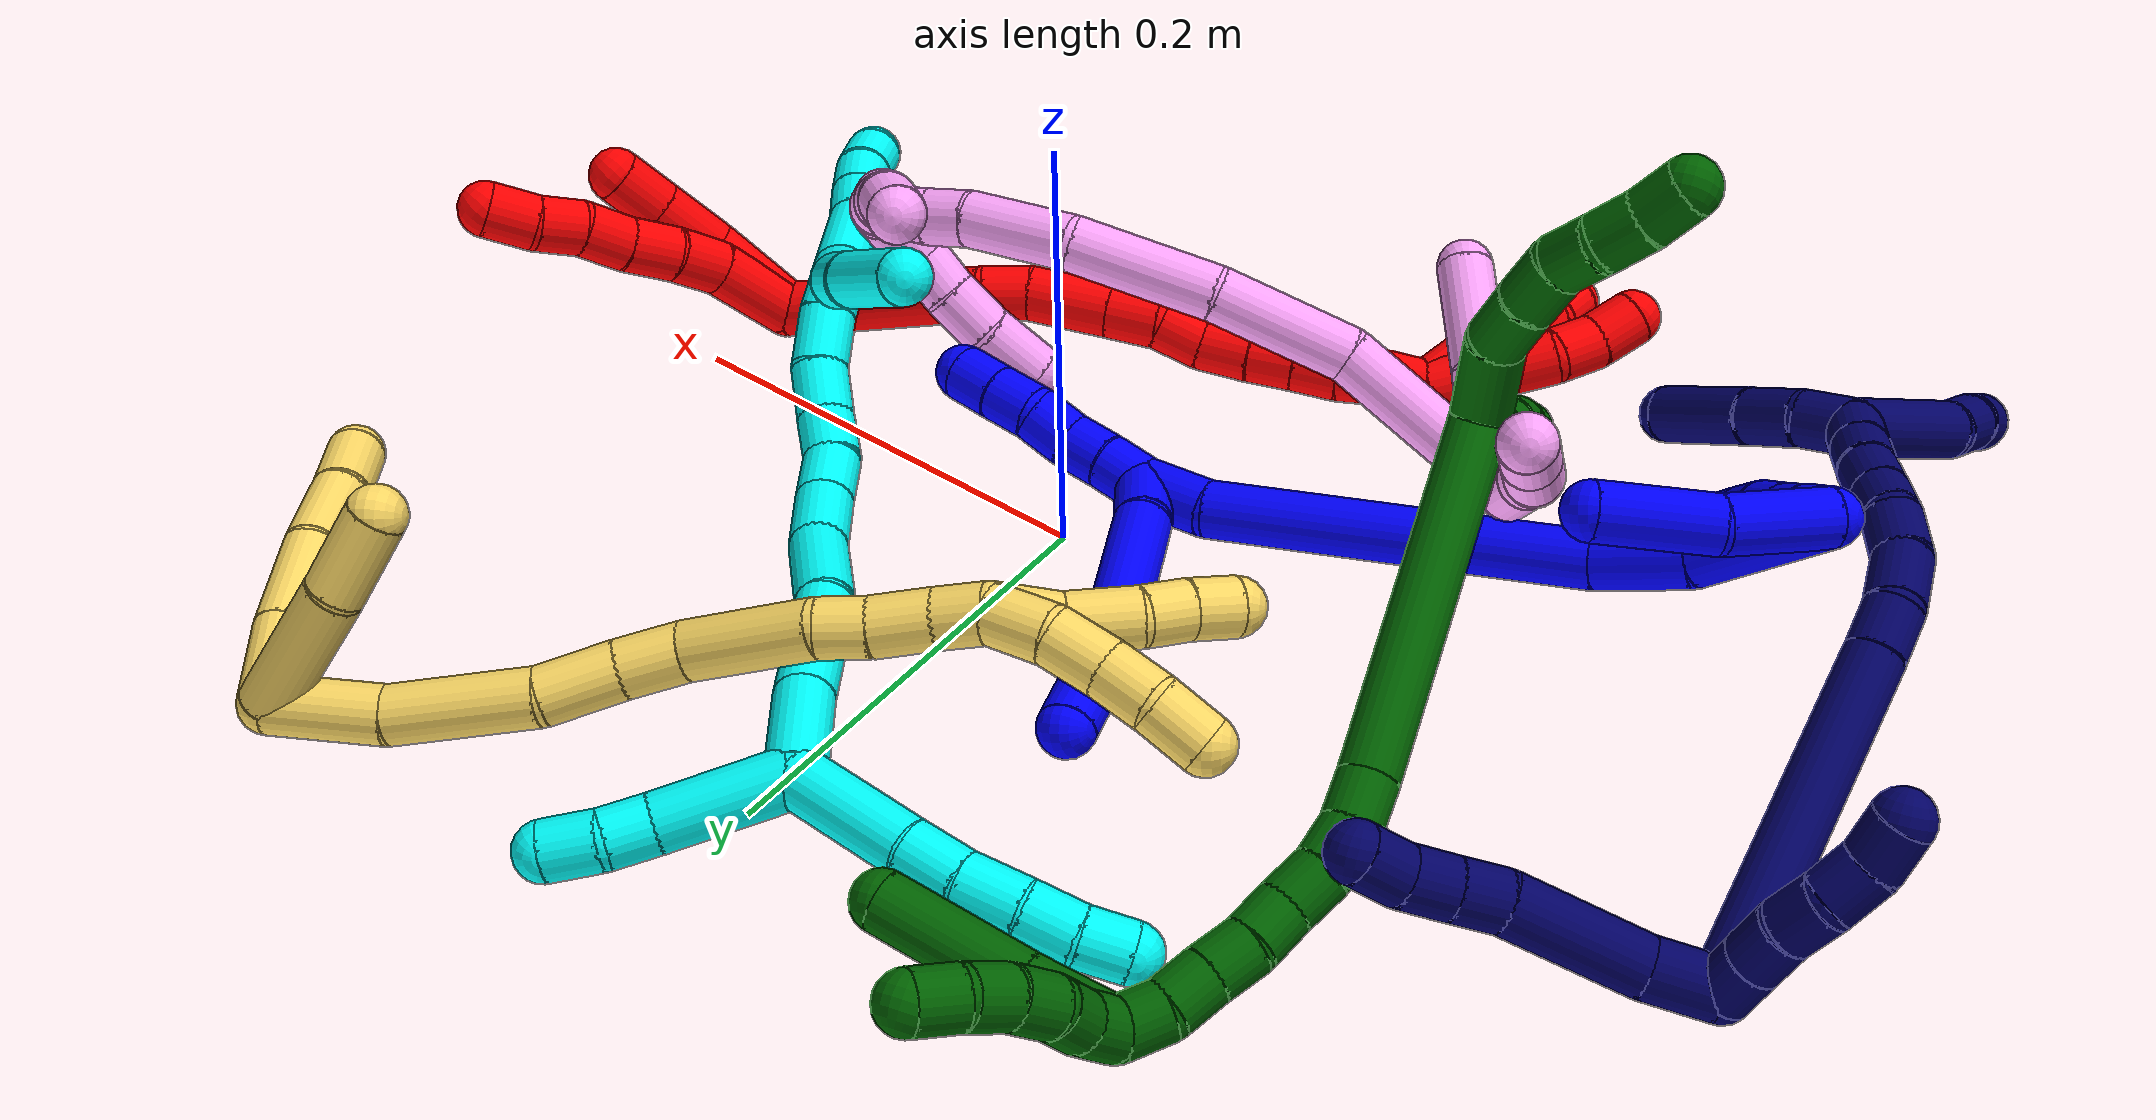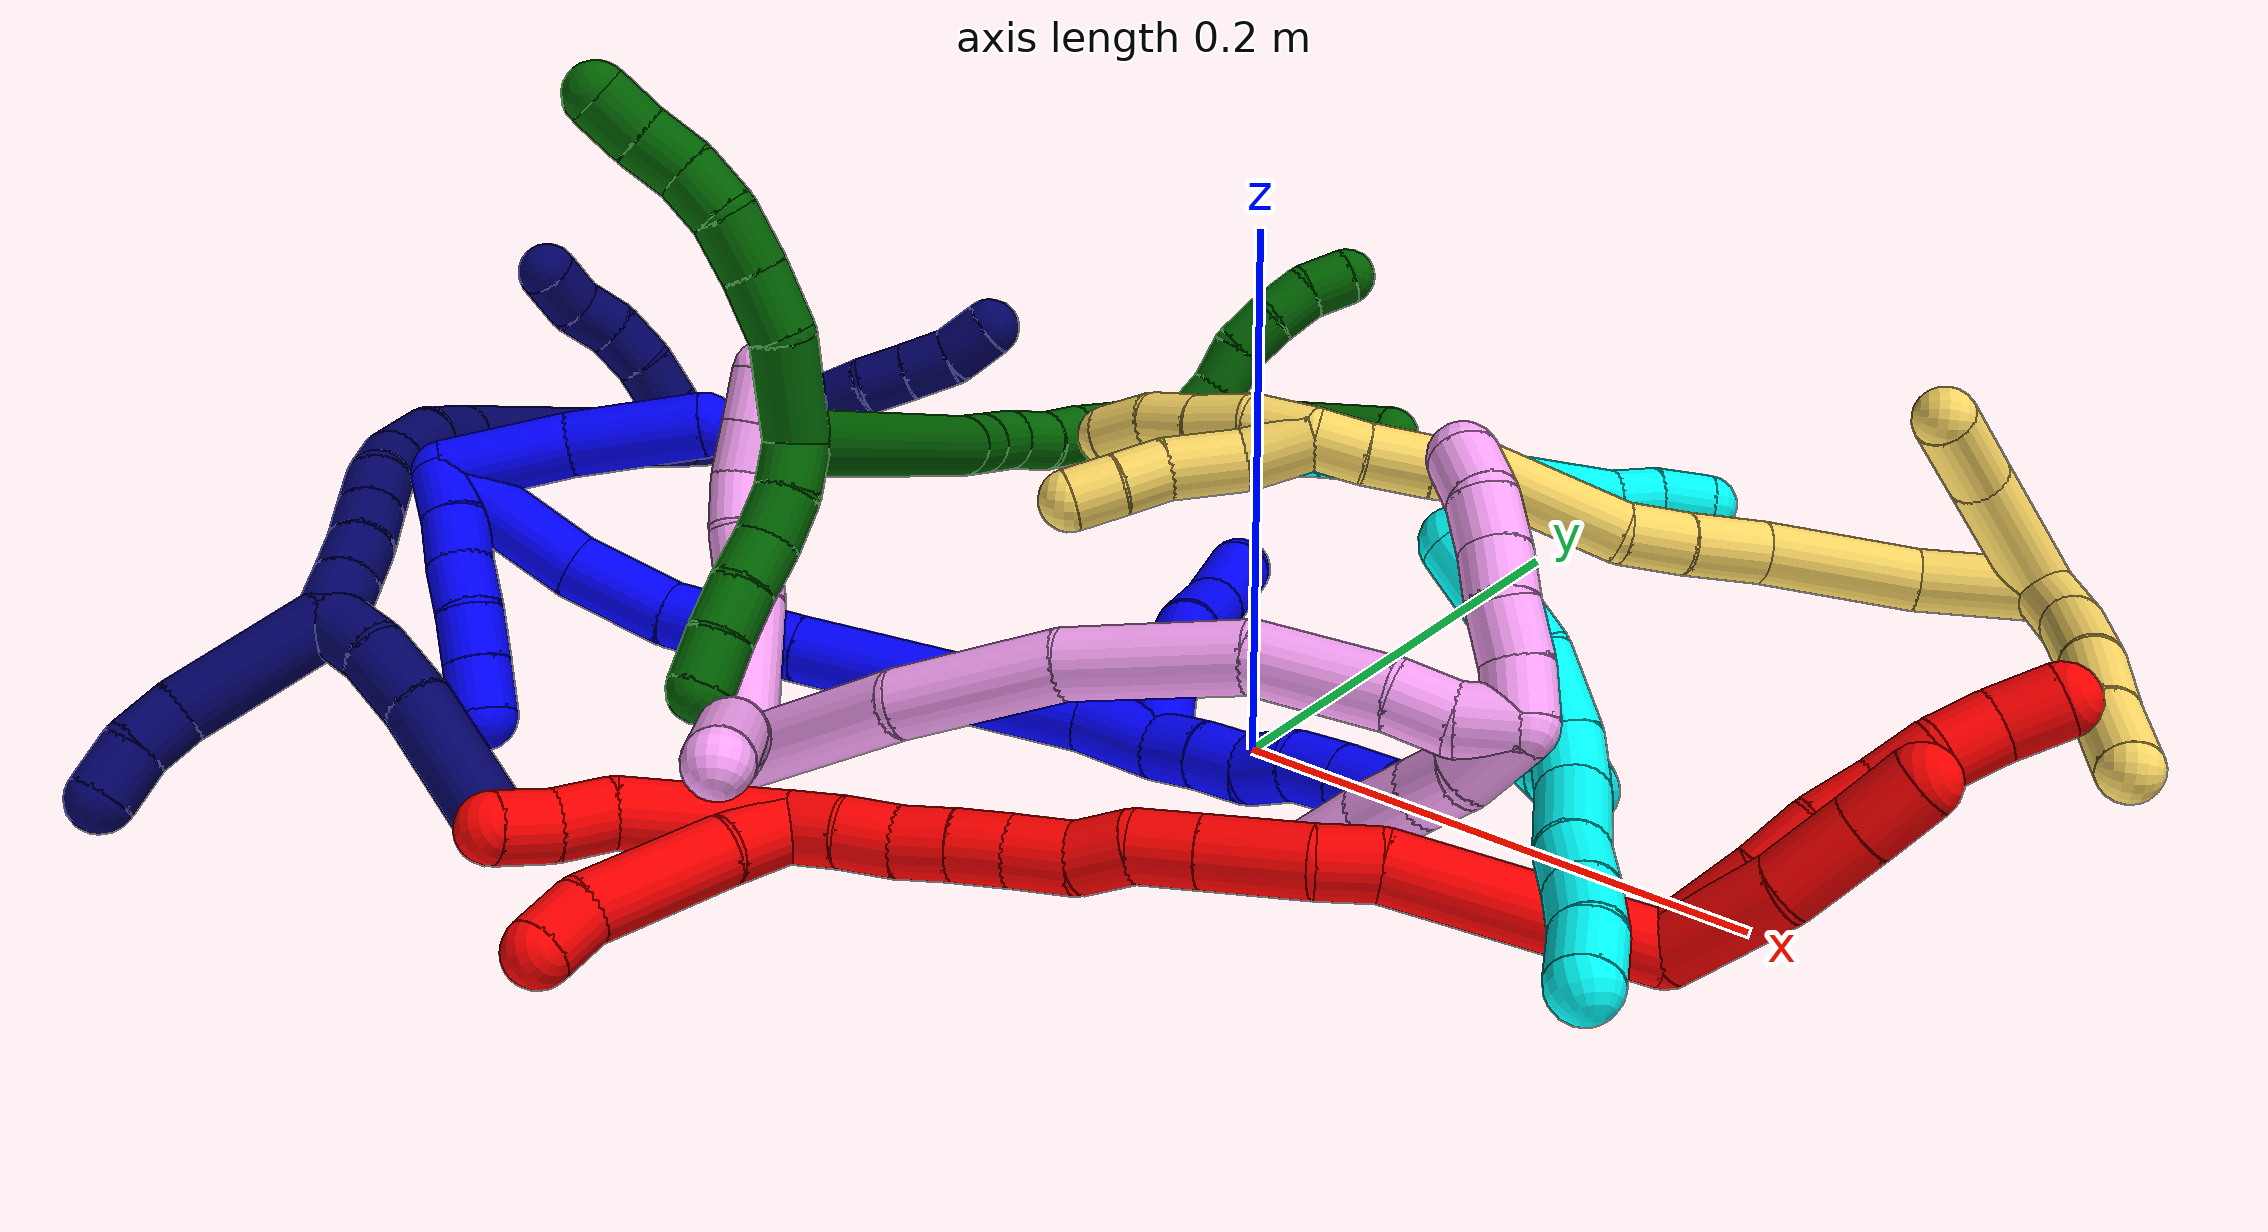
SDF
<sdf version="1.7">
 <world name="default">
  <plugin name="TubeGeneratorPlugin" filename="libtube_generator_plugin.so"/>
  <model name="photoneo_s_sensor">
   <static>1</static>
   <pose>0 0 2 1.57079 1.57079 3.14159</pose>
   <link name="link">
    <inertial><mass>0.1</mass></inertial>
    <sensor name="sensor" type="depth">
     <update_rate>30</update_rate>
     <camera>
      <horizontal_fov>1.22</horizontal_fov>
      <image><width>1920</width><height>1200</height><format>B8G8R8</format></image>
      <clip><near>0.1</near><far>4</far></clip>
      <depth_camera><output>points</output></depth_camera>
     </camera>
     <plugin name="camera_plugin" filename="libgazebo_ros_depth_camera.so">
      <baseline>0.2</baseline>
      <alwaysOn>1</alwaysOn>
      <updateRate>0.0</updateRate>
      <cameraName>camera_ir</cameraName>
      <imageTopicName>/camera/color/image_raw</imageTopicName>
      <cameraInfoTopicName>/camera/color/camera_info</cameraInfoTopicName>
      <depthImageTopicName>/camera/depth/image_raw</depthImageTopicName>
      <depthImageCameraInfoTopicName>/camera/depth/camera_info</depthImageCameraInfoTopicName>
      <pointCloudTopicName>/camera/depth/points</pointCloudTopicName>
      <frameName>fr_optical</frameName>
      <pointCloudCutoff>0.1</pointCloudCutoff>
      <pointCloudCutoffMax>2.0</pointCloudCutoffMax>
      <distortionK1>0</distortionK1>
      <distortionK2>0</distortionK2>
      <distortionK3>0</distortionK3>
      <distortionT1>0</distortionT1>
      <distortionT2>0</distortionT2>
      <CxPrime>0</CxPrime>
      <Cx>0</Cx>
      <Cy>0</Cy>
      <focalLength>0</focalLength>
      <hackBaseline>0</hackBaseline>
     </plugin>
    </sensor>
   </link>
  </model>
  <gravity>0 0 -9.8</gravity>
  <magnetic_field>6e-06 2.3e-05 -4.2e-05</magnetic_field>
  <atmosphere type="adiabatic"/>
  <physics name="default_physics" default="0" type="ode">
   <max_step_size>0.003</max_step_size>
   <real_time_factor>1</real_time_factor>
   <real_time_update_rate>1000</real_time_update_rate>
   <max_contacts>10000</max_contacts>
   <ode>
    <solver>
     <type>quick</type>
     <iters>100</iters>
     <sor>1.3</sor>
     <use_dynamic_moi_rescaling>0</use_dynamic_moi_rescaling>
    </solver>
    <constraints>
     <contact_max_correcting_vel>0</contact_max_correcting_vel>
     <contact_surface_layer>0.001</contact_surface_layer>
     <cfm>0</cfm>
     <erp>0.2</erp>
    </constraints>
   </ode>
  </physics>
  <scene><ambient>0.4 0.4 0.4 1</ambient><background>0.7 0.7 0.7 1</background><shadows>0</shadows></scene>
  <audio><device>default</device></audio>
  <spherical_coordinates>
   <surface_model>EARTH_WGS84</surface_model>
   <latitude_deg>0</latitude_deg>
   <longitude_deg>0</longitude_deg>
   <elevation>0</elevation>
   <heading_deg>0</heading_deg>
  </spherical_coordinates>
  <model name="bin">
   <static>1</static>
   <link name="bottom">
    <collision name="collision-bottom">
     <pose>0 0 -0.01 0 -0 0</pose>
     <geometry><box><size>0.8 0.6 0.02</size></box></geometry>
     <surface>
      <friction><ode><mu>100</mu><mu2>100</mu2></ode></friction>
      <contact><collide_bitmask>65535</collide_bitmask></contact>
     </surface>
    </collision>
   </link>
   <link name="west_wall">
    <collision name="collision-west_wall">
     <pose>-0.41 0 0.1 0 -0 0</pose>
     <geometry><box><size>0.02 0.6 0.2</size></box></geometry>
     <surface>
      <friction><ode><mu>100</mu><mu2>100</mu2></ode></friction>
      <contact><collide_bitmask>65535</collide_bitmask></contact>
     </surface>
    </collision>
   </link>
   <link name="east_wall">
    <collision name="collision-east_wall">
     <pose>0.41 0 0.1 0 -0 0</pose>
     <geometry><box><size>0.02 0.6 0.2</size></box></geometry>
     <surface>
      <friction><ode><mu>100</mu><mu2>100</mu2></ode></friction>
      <contact><collide_bitmask>65535</collide_bitmask></contact>
     </surface>
    </collision>
   </link>
   <link name="south_wall">
    <collision name="collision-south_wall">
     <pose>0 -0.31 0.1 0 -0 0</pose>
     <geometry><box><size>0.8 0.02 0.2</size></box></geometry>
     <surface>
      <friction><ode><mu>100</mu><mu2>100</mu2></ode></friction>
      <contact><collide_bitmask>65535</collide_bitmask></contact>
     </surface>
    </collision>
   </link>
   <link name="north_wall">
    <collision name="collision-north_wall">
     <pose>0 0.31 0.1 0 -0 0</pose>
     <geometry><box><size>0.8 0.02 0.2</size></box></geometry>
     <surface>
      <friction><ode><mu>100</mu><mu2>100</mu2></ode></friction>
      <contact><collide_bitmask>65535</collide_bitmask></contact>
     </surface>
    </collision>
   </link>
  </model>
  <model name="1">
   <static>0</static>
   <link name="1">
    <collision name="collision-cylinder-e_1_2_8">
     <pose>-0.002292 0.012868 0.006302 -1.11541 -0.158599 0.099054</pose>
     <geometry><cylinder><radius>0.0125</radius><length>0.029021</length></cylinder></geometry>
     <surface>
      <friction><ode><mu>1.16</mu><mu2>1.16</mu2><slip1>0</slip1><slip2>0</slip2></ode></friction>
      <contact><ode><kp>1e+06</kp><kd>1</kd><max_vel>0</max_vel><min_depth>0.001</min_depth></ode></contact>
     </surface>
    </collision>
    <visual name="visual-cylinder-e_1_2_8">
     <pose>-0.002292 0.012868 0.006302 -1.11541 -0.158599 0.099054</pose>
     <geometry><cylinder><radius>0.0125</radius><length>0.029021</length></cylinder></geometry>
     <material><ambient>0 0 1 1</ambient></material>
    </visual>
    <collision name="collision-cylinder-e_2_8_9">
     <pose>-0.012045 0.051053 0.019164 -1.31725 -0.277919 0.21564</pose>
     <geometry><cylinder><radius>0.0125</radius><length>0.054392</length></cylinder></geometry>
     <surface>
      <friction><ode><mu>1.16</mu><mu2>1.16</mu2><slip1>0</slip1><slip2>0</slip2></ode></friction>
      <contact><ode><kp>1e+06</kp><kd>1</kd><max_vel>0</max_vel><min_depth>0.001</min_depth></ode></contact>
     </surface>
    </collision>
    <visual name="visual-cylinder-e_2_8_9">
     <pose>-0.012045 0.051053 0.019164 -1.31725 -0.277919 0.21564</pose>
     <geometry><cylinder><radius>0.0125</radius><length>0.054392</length></cylinder></geometry>
     <material><ambient>0 0 1 1</ambient></material>
    </visual>
    <collision name="collision-cylinder-e_3_9_10">
     <pose>-0.026168 0.091348 0.026881 -1.49365 -0.417395 0.387174</pose>
     <geometry><cylinder><radius>0.0125</radius><length>0.032868</length></cylinder></geometry>
     <surface>
      <friction><ode><mu>1.16</mu><mu2>1.16</mu2><slip1>0</slip1><slip2>0</slip2></ode></friction>
      <contact><ode><kp>1e+06</kp><kd>1</kd><max_vel>0</max_vel><min_depth>0.001</min_depth></ode></contact>
     </surface>
    </collision>
    <visual name="visual-cylinder-e_3_9_10">
     <pose>-0.026168 0.091348 0.026881 -1.49365 -0.417395 0.387174</pose>
     <geometry><cylinder><radius>0.0125</radius><length>0.032868</length></cylinder></geometry>
     <material><ambient>0 0 1 1</ambient></material>
    </visual>
    <collision name="collision-cylinder-e_4_10_6">
     <pose>-0.036175 0.122742 0.029933 -1.45594 -0.199719 0.178125</pose>
     <geometry><cylinder><radius>0.0125</radius><length>0.033718</length></cylinder></geometry>
     <surface>
      <friction><ode><mu>1.16</mu><mu2>1.16</mu2><slip1>0</slip1><slip2>0</slip2></ode></friction>
      <contact><ode><kp>1e+06</kp><kd>1</kd><max_vel>0</max_vel><min_depth>0.001</min_depth></ode></contact>
     </surface>
    </collision>
    <visual name="visual-cylinder-e_4_10_6">
     <pose>-0.036175 0.122742 0.029933 -1.45594 -0.199719 0.178125</pose>
     <geometry><cylinder><radius>0.0125</radius><length>0.033718</length></cylinder></geometry>
     <material><ambient>0 0 1 1</ambient></material>
    </visual>
    <collision name="collision-cylinder-e_1_2_11">
     <pose>0.004924 -0.00113 -0.00863 3.01143 0.514811 2.65618</pose>
     <geometry><cylinder><radius>0.0125</radius><length>0.02</length></cylinder></geometry>
     <surface>
      <friction><ode><mu>1.16</mu><mu2>1.16</mu2><slip1>0</slip1><slip2>0</slip2></ode></friction>
      <contact><ode><kp>1e+06</kp><kd>1</kd><max_vel>0</max_vel><min_depth>0.001</min_depth></ode></contact>
     </surface>
    </collision>
    <visual name="visual-cylinder-e_1_2_11">
     <pose>0.004924 -0.00113 -0.00863 3.01143 0.514811 2.65618</pose>
     <geometry><cylinder><radius>0.0125</radius><length>0.02</length></cylinder></geometry>
     <material><ambient>0 0 1 1</ambient></material>
    </visual>
    <collision name="collision-cylinder-e_2_11_12">
     <pose>0.014052 -0.003686 -0.026221 2.98372 0.43394 2.45256</pose>
     <geometry><cylinder><radius>0.0125</radius><length>0.02</length></cylinder></geometry>
     <surface>
      <friction><ode><mu>1.16</mu><mu2>1.16</mu2><slip1>0</slip1><slip2>0</slip2></ode></friction>
      <contact><ode><kp>1e+06</kp><kd>1</kd><max_vel>0</max_vel><min_depth>0.001</min_depth></ode></contact>
     </surface>
    </collision>
    <visual name="visual-cylinder-e_2_11_12">
     <pose>0.014052 -0.003686 -0.026221 2.98372 0.43394 2.45256</pose>
     <geometry><cylinder><radius>0.0125</radius><length>0.02</length></cylinder></geometry>
     <material><ambient>0 0 1 1</ambient></material>
    </visual>
    <collision name="collision-cylinder-e_3_12_13">
     <pose>0.024926 -0.004892 -0.042629 -3.11199 0.73015 -3.06417</pose>
     <geometry><cylinder><radius>0.0125</radius><length>0.02</length></cylinder></geometry>
     <surface>
      <friction><ode><mu>1.16</mu><mu2>1.16</mu2><slip1>0</slip1><slip2>0</slip2></ode></friction>
      <contact><ode><kp>1e+06</kp><kd>1</kd><max_vel>0</max_vel><min_depth>0.001</min_depth></ode></contact>
     </surface>
    </collision>
    <visual name="visual-cylinder-e_3_12_13">
     <pose>0.024926 -0.004892 -0.042629 -3.11199 0.73015 -3.06417</pose>
     <geometry><cylinder><radius>0.0125</radius><length>0.02</length></cylinder></geometry>
     <material><ambient>0 0 1 1</ambient></material>
    </visual>
    <collision name="collision-cylinder-e_4_13_14">
     <pose>0.035859 -0.005883 -0.05904 3.0072 0.44043 2.55751</pose>
     <geometry><cylinder><radius>0.0125</radius><length>0.02</length></cylinder></geometry>
     <surface>
      <friction><ode><mu>1.16</mu><mu2>1.16</mu2><slip1>0</slip1><slip2>0</slip2></ode></friction>
      <contact><ode><kp>1e+06</kp><kd>1</kd><max_vel>0</max_vel><min_depth>0.001</min_depth></ode></contact>
     </surface>
    </collision>
    <visual name="visual-cylinder-e_4_13_14">
     <pose>0.035859 -0.005883 -0.05904 3.0072 0.44043 2.55751</pose>
     <geometry><cylinder><radius>0.0125</radius><length>0.02</length></cylinder></geometry>
     <material><ambient>0 0 1 1</ambient></material>
    </visual>
    <collision name="collision-cylinder-e_5_14_5">
     <pose>0.044204 -0.008804 -0.076972 2.95333 0.420426 2.30843</pose>
     <geometry><cylinder><radius>0.0125</radius><length>0.02</length></cylinder></geometry>
     <surface>
      <friction><ode><mu>1.16</mu><mu2>1.16</mu2><slip1>0</slip1><slip2>0</slip2></ode></friction>
      <contact><ode><kp>1e+06</kp><kd>1</kd><max_vel>0</max_vel><min_depth>0.001</min_depth></ode></contact>
     </surface>
    </collision>
    <visual name="visual-cylinder-e_5_14_5">
     <pose>0.044204 -0.008804 -0.076972 2.95333 0.420426 2.30843</pose>
     <geometry><cylinder><radius>0.0125</radius><length>0.02</length></cylinder></geometry>
     <material><ambient>0 0 1 1</ambient></material>
    </visual>
    <collision name="collision-cylinder-e_1_2_15">
     <pose>-0.00473 0.001222 0.015221 -0.080108 -0.300354 0.012128</pose>
     <geometry><cylinder><radius>0.0125</radius><length>0.031972</length></cylinder></geometry>
     <surface>
      <friction><ode><mu>1.16</mu><mu2>1.16</mu2><slip1>0</slip1><slip2>0</slip2></ode></friction>
      <contact><ode><kp>1e+06</kp><kd>1</kd><max_vel>0</max_vel><min_depth>0.001</min_depth></ode></contact>
     </surface>
    </collision>
    <visual name="visual-cylinder-e_1_2_15">
     <pose>-0.00473 0.001222 0.015221 -0.080108 -0.300354 0.012128</pose>
     <geometry><cylinder><radius>0.0125</radius><length>0.031972</length></cylinder></geometry>
     <material><ambient>0 0 1 1</ambient></material>
    </visual>
    <collision name="collision-cylinder-e_2_15_16">
     <pose>-0.021224 -0.007622 0.084427 0.184345 -0.211053 -0.019581</pose>
     <geometry><cylinder><radius>0.0125</radius><length>0.112322</length></cylinder></geometry>
     <surface>
      <friction><ode><mu>1.16</mu><mu2>1.16</mu2><slip1>0</slip1><slip2>0</slip2></ode></friction>
      <contact><ode><kp>1e+06</kp><kd>1</kd><max_vel>0</max_vel><min_depth>0.001</min_depth></ode></contact>
     </surface>
    </collision>
    <visual name="visual-cylinder-e_2_15_16">
     <pose>-0.021224 -0.007622 0.084427 0.184345 -0.211053 -0.019581</pose>
     <geometry><cylinder><radius>0.0125</radius><length>0.112322</length></cylinder></geometry>
     <material><ambient>0 0 1 1</ambient></material>
    </visual>
    <collision name="collision-cylinder-e_3_16_17">
     <pose>-0.038231 -0.021933 0.164318 0.162396 -0.197065 -0.016088</pose>
     <geometry><cylinder><radius>0.0125</radius><length>0.053539</length></cylinder></geometry>
     <surface>
      <friction><ode><mu>1.16</mu><mu2>1.16</mu2><slip1>0</slip1><slip2>0</slip2></ode></friction>
      <contact><ode><kp>1e+06</kp><kd>1</kd><max_vel>0</max_vel><min_depth>0.001</min_depth></ode></contact>
     </surface>
    </collision>
    <visual name="visual-cylinder-e_3_16_17">
     <pose>-0.038231 -0.021933 0.164318 0.162396 -0.197065 -0.016088</pose>
     <geometry><cylinder><radius>0.0125</radius><length>0.053539</length></cylinder></geometry>
     <material><ambient>0 0 1 1</ambient></material>
    </visual>
    <collision name="collision-cylinder-e_4_17_18">
     <pose>-0.043397 -0.027976 0.210898 0.086789 0.003646 0.000158</pose>
     <geometry><cylinder><radius>0.0125</radius><length>0.041503</length></cylinder></geometry>
     <surface>
      <friction><ode><mu>1.16</mu><mu2>1.16</mu2><slip1>0</slip1><slip2>0</slip2></ode></friction>
      <contact><ode><kp>1e+06</kp><kd>1</kd><max_vel>0</max_vel><min_depth>0.001</min_depth></ode></contact>
     </surface>
    </collision>
    <visual name="visual-cylinder-e_4_17_18">
     <pose>-0.043397 -0.027976 0.210898 0.086789 0.003646 0.000158</pose>
     <geometry><cylinder><radius>0.0125</radius><length>0.041503</length></cylinder></geometry>
     <material><ambient>0 0 1 1</ambient></material>
    </visual>
    <collision name="collision-cylinder-e_5_18_1">
     <pose>-0.035113 -0.033093 0.260582 0.113903 0.274032 0.015722</pose>
     <geometry><cylinder><radius>0.0125</radius><length>0.060663</length></cylinder></geometry>
     <surface>
      <friction><ode><mu>1.16</mu><mu2>1.16</mu2><slip1>0</slip1><slip2>0</slip2></ode></friction>
      <contact><ode><kp>1e+06</kp><kd>1</kd><max_vel>0</max_vel><min_depth>0.001</min_depth></ode></contact>
     </surface>
    </collision>
    <visual name="visual-cylinder-e_5_18_1">
     <pose>-0.035113 -0.033093 0.260582 0.113903 0.274032 0.015722</pose>
     <geometry><cylinder><radius>0.0125</radius><length>0.060663</length></cylinder></geometry>
     <material><ambient>0 0 1 1</ambient></material>
    </visual>
    <collision name="collision-cylinder-e_1_1_19">
     <pose>-0.029327 -0.042523 0.282056 2.46018 -0.244616 -0.667493</pose>
     <geometry><cylinder><radius>0.0125</radius><length>0.02</length></cylinder></geometry>
     <surface>
      <friction><ode><mu>1.16</mu><mu2>1.16</mu2><slip1>0</slip1><slip2>0</slip2></ode></friction>
      <contact><ode><kp>1e+06</kp><kd>1</kd><max_vel>0</max_vel><min_depth>0.001</min_depth></ode></contact>
     </surface>
    </collision>
    <visual name="visual-cylinder-e_1_1_19">
     <pose>-0.029327 -0.042523 0.282056 2.46018 -0.244616 -0.667493</pose>
     <geometry><cylinder><radius>0.0125</radius><length>0.02</length></cylinder></geometry>
     <material><ambient>0 0 1 1</ambient></material>
    </visual>
    <collision name="collision-cylinder-e_2_19_20">
     <pose>-0.034815 -0.055272 0.267699 2.36996 -0.311735 -0.738298</pose>
     <geometry><cylinder><radius>0.0125</radius><length>0.02</length></cylinder></geometry>
     <surface>
      <friction><ode><mu>1.16</mu><mu2>1.16</mu2><slip1>0</slip1><slip2>0</slip2></ode></friction>
      <contact><ode><kp>1e+06</kp><kd>1</kd><max_vel>0</max_vel><min_depth>0.001</min_depth></ode></contact>
     </surface>
    </collision>
    <visual name="visual-cylinder-e_2_19_20">
     <pose>-0.034815 -0.055272 0.267699 2.36996 -0.311735 -0.738298</pose>
     <geometry><cylinder><radius>0.0125</radius><length>0.02</length></cylinder></geometry>
     <material><ambient>0 0 1 1</ambient></material>
    </visual>
    <collision name="collision-cylinder-e_3_20_21">
     <pose>-0.040329 -0.06817 0.253473 2.43964 -0.247184 -0.654196</pose>
     <geometry><cylinder><radius>0.0125</radius><length>0.02</length></cylinder></geometry>
     <surface>
      <friction><ode><mu>1.16</mu><mu2>1.16</mu2><slip1>0</slip1><slip2>0</slip2></ode></friction>
      <contact><ode><kp>1e+06</kp><kd>1</kd><max_vel>0</max_vel><min_depth>0.001</min_depth></ode></contact>
     </surface>
    </collision>
    <visual name="visual-cylinder-e_3_20_21">
     <pose>-0.040329 -0.06817 0.253473 2.43964 -0.247184 -0.654196</pose>
     <geometry><cylinder><radius>0.0125</radius><length>0.02</length></cylinder></geometry>
     <material><ambient>0 0 1 1</ambient></material>
    </visual>
    <collision name="collision-cylinder-e_4_21_22">
     <pose>-0.046908 -0.080458 0.239243 2.41824 -0.425919 -1.03852</pose>
     <geometry><cylinder><radius>0.0125</radius><length>0.02</length></cylinder></geometry>
     <surface>
      <friction><ode><mu>1.16</mu><mu2>1.16</mu2><slip1>0</slip1><slip2>0</slip2></ode></friction>
      <contact><ode><kp>1e+06</kp><kd>1</kd><max_vel>0</max_vel><min_depth>0.001</min_depth></ode></contact>
     </surface>
    </collision>
    <visual name="visual-cylinder-e_4_21_22">
     <pose>-0.046908 -0.080458 0.239243 2.41824 -0.425919 -1.03852</pose>
     <geometry><cylinder><radius>0.0125</radius><length>0.02</length></cylinder></geometry>
     <material><ambient>0 0 1 1</ambient></material>
    </visual>
    <collision name="collision-cylinder-e_5_22_4">
     <pose>-0.055336 -0.092545 0.225722 2.40596 -0.44415 -1.06005</pose>
     <geometry><cylinder><radius>0.0125</radius><length>0.02</length></cylinder></geometry>
     <surface>
      <friction><ode><mu>1.16</mu><mu2>1.16</mu2><slip1>0</slip1><slip2>0</slip2></ode></friction>
      <contact><ode><kp>1e+06</kp><kd>1</kd><max_vel>0</max_vel><min_depth>0.001</min_depth></ode></contact>
     </surface>
    </collision>
    <visual name="visual-cylinder-e_5_22_4">
     <pose>-0.055336 -0.092545 0.225722 2.40596 -0.44415 -1.06005</pose>
     <geometry><cylinder><radius>0.0125</radius><length>0.02</length></cylinder></geometry>
     <material><ambient>0 0 1 1</ambient></material>
    </visual>
    <collision name="collision-cylinder-e_1_1_23">
     <pose>-0.020726 -0.019751 0.273278 -2.34565 0.259035 -0.600874</pose>
     <geometry><cylinder><radius>0.0125</radius><length>0.048246</length></cylinder></geometry>
     <surface>
      <friction><ode><mu>1.16</mu><mu2>1.16</mu2><slip1>0</slip1><slip2>0</slip2></ode></friction>
      <contact><ode><kp>1e+06</kp><kd>1</kd><max_vel>0</max_vel><min_depth>0.001</min_depth></ode></contact>
     </surface>
    </collision>
    <visual name="visual-cylinder-e_1_1_23">
     <pose>-0.020726 -0.019751 0.273278 -2.34565 0.259035 -0.600874</pose>
     <geometry><cylinder><radius>0.0125</radius><length>0.048246</length></cylinder></geometry>
     <material><ambient>0 0 1 1</ambient></material>
    </visual>
    <collision name="collision-cylinder-e_2_23_3">
     <pose>-0.005592 0.010074 0.236564 -2.56857 0.353361 -1.08966</pose>
     <geometry><cylinder><radius>0.0125</radius><length>0.051754</length></cylinder></geometry>
     <surface>
      <friction><ode><mu>1.16</mu><mu2>1.16</mu2><slip1>0</slip1><slip2>0</slip2></ode></friction>
      <contact><ode><kp>1e+06</kp><kd>1</kd><max_vel>0</max_vel><min_depth>0.001</min_depth></ode></contact>
     </surface>
    </collision>
    <visual name="visual-cylinder-e_2_23_3">
     <pose>-0.005592 0.010074 0.236564 -2.56857 0.353361 -1.08966</pose>
     <geometry><cylinder><radius>0.0125</radius><length>0.051754</length></cylinder></geometry>
     <material><ambient>0 0 1 1</ambient></material>
    </visual>
    <collision name="collision-sphere-3">
     <pose>0.003363 0.023237 0.216164 0 -0 0</pose>
     <geometry><sphere><radius>0.0125</radius></sphere></geometry>
     <surface>
      <friction><ode><mu>1.16</mu><mu2>1.16</mu2><slip1>0</slip1><slip2>0</slip2></ode></friction>
      <contact><ode><kp>1e+06</kp><kd>1</kd><max_vel>0</max_vel><min_depth>0.001</min_depth></ode></contact>
     </surface>
    </collision>
    <visual name="visual-sphere-3">
     <pose>0.003363 0.023237 0.216164 0 -0 0</pose>
     <geometry><sphere><radius>0.0125</radius></sphere></geometry>
     <material><ambient>0 0 1 1</ambient></material>
    </visual>
    <collision name="collision-sphere-23">
     <pose>-0.014546 -0.003089 0.256964 0 -0 0</pose>
     <geometry><sphere><radius>0.0125</radius></sphere></geometry>
     <surface>
      <friction><ode><mu>1.16</mu><mu2>1.16</mu2><slip1>0</slip1><slip2>0</slip2></ode></friction>
      <contact><ode><kp>1e+06</kp><kd>1</kd><max_vel>0</max_vel><min_depth>0.001</min_depth></ode></contact>
     </surface>
    </collision>
    <visual name="visual-sphere-23">
     <pose>-0.014546 -0.003089 0.256964 0 -0 0</pose>
     <geometry><sphere><radius>0.0125</radius></sphere></geometry>
     <material><ambient>0 0 1 1</ambient></material>
    </visual>
    <collision name="collision-sphere-4">
     <pose>-0.059633 -0.098605 0.219027 0 -0 0</pose>
     <geometry><sphere><radius>0.0125</radius></sphere></geometry>
     <surface>
      <friction><ode><mu>1.16</mu><mu2>1.16</mu2><slip1>0</slip1><slip2>0</slip2></ode></friction>
      <contact><ode><kp>1e+06</kp><kd>1</kd><max_vel>0</max_vel><min_depth>0.001</min_depth></ode></contact>
     </surface>
    </collision>
    <visual name="visual-sphere-4">
     <pose>-0.059633 -0.098605 0.219027 0 -0 0</pose>
     <geometry><sphere><radius>0.0125</radius></sphere></geometry>
     <material><ambient>0 0 1 1</ambient></material>
    </visual>
    <collision name="collision-sphere-22">
     <pose>-0.051039 -0.086486 0.232416 0 -0 0</pose>
     <geometry><sphere><radius>0.0125</radius></sphere></geometry>
     <surface>
      <friction><ode><mu>1.16</mu><mu2>1.16</mu2><slip1>0</slip1><slip2>0</slip2></ode></friction>
      <contact><ode><kp>1e+06</kp><kd>1</kd><max_vel>0</max_vel><min_depth>0.001</min_depth></ode></contact>
     </surface>
    </collision>
    <visual name="visual-sphere-22">
     <pose>-0.051039 -0.086486 0.232416 0 -0 0</pose>
     <geometry><sphere><radius>0.0125</radius></sphere></geometry>
     <material><ambient>0 0 1 1</ambient></material>
    </visual>
    <collision name="collision-sphere-21">
     <pose>-0.042776 -0.074431 0.246069 0 -0 0</pose>
     <geometry><sphere><radius>0.0125</radius></sphere></geometry>
     <surface>
      <friction><ode><mu>1.16</mu><mu2>1.16</mu2><slip1>0</slip1><slip2>0</slip2></ode></friction>
      <contact><ode><kp>1e+06</kp><kd>1</kd><max_vel>0</max_vel><min_depth>0.001</min_depth></ode></contact>
     </surface>
    </collision>
    <visual name="visual-sphere-21">
     <pose>-0.042776 -0.074431 0.246069 0 -0 0</pose>
     <geometry><sphere><radius>0.0125</radius></sphere></geometry>
     <material><ambient>0 0 1 1</ambient></material>
    </visual>
    <collision name="collision-sphere-20">
     <pose>-0.037883 -0.061909 0.260876 0 -0 0</pose>
     <geometry><sphere><radius>0.0125</radius></sphere></geometry>
     <surface>
      <friction><ode><mu>1.16</mu><mu2>1.16</mu2><slip1>0</slip1><slip2>0</slip2></ode></friction>
      <contact><ode><kp>1e+06</kp><kd>1</kd><max_vel>0</max_vel><min_depth>0.001</min_depth></ode></contact>
     </surface>
    </collision>
    <visual name="visual-sphere-20">
     <pose>-0.037883 -0.061909 0.260876 0 -0 0</pose>
     <geometry><sphere><radius>0.0125</radius></sphere></geometry>
     <material><ambient>0 0 1 1</ambient></material>
    </visual>
    <collision name="collision-sphere-11">
     <pose>0.009847 -0.00226 -0.01726 0 -0 0</pose>
     <geometry><sphere><radius>0.0125</radius></sphere></geometry>
     <surface>
      <friction><ode><mu>1.16</mu><mu2>1.16</mu2><slip1>0</slip1><slip2>0</slip2></ode></friction>
      <contact><ode><kp>1e+06</kp><kd>1</kd><max_vel>0</max_vel><min_depth>0.001</min_depth></ode></contact>
     </surface>
    </collision>
    <visual name="visual-sphere-11">
     <pose>0.009847 -0.00226 -0.01726 0 -0 0</pose>
     <geometry><sphere><radius>0.0125</radius></sphere></geometry>
     <material><ambient>0 0 1 1</ambient></material>
    </visual>
    <collision name="collision-sphere-6">
     <pose>-0.03952 0.139157 0.031827 0 -0 0</pose>
     <geometry><sphere><radius>0.0125</radius></sphere></geometry>
     <surface>
      <friction><ode><mu>1.16</mu><mu2>1.16</mu2><slip1>0</slip1><slip2>0</slip2></ode></friction>
      <contact><ode><kp>1e+06</kp><kd>1</kd><max_vel>0</max_vel><min_depth>0.001</min_depth></ode></contact>
     </surface>
    </collision>
    <visual name="visual-sphere-6">
     <pose>-0.03952 0.139157 0.031827 0 -0 0</pose>
     <geometry><sphere><radius>0.0125</radius></sphere></geometry>
     <material><ambient>0 0 1 1</ambient></material>
    </visual>
    <collision name="collision-sphere-10">
     <pose>-0.03283 0.106327 0.028039 0 -0 0</pose>
     <geometry><sphere><radius>0.0125</radius></sphere></geometry>
     <surface>
      <friction><ode><mu>1.16</mu><mu2>1.16</mu2><slip1>0</slip1><slip2>0</slip2></ode></friction>
      <contact><ode><kp>1e+06</kp><kd>1</kd><max_vel>0</max_vel><min_depth>0.001</min_depth></ode></contact>
     </surface>
    </collision>
    <visual name="visual-sphere-10">
     <pose>-0.03283 0.106327 0.028039 0 -0 0</pose>
     <geometry><sphere><radius>0.0125</radius></sphere></geometry>
     <material><ambient>0 0 1 1</ambient></material>
    </visual>
    <collision name="collision-sphere-9">
     <pose>-0.019506 0.07637 0.025724 0 -0 0</pose>
     <geometry><sphere><radius>0.0125</radius></sphere></geometry>
     <surface>
      <friction><ode><mu>1.16</mu><mu2>1.16</mu2><slip1>0</slip1><slip2>0</slip2></ode></friction>
      <contact><ode><kp>1e+06</kp><kd>1</kd><max_vel>0</max_vel><min_depth>0.001</min_depth></ode></contact>
     </surface>
    </collision>
    <visual name="visual-sphere-9">
     <pose>-0.019506 0.07637 0.025724 0 -0 0</pose>
     <geometry><sphere><radius>0.0125</radius></sphere></geometry>
     <material><ambient>0 0 1 1</ambient></material>
    </visual>
    <collision name="collision-sphere-2">
     <geometry><sphere><radius>0.0125</radius></sphere></geometry>
     <surface>
      <friction><ode><mu>1.16</mu><mu2>1.16</mu2><slip1>0</slip1><slip2>0</slip2></ode></friction>
      <contact><ode><kp>1e+06</kp><kd>1</kd><max_vel>0</max_vel><min_depth>0.001</min_depth></ode></contact>
     </surface>
    </collision>
    <visual name="visual-sphere-2">
     <geometry><sphere><radius>0.0125</radius></sphere></geometry>
     <material><ambient>0 0 1 1</ambient></material>
    </visual>
    <collision name="collision-sphere-19">
     <pose>-0.031748 -0.048635 0.274521 0 -0 0</pose>
     <geometry><sphere><radius>0.0125</radius></sphere></geometry>
     <surface>
      <friction><ode><mu>1.16</mu><mu2>1.16</mu2><slip1>0</slip1><slip2>0</slip2></ode></friction>
      <contact><ode><kp>1e+06</kp><kd>1</kd><max_vel>0</max_vel><min_depth>0.001</min_depth></ode></contact>
     </surface>
    </collision>
    <visual name="visual-sphere-19">
     <pose>-0.031748 -0.048635 0.274521 0 -0 0</pose>
     <geometry><sphere><radius>0.0125</radius></sphere></geometry>
     <material><ambient>0 0 1 1</ambient></material>
    </visual>
    <collision name="collision-sphere-8">
     <pose>-0.004583 0.025736 0.012604 0 -0 0</pose>
     <geometry><sphere><radius>0.0125</radius></sphere></geometry>
     <surface>
      <friction><ode><mu>1.16</mu><mu2>1.16</mu2><slip1>0</slip1><slip2>0</slip2></ode></friction>
      <contact><ode><kp>1e+06</kp><kd>1</kd><max_vel>0</max_vel><min_depth>0.001</min_depth></ode></contact>
     </surface>
    </collision>
    <visual name="visual-sphere-8">
     <pose>-0.004583 0.025736 0.012604 0 -0 0</pose>
     <geometry><sphere><radius>0.0125</radius></sphere></geometry>
     <material><ambient>0 0 1 1</ambient></material>
    </visual>
    <collision name="collision-sphere-12">
     <pose>0.018256 -0.005112 -0.035181 0 -0 0</pose>
     <geometry><sphere><radius>0.0125</radius></sphere></geometry>
     <surface>
      <friction><ode><mu>1.16</mu><mu2>1.16</mu2><slip1>0</slip1><slip2>0</slip2></ode></friction>
      <contact><ode><kp>1e+06</kp><kd>1</kd><max_vel>0</max_vel><min_depth>0.001</min_depth></ode></contact>
     </surface>
    </collision>
    <visual name="visual-sphere-12">
     <pose>0.018256 -0.005112 -0.035181 0 -0 0</pose>
     <geometry><sphere><radius>0.0125</radius></sphere></geometry>
     <material><ambient>0 0 1 1</ambient></material>
    </visual>
    <collision name="collision-sphere-13">
     <pose>0.031596 -0.004671 -0.050076 0 -0 0</pose>
     <geometry><sphere><radius>0.0125</radius></sphere></geometry>
     <surface>
      <friction><ode><mu>1.16</mu><mu2>1.16</mu2><slip1>0</slip1><slip2>0</slip2></ode></friction>
      <contact><ode><kp>1e+06</kp><kd>1</kd><max_vel>0</max_vel><min_depth>0.001</min_depth></ode></contact>
     </surface>
    </collision>
    <visual name="visual-sphere-13">
     <pose>0.031596 -0.004671 -0.050076 0 -0 0</pose>
     <geometry><sphere><radius>0.0125</radius></sphere></geometry>
     <material><ambient>0 0 1 1</ambient></material>
    </visual>
    <collision name="collision-sphere-14">
     <pose>0.040123 -0.007095 -0.068004 0 -0 0</pose>
     <geometry><sphere><radius>0.0125</radius></sphere></geometry>
     <surface>
      <friction><ode><mu>1.16</mu><mu2>1.16</mu2><slip1>0</slip1><slip2>0</slip2></ode></friction>
      <contact><ode><kp>1e+06</kp><kd>1</kd><max_vel>0</max_vel><min_depth>0.001</min_depth></ode></contact>
     </surface>
    </collision>
    <visual name="visual-sphere-14">
     <pose>0.040123 -0.007095 -0.068004 0 -0 0</pose>
     <geometry><sphere><radius>0.0125</radius></sphere></geometry>
     <material><ambient>0 0 1 1</ambient></material>
    </visual>
    <collision name="collision-sphere-5">
     <pose>0.048286 -0.010512 -0.08594 0 -0 0</pose>
     <geometry><sphere><radius>0.0125</radius></sphere></geometry>
     <surface>
      <friction><ode><mu>1.16</mu><mu2>1.16</mu2><slip1>0</slip1><slip2>0</slip2></ode></friction>
      <contact><ode><kp>1e+06</kp><kd>1</kd><max_vel>0</max_vel><min_depth>0.001</min_depth></ode></contact>
     </surface>
    </collision>
    <visual name="visual-sphere-5">
     <pose>0.048286 -0.010512 -0.08594 0 -0 0</pose>
     <geometry><sphere><radius>0.0125</radius></sphere></geometry>
     <material><ambient>0 0 1 1</ambient></material>
    </visual>
    <collision name="collision-sphere-15">
     <pose>-0.009459 0.002444 0.030443 0 -0 0</pose>
     <geometry><sphere><radius>0.0125</radius></sphere></geometry>
     <surface>
      <friction><ode><mu>1.16</mu><mu2>1.16</mu2><slip1>0</slip1><slip2>0</slip2></ode></friction>
      <contact><ode><kp>1e+06</kp><kd>1</kd><max_vel>0</max_vel><min_depth>0.001</min_depth></ode></contact>
     </surface>
    </collision>
    <visual name="visual-sphere-15">
     <pose>-0.009459 0.002444 0.030443 0 -0 0</pose>
     <geometry><sphere><radius>0.0125</radius></sphere></geometry>
     <material><ambient>0 0 1 1</ambient></material>
    </visual>
    <collision name="collision-sphere-16">
     <pose>-0.03299 -0.017688 0.138412 0 -0 0</pose>
     <geometry><sphere><radius>0.0125</radius></sphere></geometry>
     <surface>
      <friction><ode><mu>1.16</mu><mu2>1.16</mu2><slip1>0</slip1><slip2>0</slip2></ode></friction>
      <contact><ode><kp>1e+06</kp><kd>1</kd><max_vel>0</max_vel><min_depth>0.001</min_depth></ode></contact>
     </surface>
    </collision>
    <visual name="visual-sphere-16">
     <pose>-0.03299 -0.017688 0.138412 0 -0 0</pose>
     <geometry><sphere><radius>0.0125</radius></sphere></geometry>
     <material><ambient>0 0 1 1</ambient></material>
    </visual>
    <collision name="collision-sphere-17">
     <pose>-0.043472 -0.026177 0.190224 0 -0 0</pose>
     <geometry><sphere><radius>0.0125</radius></sphere></geometry>
     <surface>
      <friction><ode><mu>1.16</mu><mu2>1.16</mu2><slip1>0</slip1><slip2>0</slip2></ode></friction>
      <contact><ode><kp>1e+06</kp><kd>1</kd><max_vel>0</max_vel><min_depth>0.001</min_depth></ode></contact>
     </surface>
    </collision>
    <visual name="visual-sphere-17">
     <pose>-0.043472 -0.026177 0.190224 0 -0 0</pose>
     <geometry><sphere><radius>0.0125</radius></sphere></geometry>
     <material><ambient>0 0 1 1</ambient></material>
    </visual>
    <collision name="collision-sphere-18">
     <pose>-0.043321 -0.029775 0.231571 0 -0 0</pose>
     <geometry><sphere><radius>0.0125</radius></sphere></geometry>
     <surface>
      <friction><ode><mu>1.16</mu><mu2>1.16</mu2><slip1>0</slip1><slip2>0</slip2></ode></friction>
      <contact><ode><kp>1e+06</kp><kd>1</kd><max_vel>0</max_vel><min_depth>0.001</min_depth></ode></contact>
     </surface>
    </collision>
    <visual name="visual-sphere-18">
     <pose>-0.043321 -0.029775 0.231571 0 -0 0</pose>
     <geometry><sphere><radius>0.0125</radius></sphere></geometry>
     <material><ambient>0 0 1 1</ambient></material>
    </visual>
    <collision name="collision-sphere-1">
     <pose>-0.026905 -0.036412 0.289592 0 -0 0</pose>
     <geometry><sphere><radius>0.0125</radius></sphere></geometry>
     <surface>
      <friction><ode><mu>1.16</mu><mu2>1.16</mu2><slip1>0</slip1><slip2>0</slip2></ode></friction>
      <contact><ode><kp>1e+06</kp><kd>1</kd><max_vel>0</max_vel><min_depth>0.001</min_depth></ode></contact>
     </surface>
    </collision>
    <visual name="visual-sphere-1">
     <pose>-0.026905 -0.036412 0.289592 0 -0 0</pose>
     <geometry><sphere><radius>0.0125</radius></sphere></geometry>
     <material><ambient>0 0 1 1</ambient></material>
    </visual>
    <inertial>
     <pose>-0.019012 -0.003423 0.123957 0 -0 0</pose>
     <mass>0.75</mass>
     <inertia>
      <ixx>0.000188</ixx>
      <ixy>0</ixy>
      <ixz>0</ixz>
      <iyy>0.000162</iyy>
      <iyz>0</iyz>
      <izz>2.2e-05</izz>
     </inertia>
    </inertial>
   </link>
   <pose>-0.015379 -0.035962 0.012486 0.516134 -1.17977 -0.341757</pose>
  </model>
  <model name="2">
   <static>0</static>
   <link name="2">
    <collision name="collision-cylinder-e_1_2_8">
     <pose>-0.001193 0.008736 0.017483 -0.4634 -0.060957 0.014386</pose>
     <geometry><cylinder><radius>0.0125</radius><length>0.039161</length></cylinder></geometry>
     <surface>
      <friction><ode><mu>1.16</mu><mu2>1.16</mu2><slip1>0</slip1><slip2>0</slip2></ode></friction>
      <contact><ode><kp>1e+06</kp><kd>1</kd><max_vel>0</max_vel><min_depth>0.001</min_depth></ode></contact>
     </surface>
    </collision>
    <visual name="visual-cylinder-e_1_2_8">
     <pose>-0.001193 0.008736 0.017483 -0.4634 -0.060957 0.014386</pose>
     <geometry><cylinder><radius>0.0125</radius><length>0.039161</length></cylinder></geometry>
     <material><ambient>1 0 0 1</ambient></material>
    </visual>
    <collision name="collision-cylinder-e_2_8_9">
     <pose>-0.0022 0.025266 0.043546 -0.737401 0.015996 -0.006181</pose>
     <geometry><cylinder><radius>0.0125</radius><length>0.023186</length></cylinder></geometry>
     <surface>
      <friction><ode><mu>1.16</mu><mu2>1.16</mu2><slip1>0</slip1><slip2>0</slip2></ode></friction>
      <contact><ode><kp>1e+06</kp><kd>1</kd><max_vel>0</max_vel><min_depth>0.001</min_depth></ode></contact>
     </surface>
    </collision>
    <visual name="visual-cylinder-e_2_8_9">
     <pose>-0.0022 0.025266 0.043546 -0.737401 0.015996 -0.006181</pose>
     <geometry><cylinder><radius>0.0125</radius><length>0.023186</length></cylinder></geometry>
     <material><ambient>1 0 0 1</ambient></material>
    </visual>
    <collision name="collision-cylinder-e_3_9_10">
     <pose>-0.000104 0.040291 0.06095 -0.686519 0.165983 -0.059443</pose>
     <geometry><cylinder><radius>0.0125</radius><length>0.023134</length></cylinder></geometry>
     <surface>
      <friction><ode><mu>1.16</mu><mu2>1.16</mu2><slip1>0</slip1><slip2>0</slip2></ode></friction>
      <contact><ode><kp>1e+06</kp><kd>1</kd><max_vel>0</max_vel><min_depth>0.001</min_depth></ode></contact>
     </surface>
    </collision>
    <visual name="visual-cylinder-e_3_9_10">
     <pose>-0.000104 0.040291 0.06095 -0.686519 0.165983 -0.059443</pose>
     <geometry><cylinder><radius>0.0125</radius><length>0.023134</length></cylinder></geometry>
     <material><ambient>1 0 0 1</ambient></material>
    </visual>
    <collision name="collision-cylinder-e_4_10_11">
     <pose>0.002427 0.053835 0.078649 -0.618291 0.056802 -0.018146</pose>
     <geometry><cylinder><radius>0.0125</radius><length>0.021818</length></cylinder></geometry>
     <surface>
      <friction><ode><mu>1.16</mu><mu2>1.16</mu2><slip1>0</slip1><slip2>0</slip2></ode></friction>
      <contact><ode><kp>1e+06</kp><kd>1</kd><max_vel>0</max_vel><min_depth>0.001</min_depth></ode></contact>
     </surface>
    </collision>
    <visual name="visual-cylinder-e_4_10_11">
     <pose>0.002427 0.053835 0.078649 -0.618291 0.056802 -0.018146</pose>
     <geometry><cylinder><radius>0.0125</radius><length>0.021818</length></cylinder></geometry>
     <material><ambient>1 0 0 1</ambient></material>
    </visual>
    <collision name="collision-cylinder-e_5_11_12">
     <pose>0.005872 0.066575 0.095067 -0.70567 0.277825 -0.10288</pose>
     <geometry><cylinder><radius>0.0125</radius><length>0.020609</length></cylinder></geometry>
     <surface>
      <friction><ode><mu>1.16</mu><mu2>1.16</mu2><slip1>0</slip1><slip2>0</slip2></ode></friction>
      <contact><ode><kp>1e+06</kp><kd>1</kd><max_vel>0</max_vel><min_depth>0.001</min_depth></ode></contact>
     </surface>
    </collision>
    <visual name="visual-cylinder-e_5_11_12">
     <pose>0.005872 0.066575 0.095067 -0.70567 0.277825 -0.10288</pose>
     <geometry><cylinder><radius>0.0125</radius><length>0.020609</length></cylinder></geometry>
     <material><ambient>1 0 0 1</ambient></material>
    </visual>
    <collision name="collision-cylinder-e_6_12_6">
     <pose>0.011433 0.077957 0.112095 -0.481487 0.250201 -0.061729</pose>
     <geometry><cylinder><radius>0.0125</radius><length>0.022092</length></cylinder></geometry>
     <surface>
      <friction><ode><mu>1.16</mu><mu2>1.16</mu2><slip1>0</slip1><slip2>0</slip2></ode></friction>
      <contact><ode><kp>1e+06</kp><kd>1</kd><max_vel>0</max_vel><min_depth>0.001</min_depth></ode></contact>
     </surface>
    </collision>
    <visual name="visual-cylinder-e_6_12_6">
     <pose>0.011433 0.077957 0.112095 -0.481487 0.250201 -0.061729</pose>
     <geometry><cylinder><radius>0.0125</radius><length>0.022092</length></cylinder></geometry>
     <material><ambient>1 0 0 1</ambient></material>
    </visual>
    <collision name="collision-cylinder-e_1_2_13">
     <pose>-0.001448 0.004624 0.021916 -0.207935 -0.064542 0.006737</pose>
     <geometry><cylinder><radius>0.0125</radius><length>0.044891</length></cylinder></geometry>
     <surface>
      <friction><ode><mu>1.16</mu><mu2>1.16</mu2><slip1>0</slip1><slip2>0</slip2></ode></friction>
      <contact><ode><kp>1e+06</kp><kd>1</kd><max_vel>0</max_vel><min_depth>0.001</min_depth></ode></contact>
     </surface>
    </collision>
    <visual name="visual-cylinder-e_1_2_13">
     <pose>-0.001448 0.004624 0.021916 -0.207935 -0.064542 0.006737</pose>
     <geometry><cylinder><radius>0.0125</radius><length>0.044891</length></cylinder></geometry>
     <material><ambient>1 0 0 1</ambient></material>
    </visual>
    <collision name="collision-cylinder-e_2_13_14">
     <pose>-0.004877 0.015261 0.058215 -0.395989 -0.126458 0.025403</pose>
     <geometry><cylinder><radius>0.0125</radius><length>0.03143</length></cylinder></geometry>
     <surface>
      <friction><ode><mu>1.16</mu><mu2>1.16</mu2><slip1>0</slip1><slip2>0</slip2></ode></friction>
      <contact><ode><kp>1e+06</kp><kd>1</kd><max_vel>0</max_vel><min_depth>0.001</min_depth></ode></contact>
     </surface>
    </collision>
    <visual name="visual-cylinder-e_2_13_14">
     <pose>-0.004877 0.015261 0.058215 -0.395989 -0.126458 0.025403</pose>
     <geometry><cylinder><radius>0.0125</radius><length>0.03143</length></cylinder></geometry>
     <material><ambient>1 0 0 1</ambient></material>
    </visual>
    <collision name="collision-cylinder-e_3_14_5">
     <pose>-0.008518 0.025929 0.083358 -0.408325 -0.1406 0.029157</pose>
     <geometry><cylinder><radius>0.0125</radius><length>0.023679</length></cylinder></geometry>
     <surface>
      <friction><ode><mu>1.16</mu><mu2>1.16</mu2><slip1>0</slip1><slip2>0</slip2></ode></friction>
      <contact><ode><kp>1e+06</kp><kd>1</kd><max_vel>0</max_vel><min_depth>0.001</min_depth></ode></contact>
     </surface>
    </collision>
    <visual name="visual-cylinder-e_3_14_5">
     <pose>-0.008518 0.025929 0.083358 -0.408325 -0.1406 0.029157</pose>
     <geometry><cylinder><radius>0.0125</radius><length>0.023679</length></cylinder></geometry>
     <material><ambient>1 0 0 1</ambient></material>
    </visual>
    <collision name="collision-cylinder-e_1_2_15">
     <pose>-0.035864 -0.004468 -0.030157 2.99449 -0.866273 -2.82556</pose>
     <geometry><cylinder><radius>0.0125</radius><length>0.09414</length></cylinder></geometry>
     <surface>
      <friction><ode><mu>1.16</mu><mu2>1.16</mu2><slip1>0</slip1><slip2>0</slip2></ode></friction>
      <contact><ode><kp>1e+06</kp><kd>1</kd><max_vel>0</max_vel><min_depth>0.001</min_depth></ode></contact>
     </surface>
    </collision>
    <visual name="visual-cylinder-e_1_2_15">
     <pose>-0.035864 -0.004468 -0.030157 2.99449 -0.866273 -2.82556</pose>
     <geometry><cylinder><radius>0.0125</radius><length>0.09414</length></cylinder></geometry>
     <material><ambient>1 0 0 1</ambient></material>
    </visual>
    <collision name="collision-cylinder-e_2_15_16">
     <pose>-0.078516 -0.012052 -0.068101 2.76103 -0.680447 -2.14496</pose>
     <geometry><cylinder><radius>0.0125</radius><length>0.021581</length></cylinder></geometry>
     <surface>
      <friction><ode><mu>1.16</mu><mu2>1.16</mu2><slip1>0</slip1><slip2>0</slip2></ode></friction>
      <contact><ode><kp>1e+06</kp><kd>1</kd><max_vel>0</max_vel><min_depth>0.001</min_depth></ode></contact>
     </surface>
    </collision>
    <visual name="visual-cylinder-e_2_15_16">
     <pose>-0.078516 -0.012052 -0.068101 2.76103 -0.680447 -2.14496</pose>
     <geometry><cylinder><radius>0.0125</radius><length>0.021581</length></cylinder></geometry>
     <material><ambient>1 0 0 1</ambient></material>
    </visual>
    <collision name="collision-cylinder-e_3_16_17">
     <pose>-0.095286 -0.016795 -0.091535 3.03796 -0.565361 -2.7882</pose>
     <geometry><cylinder><radius>0.0125</radius><length>0.037261</length></cylinder></geometry>
     <surface>
      <friction><ode><mu>1.16</mu><mu2>1.16</mu2><slip1>0</slip1><slip2>0</slip2></ode></friction>
      <contact><ode><kp>1e+06</kp><kd>1</kd><max_vel>0</max_vel><min_depth>0.001</min_depth></ode></contact>
     </surface>
    </collision>
    <visual name="visual-cylinder-e_3_16_17">
     <pose>-0.095286 -0.016795 -0.091535 3.03796 -0.565361 -2.7882</pose>
     <geometry><cylinder><radius>0.0125</radius><length>0.037261</length></cylinder></geometry>
     <material><ambient>1 0 0 1</ambient></material>
    </visual>
    <collision name="collision-cylinder-e_4_17_18">
     <pose>-0.111319 -0.019346 -0.116874 3.0466 -0.556182 -2.81162</pose>
     <geometry><cylinder><radius>0.0125</radius><length>0.022927</length></cylinder></geometry>
     <surface>
      <friction><ode><mu>1.16</mu><mu2>1.16</mu2><slip1>0</slip1><slip2>0</slip2></ode></friction>
      <contact><ode><kp>1e+06</kp><kd>1</kd><max_vel>0</max_vel><min_depth>0.001</min_depth></ode></contact>
     </surface>
    </collision>
    <visual name="visual-cylinder-e_4_17_18">
     <pose>-0.111319 -0.019346 -0.116874 3.0466 -0.556182 -2.81162</pose>
     <geometry><cylinder><radius>0.0125</radius><length>0.022927</length></cylinder></geometry>
     <material><ambient>1 0 0 1</ambient></material>
    </visual>
    <collision name="collision-cylinder-e_5_18_19">
     <pose>-0.119974 -0.022032 -0.13665 2.96861 -0.249063 -1.93</pose>
     <geometry><cylinder><radius>0.0125</radius><length>0.021127</length></cylinder></geometry>
     <surface>
      <friction><ode><mu>1.16</mu><mu2>1.16</mu2><slip1>0</slip1><slip2>0</slip2></ode></friction>
      <contact><ode><kp>1e+06</kp><kd>1</kd><max_vel>0</max_vel><min_depth>0.001</min_depth></ode></contact>
     </surface>
    </collision>
    <visual name="visual-cylinder-e_5_18_19">
     <pose>-0.119974 -0.022032 -0.13665 2.96861 -0.249063 -1.93</pose>
     <geometry><cylinder><radius>0.0125</radius><length>0.021127</length></cylinder></geometry>
     <material><ambient>1 0 0 1</ambient></material>
    </visual>
    <collision name="collision-cylinder-e_6_19_20">
     <pose>-0.12859 -0.024243 -0.156421 3.09528 -0.554962 -2.97934</pose>
     <geometry><cylinder><radius>0.0125</radius><length>0.022819</length></cylinder></geometry>
     <surface>
      <friction><ode><mu>1.16</mu><mu2>1.16</mu2><slip1>0</slip1><slip2>0</slip2></ode></friction>
      <contact><ode><kp>1e+06</kp><kd>1</kd><max_vel>0</max_vel><min_depth>0.001</min_depth></ode></contact>
     </surface>
    </collision>
    <visual name="visual-cylinder-e_6_19_20">
     <pose>-0.12859 -0.024243 -0.156421 3.09528 -0.554962 -2.97934</pose>
     <geometry><cylinder><radius>0.0125</radius><length>0.022819</length></cylinder></geometry>
     <material><ambient>1 0 0 1</ambient></material>
    </visual>
    <collision name="collision-cylinder-e_7_20_21">
     <pose>-0.140104 -0.025591 -0.174474 3.03444 -0.579143 -2.78541</pose>
     <geometry><cylinder><radius>0.0125</radius><length>0.020106</length></cylinder></geometry>
     <surface>
      <friction><ode><mu>1.16</mu><mu2>1.16</mu2><slip1>0</slip1><slip2>0</slip2></ode></friction>
      <contact><ode><kp>1e+06</kp><kd>1</kd><max_vel>0</max_vel><min_depth>0.001</min_depth></ode></contact>
     </surface>
    </collision>
    <visual name="visual-cylinder-e_7_20_21">
     <pose>-0.140104 -0.025591 -0.174474 3.03444 -0.579143 -2.78541</pose>
     <geometry><cylinder><radius>0.0125</radius><length>0.020106</length></cylinder></geometry>
     <material><ambient>1 0 0 1</ambient></material>
    </visual>
    <collision name="collision-cylinder-e_8_21_22">
     <pose>-0.150743 -0.02756 -0.191366 3.01695 -0.538764 -2.69701</pose>
     <geometry><cylinder><radius>0.0125</radius><length>0.020024</length></cylinder></geometry>
     <surface>
      <friction><ode><mu>1.16</mu><mu2>1.16</mu2><slip1>0</slip1><slip2>0</slip2></ode></friction>
      <contact><ode><kp>1e+06</kp><kd>1</kd><max_vel>0</max_vel><min_depth>0.001</min_depth></ode></contact>
     </surface>
    </collision>
    <visual name="visual-cylinder-e_8_21_22">
     <pose>-0.150743 -0.02756 -0.191366 3.01695 -0.538764 -2.69701</pose>
     <geometry><cylinder><radius>0.0125</radius><length>0.020024</length></cylinder></geometry>
     <material><ambient>1 0 0 1</ambient></material>
    </visual>
    <collision name="collision-cylinder-e_9_22_23">
     <pose>-0.162243 -0.029626 -0.207546 3.01192 -0.689492 -2.78384</pose>
     <geometry><cylinder><radius>0.0125</radius><length>0.020006</length></cylinder></geometry>
     <surface>
      <friction><ode><mu>1.16</mu><mu2>1.16</mu2><slip1>0</slip1><slip2>0</slip2></ode></friction>
      <contact><ode><kp>1e+06</kp><kd>1</kd><max_vel>0</max_vel><min_depth>0.001</min_depth></ode></contact>
     </surface>
    </collision>
    <visual name="visual-cylinder-e_9_22_23">
     <pose>-0.162243 -0.029626 -0.207546 3.01192 -0.689492 -2.78384</pose>
     <geometry><cylinder><radius>0.0125</radius><length>0.020006</length></cylinder></geometry>
     <material><ambient>1 0 0 1</ambient></material>
    </visual>
    <collision name="collision-cylinder-e_10_23_1">
     <pose>-0.173858 -0.031223 -0.223694 3.07121 -0.552586 -2.89454</pose>
     <geometry><cylinder><radius>0.0125</radius><length>0.02001</length></cylinder></geometry>
     <surface>
      <friction><ode><mu>1.16</mu><mu2>1.16</mu2><slip1>0</slip1><slip2>0</slip2></ode></friction>
      <contact><ode><kp>1e+06</kp><kd>1</kd><max_vel>0</max_vel><min_depth>0.001</min_depth></ode></contact>
     </surface>
    </collision>
    <visual name="visual-cylinder-e_10_23_1">
     <pose>-0.173858 -0.031223 -0.223694 3.07121 -0.552586 -2.89454</pose>
     <geometry><cylinder><radius>0.0125</radius><length>0.02001</length></cylinder></geometry>
     <material><ambient>1 0 0 1</ambient></material>
    </visual>
    <collision name="collision-cylinder-e_1_1_24">
     <pose>-0.200343 -0.043764 -0.247794 2.48837 -0.824118 -1.82296</pose>
     <geometry><cylinder><radius>0.0125</radius><length>0.057863</length></cylinder></geometry>
     <surface>
      <friction><ode><mu>1.16</mu><mu2>1.16</mu2><slip1>0</slip1><slip2>0</slip2></ode></friction>
      <contact><ode><kp>1e+06</kp><kd>1</kd><max_vel>0</max_vel><min_depth>0.001</min_depth></ode></contact>
     </surface>
    </collision>
    <visual name="visual-cylinder-e_1_1_24">
     <pose>-0.200343 -0.043764 -0.247794 2.48837 -0.824118 -1.82296</pose>
     <geometry><cylinder><radius>0.0125</radius><length>0.057863</length></cylinder></geometry>
     <material><ambient>1 0 0 1</ambient></material>
    </visual>
    <collision name="collision-cylinder-e_2_24_25">
     <pose>-0.227419 -0.062955 -0.268112 2.14734 -0.594172 -1.02742</pose>
     <geometry><cylinder><radius>0.0125</radius><length>0.020868</length></cylinder></geometry>
     <surface>
      <friction><ode><mu>1.16</mu><mu2>1.16</mu2><slip1>0</slip1><slip2>0</slip2></ode></friction>
      <contact><ode><kp>1e+06</kp><kd>1</kd><max_vel>0</max_vel><min_depth>0.001</min_depth></ode></contact>
     </surface>
    </collision>
    <visual name="visual-cylinder-e_2_24_25">
     <pose>-0.227419 -0.062955 -0.268112 2.14734 -0.594172 -1.02742</pose>
     <geometry><cylinder><radius>0.0125</radius><length>0.020868</length></cylinder></geometry>
     <material><ambient>1 0 0 1</ambient></material>
    </visual>
    <collision name="collision-cylinder-e_3_25_4">
     <pose>-0.240739 -0.077175 -0.275748 1.9678 -0.780034 -1.10723</pose>
     <geometry><cylinder><radius>0.0125</radius><length>0.021269</length></cylinder></geometry>
     <surface>
      <friction><ode><mu>1.16</mu><mu2>1.16</mu2><slip1>0</slip1><slip2>0</slip2></ode></friction>
      <contact><ode><kp>1e+06</kp><kd>1</kd><max_vel>0</max_vel><min_depth>0.001</min_depth></ode></contact>
     </surface>
    </collision>
    <visual name="visual-cylinder-e_3_25_4">
     <pose>-0.240739 -0.077175 -0.275748 1.9678 -0.780034 -1.10723</pose>
     <geometry><cylinder><radius>0.0125</radius><length>0.021269</length></cylinder></geometry>
     <material><ambient>1 0 0 1</ambient></material>
    </visual>
    <collision name="collision-cylinder-e_1_1_26">
     <pose>-0.185421 -0.043008 -0.234783 1.7987 -0.502568 -0.624959</pose>
     <geometry><cylinder><radius>0.0125</radius><length>0.026208</length></cylinder></geometry>
     <surface>
      <friction><ode><mu>1.16</mu><mu2>1.16</mu2><slip1>0</slip1><slip2>0</slip2></ode></friction>
      <contact><ode><kp>1e+06</kp><kd>1</kd><max_vel>0</max_vel><min_depth>0.001</min_depth></ode></contact>
     </surface>
    </collision>
    <visual name="visual-cylinder-e_1_1_26">
     <pose>-0.185421 -0.043008 -0.234783 1.7987 -0.502568 -0.624959</pose>
     <geometry><cylinder><radius>0.0125</radius><length>0.026208</length></cylinder></geometry>
     <material><ambient>1 0 0 1</ambient></material>
    </visual>
    <collision name="collision-cylinder-e_2_26_27">
     <pose>-0.202992 -0.076155 -0.246542 1.96611 -0.441965 -0.650396</pose>
     <geometry><cylinder><radius>0.0125</radius><length>0.05265</length></cylinder></geometry>
     <surface>
      <friction><ode><mu>1.16</mu><mu2>1.16</mu2><slip1>0</slip1><slip2>0</slip2></ode></friction>
      <contact><ode><kp>1e+06</kp><kd>1</kd><max_vel>0</max_vel><min_depth>0.001</min_depth></ode></contact>
     </surface>
    </collision>
    <visual name="visual-cylinder-e_2_26_27">
     <pose>-0.202992 -0.076155 -0.246542 1.96611 -0.441965 -0.650396</pose>
     <geometry><cylinder><radius>0.0125</radius><length>0.05265</length></cylinder></geometry>
     <material><ambient>1 0 0 1</ambient></material>
    </visual>
    <collision name="collision-cylinder-e_3_27_3">
     <pose>-0.216048 -0.108374 -0.257515 1.74538 -0.170752 -0.203296</pose>
     <geometry><cylinder><radius>0.0125</radius><length>0.021142</length></cylinder></geometry>
     <surface>
      <friction><ode><mu>1.16</mu><mu2>1.16</mu2><slip1>0</slip1><slip2>0</slip2></ode></friction>
      <contact><ode><kp>1e+06</kp><kd>1</kd><max_vel>0</max_vel><min_depth>0.001</min_depth></ode></contact>
     </surface>
    </collision>
    <visual name="visual-cylinder-e_3_27_3">
     <pose>-0.216048 -0.108374 -0.257515 1.74538 -0.170752 -0.203296</pose>
     <geometry><cylinder><radius>0.0125</radius><length>0.021142</length></cylinder></geometry>
     <material><ambient>1 0 0 1</ambient></material>
    </visual>
    <collision name="collision-sphere-3">
     <pose>-0.217845 -0.118634 -0.259324 0 -0 0</pose>
     <geometry><sphere><radius>0.0125</radius></sphere></geometry>
     <surface>
      <friction><ode><mu>1.16</mu><mu2>1.16</mu2><slip1>0</slip1><slip2>0</slip2></ode></friction>
      <contact><ode><kp>1e+06</kp><kd>1</kd><max_vel>0</max_vel><min_depth>0.001</min_depth></ode></contact>
     </surface>
    </collision>
    <visual name="visual-sphere-3">
     <pose>-0.217845 -0.118634 -0.259324 0 -0 0</pose>
     <geometry><sphere><radius>0.0125</radius></sphere></geometry>
     <material><ambient>1 0 0 1</ambient></material>
    </visual>
    <collision name="collision-sphere-27">
     <pose>-0.214252 -0.098115 -0.255705 0 -0 0</pose>
     <geometry><sphere><radius>0.0125</radius></sphere></geometry>
     <surface>
      <friction><ode><mu>1.16</mu><mu2>1.16</mu2><slip1>0</slip1><slip2>0</slip2></ode></friction>
      <contact><ode><kp>1e+06</kp><kd>1</kd><max_vel>0</max_vel><min_depth>0.001</min_depth></ode></contact>
     </surface>
    </collision>
    <visual name="visual-sphere-27">
     <pose>-0.214252 -0.098115 -0.255705 0 -0 0</pose>
     <geometry><sphere><radius>0.0125</radius></sphere></geometry>
     <material><ambient>1 0 0 1</ambient></material>
    </visual>
    <collision name="collision-sphere-26">
     <pose>-0.191733 -0.054195 -0.237378 0 -0 0</pose>
     <geometry><sphere><radius>0.0125</radius></sphere></geometry>
     <surface>
      <friction><ode><mu>1.16</mu><mu2>1.16</mu2><slip1>0</slip1><slip2>0</slip2></ode></friction>
      <contact><ode><kp>1e+06</kp><kd>1</kd><max_vel>0</max_vel><min_depth>0.001</min_depth></ode></contact>
     </surface>
    </collision>
    <visual name="visual-sphere-26">
     <pose>-0.191733 -0.054195 -0.237378 0 -0 0</pose>
     <geometry><sphere><radius>0.0125</radius></sphere></geometry>
     <material><ambient>1 0 0 1</ambient></material>
    </visual>
    <collision name="collision-sphere-4">
     <pose>-0.248219 -0.084147 -0.278671 0 -0 0</pose>
     <geometry><sphere><radius>0.0125</radius></sphere></geometry>
     <surface>
      <friction><ode><mu>1.16</mu><mu2>1.16</mu2><slip1>0</slip1><slip2>0</slip2></ode></friction>
      <contact><ode><kp>1e+06</kp><kd>1</kd><max_vel>0</max_vel><min_depth>0.001</min_depth></ode></contact>
     </surface>
    </collision>
    <visual name="visual-sphere-4">
     <pose>-0.248219 -0.084147 -0.278671 0 -0 0</pose>
     <geometry><sphere><radius>0.0125</radius></sphere></geometry>
     <material><ambient>1 0 0 1</ambient></material>
    </visual>
    <collision name="collision-sphere-25">
     <pose>-0.23326 -0.070203 -0.272825 0 -0 0</pose>
     <geometry><sphere><radius>0.0125</radius></sphere></geometry>
     <surface>
      <friction><ode><mu>1.16</mu><mu2>1.16</mu2><slip1>0</slip1><slip2>0</slip2></ode></friction>
      <contact><ode><kp>1e+06</kp><kd>1</kd><max_vel>0</max_vel><min_depth>0.001</min_depth></ode></contact>
     </surface>
    </collision>
    <visual name="visual-sphere-25">
     <pose>-0.23326 -0.070203 -0.272825 0 -0 0</pose>
     <geometry><sphere><radius>0.0125</radius></sphere></geometry>
     <material><ambient>1 0 0 1</ambient></material>
    </visual>
    <collision name="collision-sphere-24">
     <pose>-0.221577 -0.055707 -0.263399 0 -0 0</pose>
     <geometry><sphere><radius>0.0125</radius></sphere></geometry>
     <surface>
      <friction><ode><mu>1.16</mu><mu2>1.16</mu2><slip1>0</slip1><slip2>0</slip2></ode></friction>
      <contact><ode><kp>1e+06</kp><kd>1</kd><max_vel>0</max_vel><min_depth>0.001</min_depth></ode></contact>
     </surface>
    </collision>
    <visual name="visual-sphere-24">
     <pose>-0.221577 -0.055707 -0.263399 0 -0 0</pose>
     <geometry><sphere><radius>0.0125</radius></sphere></geometry>
     <material><ambient>1 0 0 1</ambient></material>
    </visual>
    <collision name="collision-sphere-1">
     <pose>-0.179109 -0.031822 -0.232189 0 -0 0</pose>
     <geometry><sphere><radius>0.0125</radius></sphere></geometry>
     <surface>
      <friction><ode><mu>1.16</mu><mu2>1.16</mu2><slip1>0</slip1><slip2>0</slip2></ode></friction>
      <contact><ode><kp>1e+06</kp><kd>1</kd><max_vel>0</max_vel><min_depth>0.001</min_depth></ode></contact>
     </surface>
    </collision>
    <visual name="visual-sphere-1">
     <pose>-0.179109 -0.031822 -0.232189 0 -0 0</pose>
     <geometry><sphere><radius>0.0125</radius></sphere></geometry>
     <material><ambient>1 0 0 1</ambient></material>
    </visual>
    <collision name="collision-sphere-23">
     <pose>-0.168606 -0.030624 -0.215199 0 -0 0</pose>
     <geometry><sphere><radius>0.0125</radius></sphere></geometry>
     <surface>
      <friction><ode><mu>1.16</mu><mu2>1.16</mu2><slip1>0</slip1><slip2>0</slip2></ode></friction>
      <contact><ode><kp>1e+06</kp><kd>1</kd><max_vel>0</max_vel><min_depth>0.001</min_depth></ode></contact>
     </surface>
    </collision>
    <visual name="visual-sphere-23">
     <pose>-0.168606 -0.030624 -0.215199 0 -0 0</pose>
     <geometry><sphere><radius>0.0125</radius></sphere></geometry>
     <material><ambient>1 0 0 1</ambient></material>
    </visual>
    <collision name="collision-sphere-22">
     <pose>-0.15588 -0.028628 -0.199893 0 -0 0</pose>
     <geometry><sphere><radius>0.0125</radius></sphere></geometry>
     <surface>
      <friction><ode><mu>1.16</mu><mu2>1.16</mu2><slip1>0</slip1><slip2>0</slip2></ode></friction>
      <contact><ode><kp>1e+06</kp><kd>1</kd><max_vel>0</max_vel><min_depth>0.001</min_depth></ode></contact>
     </surface>
    </collision>
    <visual name="visual-sphere-22">
     <pose>-0.15588 -0.028628 -0.199893 0 -0 0</pose>
     <geometry><sphere><radius>0.0125</radius></sphere></geometry>
     <material><ambient>1 0 0 1</ambient></material>
    </visual>
    <collision name="collision-sphere-21">
     <pose>-0.145606 -0.026491 -0.182839 0 -0 0</pose>
     <geometry><sphere><radius>0.0125</radius></sphere></geometry>
     <surface>
      <friction><ode><mu>1.16</mu><mu2>1.16</mu2><slip1>0</slip1><slip2>0</slip2></ode></friction>
      <contact><ode><kp>1e+06</kp><kd>1</kd><max_vel>0</max_vel><min_depth>0.001</min_depth></ode></contact>
     </surface>
    </collision>
    <visual name="visual-sphere-21">
     <pose>-0.145606 -0.026491 -0.182839 0 -0 0</pose>
     <geometry><sphere><radius>0.0125</radius></sphere></geometry>
     <material><ambient>1 0 0 1</ambient></material>
    </visual>
    <collision name="collision-sphere-12">
     <pose>0.008698 0.073001 0.10261 0 -0 0</pose>
     <geometry><sphere><radius>0.0125</radius></sphere></geometry>
     <surface>
      <friction><ode><mu>1.16</mu><mu2>1.16</mu2><slip1>0</slip1><slip2>0</slip2></ode></friction>
      <contact><ode><kp>1e+06</kp><kd>1</kd><max_vel>0</max_vel><min_depth>0.001</min_depth></ode></contact>
     </surface>
    </collision>
    <visual name="visual-sphere-12">
     <pose>0.008698 0.073001 0.10261 0 -0 0</pose>
     <geometry><sphere><radius>0.0125</radius></sphere></geometry>
     <material><ambient>1 0 0 1</ambient></material>
    </visual>
    <collision name="collision-sphere-11">
     <pose>0.003046 0.060148 0.087524 0 -0 0</pose>
     <geometry><sphere><radius>0.0125</radius></sphere></geometry>
     <surface>
      <friction><ode><mu>1.16</mu><mu2>1.16</mu2><slip1>0</slip1><slip2>0</slip2></ode></friction>
      <contact><ode><kp>1e+06</kp><kd>1</kd><max_vel>0</max_vel><min_depth>0.001</min_depth></ode></contact>
     </surface>
    </collision>
    <visual name="visual-sphere-11">
     <pose>0.003046 0.060148 0.087524 0 -0 0</pose>
     <geometry><sphere><radius>0.0125</radius></sphere></geometry>
     <material><ambient>1 0 0 1</ambient></material>
    </visual>
    <collision name="collision-sphere-10">
     <pose>0.001807 0.047522 0.069774 0 -0 0</pose>
     <geometry><sphere><radius>0.0125</radius></sphere></geometry>
     <surface>
      <friction><ode><mu>1.16</mu><mu2>1.16</mu2><slip1>0</slip1><slip2>0</slip2></ode></friction>
      <contact><ode><kp>1e+06</kp><kd>1</kd><max_vel>0</max_vel><min_depth>0.001</min_depth></ode></contact>
     </surface>
    </collision>
    <visual name="visual-sphere-10">
     <pose>0.001807 0.047522 0.069774 0 -0 0</pose>
     <geometry><sphere><radius>0.0125</radius></sphere></geometry>
     <material><ambient>1 0 0 1</ambient></material>
    </visual>
    <collision name="collision-sphere-9">
     <pose>-0.002015 0.03306 0.052127 0 -0 0</pose>
     <geometry><sphere><radius>0.0125</radius></sphere></geometry>
     <surface>
      <friction><ode><mu>1.16</mu><mu2>1.16</mu2><slip1>0</slip1><slip2>0</slip2></ode></friction>
      <contact><ode><kp>1e+06</kp><kd>1</kd><max_vel>0</max_vel><min_depth>0.001</min_depth></ode></contact>
     </surface>
    </collision>
    <visual name="visual-sphere-9">
     <pose>-0.002015 0.03306 0.052127 0 -0 0</pose>
     <geometry><sphere><radius>0.0125</radius></sphere></geometry>
     <material><ambient>1 0 0 1</ambient></material>
    </visual>
    <collision name="collision-sphere-2">
     <geometry><sphere><radius>0.0125</radius></sphere></geometry>
     <surface>
      <friction><ode><mu>1.16</mu><mu2>1.16</mu2><slip1>0</slip1><slip2>0</slip2></ode></friction>
      <contact><ode><kp>1e+06</kp><kd>1</kd><max_vel>0</max_vel><min_depth>0.001</min_depth></ode></contact>
     </surface>
    </collision>
    <visual name="visual-sphere-2">
     <geometry><sphere><radius>0.0125</radius></sphere></geometry>
     <material><ambient>1 0 0 1</ambient></material>
    </visual>
    <collision name="collision-sphere-19">
     <pose>-0.122578 -0.023794 -0.146735 0 -0 0</pose>
     <geometry><sphere><radius>0.0125</radius></sphere></geometry>
     <surface>
      <friction><ode><mu>1.16</mu><mu2>1.16</mu2><slip1>0</slip1><slip2>0</slip2></ode></friction>
      <contact><ode><kp>1e+06</kp><kd>1</kd><max_vel>0</max_vel><min_depth>0.001</min_depth></ode></contact>
     </surface>
    </collision>
    <visual name="visual-sphere-19">
     <pose>-0.122578 -0.023794 -0.146735 0 -0 0</pose>
     <geometry><sphere><radius>0.0125</radius></sphere></geometry>
     <material><ambient>1 0 0 1</ambient></material>
    </visual>
    <collision name="collision-sphere-8">
     <pose>-0.002386 0.017472 0.034966 0 -0 0</pose>
     <geometry><sphere><radius>0.0125</radius></sphere></geometry>
     <surface>
      <friction><ode><mu>1.16</mu><mu2>1.16</mu2><slip1>0</slip1><slip2>0</slip2></ode></friction>
      <contact><ode><kp>1e+06</kp><kd>1</kd><max_vel>0</max_vel><min_depth>0.001</min_depth></ode></contact>
     </surface>
    </collision>
    <visual name="visual-sphere-8">
     <pose>-0.002386 0.017472 0.034966 0 -0 0</pose>
     <geometry><sphere><radius>0.0125</radius></sphere></geometry>
     <material><ambient>1 0 0 1</ambient></material>
    </visual>
    <collision name="collision-sphere-6">
     <pose>0.014168 0.082913 0.12158 0 -0 0</pose>
     <geometry><sphere><radius>0.0125</radius></sphere></geometry>
     <surface>
      <friction><ode><mu>1.16</mu><mu2>1.16</mu2><slip1>0</slip1><slip2>0</slip2></ode></friction>
      <contact><ode><kp>1e+06</kp><kd>1</kd><max_vel>0</max_vel><min_depth>0.001</min_depth></ode></contact>
     </surface>
    </collision>
    <visual name="visual-sphere-6">
     <pose>0.014168 0.082913 0.12158 0 -0 0</pose>
     <geometry><sphere><radius>0.0125</radius></sphere></geometry>
     <material><ambient>1 0 0 1</ambient></material>
    </visual>
    <collision name="collision-sphere-13">
     <pose>-0.002895 0.009248 0.043832 0 -0 0</pose>
     <geometry><sphere><radius>0.0125</radius></sphere></geometry>
     <surface>
      <friction><ode><mu>1.16</mu><mu2>1.16</mu2><slip1>0</slip1><slip2>0</slip2></ode></friction>
      <contact><ode><kp>1e+06</kp><kd>1</kd><max_vel>0</max_vel><min_depth>0.001</min_depth></ode></contact>
     </surface>
    </collision>
    <visual name="visual-sphere-13">
     <pose>-0.002895 0.009248 0.043832 0 -0 0</pose>
     <geometry><sphere><radius>0.0125</radius></sphere></geometry>
     <material><ambient>1 0 0 1</ambient></material>
    </visual>
    <collision name="collision-sphere-14">
     <pose>-0.006859 0.021274 0.072599 0 -0 0</pose>
     <geometry><sphere><radius>0.0125</radius></sphere></geometry>
     <surface>
      <friction><ode><mu>1.16</mu><mu2>1.16</mu2><slip1>0</slip1><slip2>0</slip2></ode></friction>
      <contact><ode><kp>1e+06</kp><kd>1</kd><max_vel>0</max_vel><min_depth>0.001</min_depth></ode></contact>
     </surface>
    </collision>
    <visual name="visual-sphere-14">
     <pose>-0.006859 0.021274 0.072599 0 -0 0</pose>
     <geometry><sphere><radius>0.0125</radius></sphere></geometry>
     <material><ambient>1 0 0 1</ambient></material>
    </visual>
    <collision name="collision-sphere-5">
     <pose>-0.010178 0.030584 0.094117 0 -0 0</pose>
     <geometry><sphere><radius>0.0125</radius></sphere></geometry>
     <surface>
      <friction><ode><mu>1.16</mu><mu2>1.16</mu2><slip1>0</slip1><slip2>0</slip2></ode></friction>
      <contact><ode><kp>1e+06</kp><kd>1</kd><max_vel>0</max_vel><min_depth>0.001</min_depth></ode></contact>
     </surface>
    </collision>
    <visual name="visual-sphere-5">
     <pose>-0.010178 0.030584 0.094117 0 -0 0</pose>
     <geometry><sphere><radius>0.0125</radius></sphere></geometry>
     <material><ambient>1 0 0 1</ambient></material>
    </visual>
    <collision name="collision-sphere-15">
     <pose>-0.071727 -0.008937 -0.060313 0 -0 0</pose>
     <geometry><sphere><radius>0.0125</radius></sphere></geometry>
     <surface>
      <friction><ode><mu>1.16</mu><mu2>1.16</mu2><slip1>0</slip1><slip2>0</slip2></ode></friction>
      <contact><ode><kp>1e+06</kp><kd>1</kd><max_vel>0</max_vel><min_depth>0.001</min_depth></ode></contact>
     </surface>
    </collision>
    <visual name="visual-sphere-15">
     <pose>-0.071727 -0.008937 -0.060313 0 -0 0</pose>
     <geometry><sphere><radius>0.0125</radius></sphere></geometry>
     <material><ambient>1 0 0 1</ambient></material>
    </visual>
    <collision name="collision-sphere-16">
     <pose>-0.085305 -0.015168 -0.075888 0 -0 0</pose>
     <geometry><sphere><radius>0.0125</radius></sphere></geometry>
     <surface>
      <friction><ode><mu>1.16</mu><mu2>1.16</mu2><slip1>0</slip1><slip2>0</slip2></ode></friction>
      <contact><ode><kp>1e+06</kp><kd>1</kd><max_vel>0</max_vel><min_depth>0.001</min_depth></ode></contact>
     </surface>
    </collision>
    <visual name="visual-sphere-16">
     <pose>-0.085305 -0.015168 -0.075888 0 -0 0</pose>
     <geometry><sphere><radius>0.0125</radius></sphere></geometry>
     <material><ambient>1 0 0 1</ambient></material>
    </visual>
    <collision name="collision-sphere-17">
     <pose>-0.105266 -0.018423 -0.107182 0 -0 0</pose>
     <geometry><sphere><radius>0.0125</radius></sphere></geometry>
     <surface>
      <friction><ode><mu>1.16</mu><mu2>1.16</mu2><slip1>0</slip1><slip2>0</slip2></ode></friction>
      <contact><ode><kp>1e+06</kp><kd>1</kd><max_vel>0</max_vel><min_depth>0.001</min_depth></ode></contact>
     </surface>
    </collision>
    <visual name="visual-sphere-17">
     <pose>-0.105266 -0.018423 -0.107182 0 -0 0</pose>
     <geometry><sphere><radius>0.0125</radius></sphere></geometry>
     <material><ambient>1 0 0 1</ambient></material>
    </visual>
    <collision name="collision-sphere-18">
     <pose>-0.117371 -0.020269 -0.126566 0 -0 0</pose>
     <geometry><sphere><radius>0.0125</radius></sphere></geometry>
     <surface>
      <friction><ode><mu>1.16</mu><mu2>1.16</mu2><slip1>0</slip1><slip2>0</slip2></ode></friction>
      <contact><ode><kp>1e+06</kp><kd>1</kd><max_vel>0</max_vel><min_depth>0.001</min_depth></ode></contact>
     </surface>
    </collision>
    <visual name="visual-sphere-18">
     <pose>-0.117371 -0.020269 -0.126566 0 -0 0</pose>
     <geometry><sphere><radius>0.0125</radius></sphere></geometry>
     <material><ambient>1 0 0 1</ambient></material>
    </visual>
    <collision name="collision-sphere-20">
     <pose>-0.134602 -0.024691 -0.166108 0 -0 0</pose>
     <geometry><sphere><radius>0.0125</radius></sphere></geometry>
     <surface>
      <friction><ode><mu>1.16</mu><mu2>1.16</mu2><slip1>0</slip1><slip2>0</slip2></ode></friction>
      <contact><ode><kp>1e+06</kp><kd>1</kd><max_vel>0</max_vel><min_depth>0.001</min_depth></ode></contact>
     </surface>
    </collision>
    <visual name="visual-sphere-20">
     <pose>-0.134602 -0.024691 -0.166108 0 -0 0</pose>
     <geometry><sphere><radius>0.0125</radius></sphere></geometry>
     <material><ambient>1 0 0 1</ambient></material>
    </visual>
    <inertial>
     <pose>-0.094492 -0.014051 -0.092208 0 -0 0</pose>
     <mass>0.75</mass>
     <inertia>
      <ixx>-8.4e-05</ixx>
      <ixy>0</ixy>
      <ixz>0</ixz>
      <iyy>7.7e-05</iyy>
      <iyz>0</iyz>
      <izz>0.000104</izz>
     </inertia>
    </inertial>
   </link>
   <pose>0.190177 -0.038654 0.009378 0.418182 0.918588 0.648949</pose>
  </model>
  <model name="3">
   <static>0</static>
   <link name="3">
    <collision name="collision-cylinder-e_1_2_8">
     <pose>-0.020653 -0.009115 0.017016 0.491757 -0.819167 -0.217042</pose>
     <geometry><cylinder><radius>0.0125</radius><length>0.056539</length></cylinder></geometry>
     <surface>
      <friction><ode><mu>1.16</mu><mu2>1.16</mu2><slip1>0</slip1><slip2>0</slip2></ode></friction>
      <contact><ode><kp>1e+06</kp><kd>1</kd><max_vel>0</max_vel><min_depth>0.001</min_depth></ode></contact>
     </surface>
    </collision>
    <visual name="visual-cylinder-e_1_2_8">
     <pose>-0.020653 -0.009115 0.017016 0.491757 -0.819167 -0.217042</pose>
     <geometry><cylinder><radius>0.0125</radius><length>0.056539</length></cylinder></geometry>
     <material><ambient>0.003922 1 0.996078 1</ambient></material>
    </visual>
    <collision name="collision-cylinder-e_2_8_9">
     <pose>-0.050983 -0.022353 0.040099 0.597045 -0.922114 -0.303379</pose>
     <geometry><cylinder><radius>0.0125</radius><length>0.024286</length></cylinder></geometry>
     <surface>
      <friction><ode><mu>1.16</mu><mu2>1.16</mu2><slip1>0</slip1><slip2>0</slip2></ode></friction>
      <contact><ode><kp>1e+06</kp><kd>1</kd><max_vel>0</max_vel><min_depth>0.001</min_depth></ode></contact>
     </surface>
    </collision>
    <visual name="visual-cylinder-e_2_8_9">
     <pose>-0.050983 -0.022353 0.040099 0.597045 -0.922114 -0.303379</pose>
     <geometry><cylinder><radius>0.0125</radius><length>0.024286</length></cylinder></geometry>
     <material><ambient>0.003922 1 0.996078 1</ambient></material>
    </visual>
    <collision name="collision-cylinder-e_3_9_10">
     <pose>-0.070991 -0.032193 0.051406 0.828712 -0.92695 -0.432748</pose>
     <geometry><cylinder><radius>0.0125</radius><length>0.025835</length></cylinder></geometry>
     <surface>
      <friction><ode><mu>1.16</mu><mu2>1.16</mu2><slip1>0</slip1><slip2>0</slip2></ode></friction>
      <contact><ode><kp>1e+06</kp><kd>1</kd><max_vel>0</max_vel><min_depth>0.001</min_depth></ode></contact>
     </surface>
    </collision>
    <visual name="visual-cylinder-e_3_9_10">
     <pose>-0.070991 -0.032193 0.051406 0.828712 -0.92695 -0.432748</pose>
     <geometry><cylinder><radius>0.0125</radius><length>0.025835</length></cylinder></geometry>
     <material><ambient>0.003922 1 0.996078 1</ambient></material>
    </visual>
    <collision name="collision-cylinder-e_4_10_11">
     <pose>-0.090954 -0.042631 0.05992 0.96467 -1.03286 -0.577969</pose>
     <geometry><cylinder><radius>0.0125</radius><length>0.022433</length></cylinder></geometry>
     <surface>
      <friction><ode><mu>1.16</mu><mu2>1.16</mu2><slip1>0</slip1><slip2>0</slip2></ode></friction>
      <contact><ode><kp>1e+06</kp><kd>1</kd><max_vel>0</max_vel><min_depth>0.001</min_depth></ode></contact>
     </surface>
    </collision>
    <visual name="visual-cylinder-e_4_10_11">
     <pose>-0.090954 -0.042631 0.05992 0.96467 -1.03286 -0.577969</pose>
     <geometry><cylinder><radius>0.0125</radius><length>0.022433</length></cylinder></geometry>
     <material><ambient>0.003922 1 0.996078 1</ambient></material>
    </visual>
    <collision name="collision-cylinder-e_5_11_6">
     <pose>-0.109295 -0.052905 0.064815 1.28672 -0.984638 -0.76473</pose>
     <geometry><cylinder><radius>0.0125</radius><length>0.020907</length></cylinder></geometry>
     <surface>
      <friction><ode><mu>1.16</mu><mu2>1.16</mu2><slip1>0</slip1><slip2>0</slip2></ode></friction>
      <contact><ode><kp>1e+06</kp><kd>1</kd><max_vel>0</max_vel><min_depth>0.001</min_depth></ode></contact>
     </surface>
    </collision>
    <visual name="visual-cylinder-e_5_11_6">
     <pose>-0.109295 -0.052905 0.064815 1.28672 -0.984638 -0.76473</pose>
     <geometry><cylinder><radius>0.0125</radius><length>0.020907</length></cylinder></geometry>
     <material><ambient>0.003922 1 0.996078 1</ambient></material>
    </visual>
    <collision name="collision-cylinder-e_1_2_12">
     <pose>0.009941 0.026236 -0.002429 -1.66312 0.360783 -0.394868</pose>
     <geometry><cylinder><radius>0.0125</radius><length>0.056323</length></cylinder></geometry>
     <surface>
      <friction><ode><mu>1.16</mu><mu2>1.16</mu2><slip1>0</slip1><slip2>0</slip2></ode></friction>
      <contact><ode><kp>1e+06</kp><kd>1</kd><max_vel>0</max_vel><min_depth>0.001</min_depth></ode></contact>
     </surface>
    </collision>
    <visual name="visual-cylinder-e_1_2_12">
     <pose>0.009941 0.026236 -0.002429 -1.66312 0.360783 -0.394868</pose>
     <geometry><cylinder><radius>0.0125</radius><length>0.056323</length></cylinder></geometry>
     <material><ambient>0.003922 1 0.996078 1</ambient></material>
    </visual>
    <collision name="collision-cylinder-e_2_12_13">
     <pose>0.02425 0.061718 -0.003754 -1.45188 0.438583 -0.390618</pose>
     <geometry><cylinder><radius>0.0125</radius><length>0.02057</length></cylinder></geometry>
     <surface>
      <friction><ode><mu>1.16</mu><mu2>1.16</mu2><slip1>0</slip1><slip2>0</slip2></ode></friction>
      <contact><ode><kp>1e+06</kp><kd>1</kd><max_vel>0</max_vel><min_depth>0.001</min_depth></ode></contact>
     </surface>
    </collision>
    <visual name="visual-cylinder-e_2_12_13">
     <pose>0.02425 0.061718 -0.003754 -1.45188 0.438583 -0.390618</pose>
     <geometry><cylinder><radius>0.0125</radius><length>0.02057</length></cylinder></geometry>
     <material><ambient>0.003922 1 0.996078 1</ambient></material>
    </visual>
    <collision name="collision-cylinder-e_3_13_5">
     <pose>0.033918 0.081053 -0.004547 -1.7568 0.476629 -0.56988</pose>
     <geometry><cylinder><radius>0.0125</radius><length>0.023107</length></cylinder></geometry>
     <surface>
      <friction><ode><mu>1.16</mu><mu2>1.16</mu2><slip1>0</slip1><slip2>0</slip2></ode></friction>
      <contact><ode><kp>1e+06</kp><kd>1</kd><max_vel>0</max_vel><min_depth>0.001</min_depth></ode></contact>
     </surface>
    </collision>
    <visual name="visual-cylinder-e_3_13_5">
     <pose>0.033918 0.081053 -0.004547 -1.7568 0.476629 -0.56988</pose>
     <geometry><cylinder><radius>0.0125</radius><length>0.023107</length></cylinder></geometry>
     <material><ambient>0.003922 1 0.996078 1</ambient></material>
    </visual>
    <collision name="collision-cylinder-e_1_2_14">
     <pose>0.006017 -0.00842 -0.021072 2.76144 0.259189 1.19074</pose>
     <geometry><cylinder><radius>0.0125</radius><length>0.046953</length></cylinder></geometry>
     <surface>
      <friction><ode><mu>1.16</mu><mu2>1.16</mu2><slip1>0</slip1><slip2>0</slip2></ode></friction>
      <contact><ode><kp>1e+06</kp><kd>1</kd><max_vel>0</max_vel><min_depth>0.001</min_depth></ode></contact>
     </surface>
    </collision>
    <visual name="visual-cylinder-e_1_2_14">
     <pose>0.006017 -0.00842 -0.021072 2.76144 0.259189 1.19074</pose>
     <geometry><cylinder><radius>0.0125</radius><length>0.046953</length></cylinder></geometry>
     <material><ambient>0.003922 1 0.996078 1</ambient></material>
    </visual>
    <collision name="collision-cylinder-e_2_14_15">
     <pose>0.018707 -0.029377 -0.067361 2.68022 0.232672 0.923404</pose>
     <geometry><cylinder><radius>0.0125</radius><length>0.057881</length></cylinder></geometry>
     <surface>
      <friction><ode><mu>1.16</mu><mu2>1.16</mu2><slip1>0</slip1><slip2>0</slip2></ode></friction>
      <contact><ode><kp>1e+06</kp><kd>1</kd><max_vel>0</max_vel><min_depth>0.001</min_depth></ode></contact>
     </surface>
    </collision>
    <visual name="visual-cylinder-e_2_14_15">
     <pose>0.018707 -0.029377 -0.067361 2.68022 0.232672 0.923404</pose>
     <geometry><cylinder><radius>0.0125</radius><length>0.057881</length></cylinder></geometry>
     <material><ambient>0.003922 1 0.996078 1</ambient></material>
    </visual>
    <collision name="collision-cylinder-e_3_15_16">
     <pose>0.031386 -0.046415 -0.113871 2.9333 0.269253 1.82712</pose>
     <geometry><cylinder><radius>0.0125</radius><length>0.045156</length></cylinder></geometry>
     <surface>
      <friction><ode><mu>1.16</mu><mu2>1.16</mu2><slip1>0</slip1><slip2>0</slip2></ode></friction>
      <contact><ode><kp>1e+06</kp><kd>1</kd><max_vel>0</max_vel><min_depth>0.001</min_depth></ode></contact>
     </surface>
    </collision>
    <visual name="visual-cylinder-e_3_15_16">
     <pose>0.031386 -0.046415 -0.113871 2.9333 0.269253 1.82712</pose>
     <geometry><cylinder><radius>0.0125</radius><length>0.045156</length></cylinder></geometry>
     <material><ambient>0.003922 1 0.996078 1</ambient></material>
    </visual>
    <collision name="collision-cylinder-e_4_16_17">
     <pose>0.041685 -0.0571 -0.149236 2.72745 0.272369 1.15596</pose>
     <geometry><cylinder><radius>0.0125</radius><length>0.031917</length></cylinder></geometry>
     <surface>
      <friction><ode><mu>1.16</mu><mu2>1.16</mu2><slip1>0</slip1><slip2>0</slip2></ode></friction>
      <contact><ode><kp>1e+06</kp><kd>1</kd><max_vel>0</max_vel><min_depth>0.001</min_depth></ode></contact>
     </surface>
    </collision>
    <visual name="visual-cylinder-e_4_16_17">
     <pose>0.041685 -0.0571 -0.149236 2.72745 0.272369 1.15596</pose>
     <geometry><cylinder><radius>0.0125</radius><length>0.031917</length></cylinder></geometry>
     <material><ambient>0.003922 1 0.996078 1</ambient></material>
    </visual>
    <collision name="collision-cylinder-e_5_17_18">
     <pose>0.050231 -0.06967 -0.171909 2.50304 0.377869 1.04879</pose>
     <geometry><cylinder><radius>0.0125</radius><length>0.023053</length></cylinder></geometry>
     <surface>
      <friction><ode><mu>1.16</mu><mu2>1.16</mu2><slip1>0</slip1><slip2>0</slip2></ode></friction>
      <contact><ode><kp>1e+06</kp><kd>1</kd><max_vel>0</max_vel><min_depth>0.001</min_depth></ode></contact>
     </surface>
    </collision>
    <visual name="visual-cylinder-e_5_17_18">
     <pose>0.050231 -0.06967 -0.171909 2.50304 0.377869 1.04879</pose>
     <geometry><cylinder><radius>0.0125</radius><length>0.023053</length></cylinder></geometry>
     <material><ambient>0.003922 1 0.996078 1</ambient></material>
    </visual>
    <collision name="collision-cylinder-e_6_18_19">
     <pose>0.060927 -0.080162 -0.188423 2.66289 0.625934 1.84934</pose>
     <geometry><cylinder><radius>0.0125</radius><length>0.021996</length></cylinder></geometry>
     <surface>
      <friction><ode><mu>1.16</mu><mu2>1.16</mu2><slip1>0</slip1><slip2>0</slip2></ode></friction>
      <contact><ode><kp>1e+06</kp><kd>1</kd><max_vel>0</max_vel><min_depth>0.001</min_depth></ode></contact>
     </surface>
    </collision>
    <visual name="visual-cylinder-e_6_18_19">
     <pose>0.060927 -0.080162 -0.188423 2.66289 0.625934 1.84934</pose>
     <geometry><cylinder><radius>0.0125</radius><length>0.021996</length></cylinder></geometry>
     <material><ambient>0.003922 1 0.996078 1</ambient></material>
    </visual>
    <collision name="collision-cylinder-e_7_19_20">
     <pose>0.075689 -0.089999 -0.203471 2.46494 0.737702 1.66468</pose>
     <geometry><cylinder><radius>0.0125</radius><length>0.024738</length></cylinder></geometry>
     <surface>
      <friction><ode><mu>1.16</mu><mu2>1.16</mu2><slip1>0</slip1><slip2>0</slip2></ode></friction>
      <contact><ode><kp>1e+06</kp><kd>1</kd><max_vel>0</max_vel><min_depth>0.001</min_depth></ode></contact>
     </surface>
    </collision>
    <visual name="visual-cylinder-e_7_19_20">
     <pose>0.075689 -0.089999 -0.203471 2.46494 0.737702 1.66468</pose>
     <geometry><cylinder><radius>0.0125</radius><length>0.024738</length></cylinder></geometry>
     <material><ambient>0.003922 1 0.996078 1</ambient></material>
    </visual>
    <collision name="collision-cylinder-e_8_20_21">
     <pose>0.090958 -0.104443 -0.217971 2.27247 0.547152 1.08754</pose>
     <geometry><cylinder><radius>0.0125</radius><length>0.026715</length></cylinder></geometry>
     <surface>
      <friction><ode><mu>1.16</mu><mu2>1.16</mu2><slip1>0</slip1><slip2>0</slip2></ode></friction>
      <contact><ode><kp>1e+06</kp><kd>1</kd><max_vel>0</max_vel><min_depth>0.001</min_depth></ode></contact>
     </surface>
    </collision>
    <visual name="visual-cylinder-e_8_20_21">
     <pose>0.090958 -0.104443 -0.217971 2.27247 0.547152 1.08754</pose>
     <geometry><cylinder><radius>0.0125</radius><length>0.026715</length></cylinder></geometry>
     <material><ambient>0.003922 1 0.996078 1</ambient></material>
    </visual>
    <collision name="collision-cylinder-e_9_21_1">
     <pose>0.102641 -0.121491 -0.2303 2.10806 0.453929 0.772013</pose>
     <geometry><cylinder><radius>0.0125</radius><length>0.02159</length></cylinder></geometry>
     <surface>
      <friction><ode><mu>1.16</mu><mu2>1.16</mu2><slip1>0</slip1><slip2>0</slip2></ode></friction>
      <contact><ode><kp>1e+06</kp><kd>1</kd><max_vel>0</max_vel><min_depth>0.001</min_depth></ode></contact>
     </surface>
    </collision>
    <visual name="visual-cylinder-e_9_21_1">
     <pose>0.102641 -0.121491 -0.2303 2.10806 0.453929 0.772013</pose>
     <geometry><cylinder><radius>0.0125</radius><length>0.02159</length></cylinder></geometry>
     <material><ambient>0.003922 1 0.996078 1</ambient></material>
    </visual>
    <collision name="collision-cylinder-e_1_1_22">
     <pose>0.111873 -0.139292 -0.250537 2.58673 0.245341 0.817152</pose>
     <geometry><cylinder><radius>0.0125</radius><length>0.037044</length></cylinder></geometry>
     <surface>
      <friction><ode><mu>1.16</mu><mu2>1.16</mu2><slip1>0</slip1><slip2>0</slip2></ode></friction>
      <contact><ode><kp>1e+06</kp><kd>1</kd><max_vel>0</max_vel><min_depth>0.001</min_depth></ode></contact>
     </surface>
    </collision>
    <visual name="visual-cylinder-e_1_1_22">
     <pose>0.111873 -0.139292 -0.250537 2.58673 0.245341 0.817152</pose>
     <geometry><cylinder><radius>0.0125</radius><length>0.037044</length></cylinder></geometry>
     <material><ambient>0.003922 1 0.996078 1</ambient></material>
    </visual>
    <collision name="collision-cylinder-e_2_22_23">
     <pose>0.119531 -0.152672 -0.275279 2.74959 0.298998 1.29798</pose>
     <geometry><cylinder><radius>0.0125</radius><length>0.021447</length></cylinder></geometry>
     <surface>
      <friction><ode><mu>1.16</mu><mu2>1.16</mu2><slip1>0</slip1><slip2>0</slip2></ode></friction>
      <contact><ode><kp>1e+06</kp><kd>1</kd><max_vel>0</max_vel><min_depth>0.001</min_depth></ode></contact>
     </surface>
    </collision>
    <visual name="visual-cylinder-e_2_22_23">
     <pose>0.119531 -0.152672 -0.275279 2.74959 0.298998 1.29798</pose>
     <geometry><cylinder><radius>0.0125</radius><length>0.021447</length></cylinder></geometry>
     <material><ambient>0.003922 1 0.996078 1</ambient></material>
    </visual>
    <collision name="collision-cylinder-e_3_23_24">
     <pose>0.12536 -0.160722 -0.293817 2.71381 0.2618 1.08977</pose>
     <geometry><cylinder><radius>0.0125</radius><length>0.020634</length></cylinder></geometry>
     <surface>
      <friction><ode><mu>1.16</mu><mu2>1.16</mu2><slip1>0</slip1><slip2>0</slip2></ode></friction>
      <contact><ode><kp>1e+06</kp><kd>1</kd><max_vel>0</max_vel><min_depth>0.001</min_depth></ode></contact>
     </surface>
    </collision>
    <visual name="visual-cylinder-e_3_23_24">
     <pose>0.12536 -0.160722 -0.293817 2.71381 0.2618 1.08977</pose>
     <geometry><cylinder><radius>0.0125</radius><length>0.020634</length></cylinder></geometry>
     <material><ambient>0.003922 1 0.996078 1</ambient></material>
    </visual>
    <collision name="collision-cylinder-e_4_24_4">
     <pose>0.128758 -0.169437 -0.312235 2.686 0.069785 0.298912</pose>
     <geometry><cylinder><radius>0.0125</radius><length>0.020874</length></cylinder></geometry>
     <surface>
      <friction><ode><mu>1.16</mu><mu2>1.16</mu2><slip1>0</slip1><slip2>0</slip2></ode></friction>
      <contact><ode><kp>1e+06</kp><kd>1</kd><max_vel>0</max_vel><min_depth>0.001</min_depth></ode></contact>
     </surface>
    </collision>
    <visual name="visual-cylinder-e_4_24_4">
     <pose>0.128758 -0.169437 -0.312235 2.686 0.069785 0.298912</pose>
     <geometry><cylinder><radius>0.0125</radius><length>0.020874</length></cylinder></geometry>
     <material><ambient>0.003922 1 0.996078 1</ambient></material>
    </visual>
    <collision name="collision-cylinder-e_1_1_25">
     <pose>0.107509 -0.128393 -0.22473 -0.135157 0.012612 -0.000854</pose>
     <geometry><cylinder><radius>0.0125</radius><length>0.021265</length></cylinder></geometry>
     <surface>
      <friction><ode><mu>1.16</mu><mu2>1.16</mu2><slip1>0</slip1><slip2>0</slip2></ode></friction>
      <contact><ode><kp>1e+06</kp><kd>1</kd><max_vel>0</max_vel><min_depth>0.001</min_depth></ode></contact>
     </surface>
    </collision>
    <visual name="visual-cylinder-e_1_1_25">
     <pose>0.107509 -0.128393 -0.22473 -0.135157 0.012612 -0.000854</pose>
     <geometry><cylinder><radius>0.0125</radius><length>0.021265</length></cylinder></geometry>
     <material><ambient>0.003922 1 0.996078 1</ambient></material>
    </visual>
    <collision name="collision-cylinder-e_2_25_26">
     <pose>0.107696 -0.129889 -0.199052 0.191024 0.003444 0.00033</pose>
     <geometry><cylinder><radius>0.0125</radius><length>0.030848</length></cylinder></geometry>
     <surface>
      <friction><ode><mu>1.16</mu><mu2>1.16</mu2><slip1>0</slip1><slip2>0</slip2></ode></friction>
      <contact><ode><kp>1e+06</kp><kd>1</kd><max_vel>0</max_vel><min_depth>0.001</min_depth></ode></contact>
     </surface>
    </collision>
    <visual name="visual-cylinder-e_2_25_26">
     <pose>0.107696 -0.129889 -0.199052 0.191024 0.003444 0.00033</pose>
     <geometry><cylinder><radius>0.0125</radius><length>0.030848</length></cylinder></geometry>
     <material><ambient>0.003922 1 0.996078 1</ambient></material>
    </visual>
    <collision name="collision-cylinder-e_3_26_3">
     <pose>0.103884 -0.141976 -0.162127 0.398002 -0.162148 -0.032769</pose>
     <geometry><cylinder><radius>0.0125</radius><length>0.047888</length></cylinder></geometry>
     <surface>
      <friction><ode><mu>1.16</mu><mu2>1.16</mu2><slip1>0</slip1><slip2>0</slip2></ode></friction>
      <contact><ode><kp>1e+06</kp><kd>1</kd><max_vel>0</max_vel><min_depth>0.001</min_depth></ode></contact>
     </surface>
    </collision>
    <visual name="visual-cylinder-e_3_26_3">
     <pose>0.103884 -0.141976 -0.162127 0.398002 -0.162148 -0.032769</pose>
     <geometry><cylinder><radius>0.0125</radius><length>0.047888</length></cylinder></geometry>
     <material><ambient>0.003922 1 0.996078 1</ambient></material>
    </visual>
    <collision name="collision-sphere-3">
     <pose>0.100018 -0.151134 -0.140344 0 -0 0</pose>
     <geometry><sphere><radius>0.0125</radius></sphere></geometry>
     <surface>
      <friction><ode><mu>1.16</mu><mu2>1.16</mu2><slip1>0</slip1><slip2>0</slip2></ode></friction>
      <contact><ode><kp>1e+06</kp><kd>1</kd><max_vel>0</max_vel><min_depth>0.001</min_depth></ode></contact>
     </surface>
    </collision>
    <visual name="visual-sphere-3">
     <pose>0.100018 -0.151134 -0.140344 0 -0 0</pose>
     <geometry><sphere><radius>0.0125</radius></sphere></geometry>
     <material><ambient>0.003922 1 0.996078 1</ambient></material>
    </visual>
    <collision name="collision-sphere-26">
     <pose>0.107749 -0.132818 -0.183909 0 -0 0</pose>
     <geometry><sphere><radius>0.0125</radius></sphere></geometry>
     <surface>
      <friction><ode><mu>1.16</mu><mu2>1.16</mu2><slip1>0</slip1><slip2>0</slip2></ode></friction>
      <contact><ode><kp>1e+06</kp><kd>1</kd><max_vel>0</max_vel><min_depth>0.001</min_depth></ode></contact>
     </surface>
    </collision>
    <visual name="visual-sphere-26">
     <pose>0.107749 -0.132818 -0.183909 0 -0 0</pose>
     <geometry><sphere><radius>0.0125</radius></sphere></geometry>
     <material><ambient>0.003922 1 0.996078 1</ambient></material>
    </visual>
    <collision name="collision-sphere-25">
     <pose>0.107643 -0.126961 -0.214196 0 -0 0</pose>
     <geometry><sphere><radius>0.0125</radius></sphere></geometry>
     <surface>
      <friction><ode><mu>1.16</mu><mu2>1.16</mu2><slip1>0</slip1><slip2>0</slip2></ode></friction>
      <contact><ode><kp>1e+06</kp><kd>1</kd><max_vel>0</max_vel><min_depth>0.001</min_depth></ode></contact>
     </surface>
    </collision>
    <visual name="visual-sphere-25">
     <pose>0.107643 -0.126961 -0.214196 0 -0 0</pose>
     <geometry><sphere><radius>0.0125</radius></sphere></geometry>
     <material><ambient>0.003922 1 0.996078 1</ambient></material>
    </visual>
    <collision name="collision-sphere-4">
     <pose>0.129486 -0.174018 -0.321584 0 -0 0</pose>
     <geometry><sphere><radius>0.0125</radius></sphere></geometry>
     <surface>
      <friction><ode><mu>1.16</mu><mu2>1.16</mu2><slip1>0</slip1><slip2>0</slip2></ode></friction>
      <contact><ode><kp>1e+06</kp><kd>1</kd><max_vel>0</max_vel><min_depth>0.001</min_depth></ode></contact>
     </surface>
    </collision>
    <visual name="visual-sphere-4">
     <pose>0.129486 -0.174018 -0.321584 0 -0 0</pose>
     <geometry><sphere><radius>0.0125</radius></sphere></geometry>
     <material><ambient>0.003922 1 0.996078 1</ambient></material>
    </visual>
    <collision name="collision-sphere-24">
     <pose>0.12803 -0.164856 -0.302885 0 -0 0</pose>
     <geometry><sphere><radius>0.0125</radius></sphere></geometry>
     <surface>
      <friction><ode><mu>1.16</mu><mu2>1.16</mu2><slip1>0</slip1><slip2>0</slip2></ode></friction>
      <contact><ode><kp>1e+06</kp><kd>1</kd><max_vel>0</max_vel><min_depth>0.001</min_depth></ode></contact>
     </surface>
    </collision>
    <visual name="visual-sphere-24">
     <pose>0.12803 -0.164856 -0.302885 0 -0 0</pose>
     <geometry><sphere><radius>0.0125</radius></sphere></geometry>
     <material><ambient>0.003922 1 0.996078 1</ambient></material>
    </visual>
    <collision name="collision-sphere-23">
     <pose>0.12269 -0.156588 -0.28475 0 -0 0</pose>
     <geometry><sphere><radius>0.0125</radius></sphere></geometry>
     <surface>
      <friction><ode><mu>1.16</mu><mu2>1.16</mu2><slip1>0</slip1><slip2>0</slip2></ode></friction>
      <contact><ode><kp>1e+06</kp><kd>1</kd><max_vel>0</max_vel><min_depth>0.001</min_depth></ode></contact>
     </surface>
    </collision>
    <visual name="visual-sphere-23">
     <pose>0.12269 -0.156588 -0.28475 0 -0 0</pose>
     <geometry><sphere><radius>0.0125</radius></sphere></geometry>
     <material><ambient>0.003922 1 0.996078 1</ambient></material>
    </visual>
    <collision name="collision-sphere-22">
     <pose>0.116372 -0.148757 -0.265809 0 -0 0</pose>
     <geometry><sphere><radius>0.0125</radius></sphere></geometry>
     <surface>
      <friction><ode><mu>1.16</mu><mu2>1.16</mu2><slip1>0</slip1><slip2>0</slip2></ode></friction>
      <contact><ode><kp>1e+06</kp><kd>1</kd><max_vel>0</max_vel><min_depth>0.001</min_depth></ode></contact>
     </surface>
    </collision>
    <visual name="visual-sphere-22">
     <pose>0.116372 -0.148757 -0.265809 0 -0 0</pose>
     <geometry><sphere><radius>0.0125</radius></sphere></geometry>
     <material><ambient>0.003922 1 0.996078 1</ambient></material>
    </visual>
    <collision name="collision-sphere-1">
     <pose>0.107375 -0.129826 -0.235265 0 -0 0</pose>
     <geometry><sphere><radius>0.0125</radius></sphere></geometry>
     <surface>
      <friction><ode><mu>1.16</mu><mu2>1.16</mu2><slip1>0</slip1><slip2>0</slip2></ode></friction>
      <contact><ode><kp>1e+06</kp><kd>1</kd><max_vel>0</max_vel><min_depth>0.001</min_depth></ode></contact>
     </surface>
    </collision>
    <visual name="visual-sphere-1">
     <pose>0.107375 -0.129826 -0.235265 0 -0 0</pose>
     <geometry><sphere><radius>0.0125</radius></sphere></geometry>
     <material><ambient>0.003922 1 0.996078 1</ambient></material>
    </visual>
    <collision name="collision-sphere-21">
     <pose>0.097907 -0.113156 -0.225334 0 -0 0</pose>
     <geometry><sphere><radius>0.0125</radius></sphere></geometry>
     <surface>
      <friction><ode><mu>1.16</mu><mu2>1.16</mu2><slip1>0</slip1><slip2>0</slip2></ode></friction>
      <contact><ode><kp>1e+06</kp><kd>1</kd><max_vel>0</max_vel><min_depth>0.001</min_depth></ode></contact>
     </surface>
    </collision>
    <visual name="visual-sphere-21">
     <pose>0.097907 -0.113156 -0.225334 0 -0 0</pose>
     <geometry><sphere><radius>0.0125</radius></sphere></geometry>
     <material><ambient>0.003922 1 0.996078 1</ambient></material>
    </visual>
    <collision name="collision-sphere-6">
     <pose>-0.118004 -0.058456 0.066436 0 -0 0</pose>
     <geometry><sphere><radius>0.0125</radius></sphere></geometry>
     <surface>
      <friction><ode><mu>1.16</mu><mu2>1.16</mu2><slip1>0</slip1><slip2>0</slip2></ode></friction>
      <contact><ode><kp>1e+06</kp><kd>1</kd><max_vel>0</max_vel><min_depth>0.001</min_depth></ode></contact>
     </surface>
    </collision>
    <visual name="visual-sphere-6">
     <pose>-0.118004 -0.058456 0.066436 0 -0 0</pose>
     <geometry><sphere><radius>0.0125</radius></sphere></geometry>
     <material><ambient>0.003922 1 0.996078 1</ambient></material>
    </visual>
    <collision name="collision-sphere-11">
     <pose>-0.100587 -0.047354 0.063194 0 -0 0</pose>
     <geometry><sphere><radius>0.0125</radius></sphere></geometry>
     <surface>
      <friction><ode><mu>1.16</mu><mu2>1.16</mu2><slip1>0</slip1><slip2>0</slip2></ode></friction>
      <contact><ode><kp>1e+06</kp><kd>1</kd><max_vel>0</max_vel><min_depth>0.001</min_depth></ode></contact>
     </surface>
    </collision>
    <visual name="visual-sphere-11">
     <pose>-0.100587 -0.047354 0.063194 0 -0 0</pose>
     <geometry><sphere><radius>0.0125</radius></sphere></geometry>
     <material><ambient>0.003922 1 0.996078 1</ambient></material>
    </visual>
    <collision name="collision-sphere-10">
     <pose>-0.081322 -0.037908 0.056646 0 -0 0</pose>
     <geometry><sphere><radius>0.0125</radius></sphere></geometry>
     <surface>
      <friction><ode><mu>1.16</mu><mu2>1.16</mu2><slip1>0</slip1><slip2>0</slip2></ode></friction>
      <contact><ode><kp>1e+06</kp><kd>1</kd><max_vel>0</max_vel><min_depth>0.001</min_depth></ode></contact>
     </surface>
    </collision>
    <visual name="visual-sphere-10">
     <pose>-0.081322 -0.037908 0.056646 0 -0 0</pose>
     <geometry><sphere><radius>0.0125</radius></sphere></geometry>
     <material><ambient>0.003922 1 0.996078 1</ambient></material>
    </visual>
    <collision name="collision-sphere-9">
     <pose>-0.060659 -0.026478 0.046166 0 -0 0</pose>
     <geometry><sphere><radius>0.0125</radius></sphere></geometry>
     <surface>
      <friction><ode><mu>1.16</mu><mu2>1.16</mu2><slip1>0</slip1><slip2>0</slip2></ode></friction>
      <contact><ode><kp>1e+06</kp><kd>1</kd><max_vel>0</max_vel><min_depth>0.001</min_depth></ode></contact>
     </surface>
    </collision>
    <visual name="visual-sphere-9">
     <pose>-0.060659 -0.026478 0.046166 0 -0 0</pose>
     <geometry><sphere><radius>0.0125</radius></sphere></geometry>
     <material><ambient>0.003922 1 0.996078 1</ambient></material>
    </visual>
    <collision name="collision-sphere-2">
     <geometry><sphere><radius>0.0125</radius></sphere></geometry>
     <surface>
      <friction><ode><mu>1.16</mu><mu2>1.16</mu2><slip1>0</slip1><slip2>0</slip2></ode></friction>
      <contact><ode><kp>1e+06</kp><kd>1</kd><max_vel>0</max_vel><min_depth>0.001</min_depth></ode></contact>
     </surface>
    </collision>
    <visual name="visual-sphere-2">
     <geometry><sphere><radius>0.0125</radius></sphere></geometry>
     <material><ambient>0.003922 1 0.996078 1</ambient></material>
    </visual>
    <collision name="collision-sphere-19">
     <pose>0.06737 -0.084267 -0.196334 0 -0 0</pose>
     <geometry><sphere><radius>0.0125</radius></sphere></geometry>
     <surface>
      <friction><ode><mu>1.16</mu><mu2>1.16</mu2><slip1>0</slip1><slip2>0</slip2></ode></friction>
      <contact><ode><kp>1e+06</kp><kd>1</kd><max_vel>0</max_vel><min_depth>0.001</min_depth></ode></contact>
     </surface>
    </collision>
    <visual name="visual-sphere-19">
     <pose>0.06737 -0.084267 -0.196334 0 -0 0</pose>
     <geometry><sphere><radius>0.0125</radius></sphere></geometry>
     <material><ambient>0.003922 1 0.996078 1</ambient></material>
    </visual>
    <collision name="collision-sphere-8">
     <pose>-0.041306 -0.018229 0.034032 0 -0 0</pose>
     <geometry><sphere><radius>0.0125</radius></sphere></geometry>
     <surface>
      <friction><ode><mu>1.16</mu><mu2>1.16</mu2><slip1>0</slip1><slip2>0</slip2></ode></friction>
      <contact><ode><kp>1e+06</kp><kd>1</kd><max_vel>0</max_vel><min_depth>0.001</min_depth></ode></contact>
     </surface>
    </collision>
    <visual name="visual-sphere-8">
     <pose>-0.041306 -0.018229 0.034032 0 -0 0</pose>
     <geometry><sphere><radius>0.0125</radius></sphere></geometry>
     <material><ambient>0.003922 1 0.996078 1</ambient></material>
    </visual>
    <collision name="collision-sphere-12">
     <pose>0.019883 0.052473 -0.004858 0 -0 0</pose>
     <geometry><sphere><radius>0.0125</radius></sphere></geometry>
     <surface>
      <friction><ode><mu>1.16</mu><mu2>1.16</mu2><slip1>0</slip1><slip2>0</slip2></ode></friction>
      <contact><ode><kp>1e+06</kp><kd>1</kd><max_vel>0</max_vel><min_depth>0.001</min_depth></ode></contact>
     </surface>
    </collision>
    <visual name="visual-sphere-12">
     <pose>0.019883 0.052473 -0.004858 0 -0 0</pose>
     <geometry><sphere><radius>0.0125</radius></sphere></geometry>
     <material><ambient>0.003922 1 0.996078 1</ambient></material>
    </visual>
    <collision name="collision-sphere-13">
     <pose>0.028618 0.070964 -0.002649 0 -0 0</pose>
     <geometry><sphere><radius>0.0125</radius></sphere></geometry>
     <surface>
      <friction><ode><mu>1.16</mu><mu2>1.16</mu2><slip1>0</slip1><slip2>0</slip2></ode></friction>
      <contact><ode><kp>1e+06</kp><kd>1</kd><max_vel>0</max_vel><min_depth>0.001</min_depth></ode></contact>
     </surface>
    </collision>
    <visual name="visual-sphere-13">
     <pose>0.028618 0.070964 -0.002649 0 -0 0</pose>
     <geometry><sphere><radius>0.0125</radius></sphere></geometry>
     <material><ambient>0.003922 1 0.996078 1</ambient></material>
    </visual>
    <collision name="collision-sphere-5">
     <pose>0.039219 0.091142 -0.006446 0 -0 0</pose>
     <geometry><sphere><radius>0.0125</radius></sphere></geometry>
     <surface>
      <friction><ode><mu>1.16</mu><mu2>1.16</mu2><slip1>0</slip1><slip2>0</slip2></ode></friction>
      <contact><ode><kp>1e+06</kp><kd>1</kd><max_vel>0</max_vel><min_depth>0.001</min_depth></ode></contact>
     </surface>
    </collision>
    <visual name="visual-sphere-5">
     <pose>0.039219 0.091142 -0.006446 0 -0 0</pose>
     <geometry><sphere><radius>0.0125</radius></sphere></geometry>
     <material><ambient>0.003922 1 0.996078 1</ambient></material>
    </visual>
    <collision name="collision-sphere-14">
     <pose>0.012034 -0.016841 -0.042145 0 -0 0</pose>
     <geometry><sphere><radius>0.0125</radius></sphere></geometry>
     <surface>
      <friction><ode><mu>1.16</mu><mu2>1.16</mu2><slip1>0</slip1><slip2>0</slip2></ode></friction>
      <contact><ode><kp>1e+06</kp><kd>1</kd><max_vel>0</max_vel><min_depth>0.001</min_depth></ode></contact>
     </surface>
    </collision>
    <visual name="visual-sphere-14">
     <pose>0.012034 -0.016841 -0.042145 0 -0 0</pose>
     <geometry><sphere><radius>0.0125</radius></sphere></geometry>
     <material><ambient>0.003922 1 0.996078 1</ambient></material>
    </visual>
    <collision name="collision-sphere-15">
     <pose>0.02538 -0.041914 -0.092578 0 -0 0</pose>
     <geometry><sphere><radius>0.0125</radius></sphere></geometry>
     <surface>
      <friction><ode><mu>1.16</mu><mu2>1.16</mu2><slip1>0</slip1><slip2>0</slip2></ode></friction>
      <contact><ode><kp>1e+06</kp><kd>1</kd><max_vel>0</max_vel><min_depth>0.001</min_depth></ode></contact>
     </surface>
    </collision>
    <visual name="visual-sphere-15">
     <pose>0.02538 -0.041914 -0.092578 0 -0 0</pose>
     <geometry><sphere><radius>0.0125</radius></sphere></geometry>
     <material><ambient>0.003922 1 0.996078 1</ambient></material>
    </visual>
    <collision name="collision-sphere-16">
     <pose>0.037392 -0.050915 -0.135165 0 -0 0</pose>
     <geometry><sphere><radius>0.0125</radius></sphere></geometry>
     <surface>
      <friction><ode><mu>1.16</mu><mu2>1.16</mu2><slip1>0</slip1><slip2>0</slip2></ode></friction>
      <contact><ode><kp>1e+06</kp><kd>1</kd><max_vel>0</max_vel><min_depth>0.001</min_depth></ode></contact>
     </surface>
    </collision>
    <visual name="visual-sphere-16">
     <pose>0.037392 -0.050915 -0.135165 0 -0 0</pose>
     <geometry><sphere><radius>0.0125</radius></sphere></geometry>
     <material><ambient>0.003922 1 0.996078 1</ambient></material>
    </visual>
    <collision name="collision-sphere-17">
     <pose>0.045978 -0.063285 -0.163307 0 -0 0</pose>
     <geometry><sphere><radius>0.0125</radius></sphere></geometry>
     <surface>
      <friction><ode><mu>1.16</mu><mu2>1.16</mu2><slip1>0</slip1><slip2>0</slip2></ode></friction>
      <contact><ode><kp>1e+06</kp><kd>1</kd><max_vel>0</max_vel><min_depth>0.001</min_depth></ode></contact>
     </surface>
    </collision>
    <visual name="visual-sphere-17">
     <pose>0.045978 -0.063285 -0.163307 0 -0 0</pose>
     <geometry><sphere><radius>0.0125</radius></sphere></geometry>
     <material><ambient>0.003922 1 0.996078 1</ambient></material>
    </visual>
    <collision name="collision-sphere-18">
     <pose>0.054483 -0.076056 -0.180512 0 -0 0</pose>
     <geometry><sphere><radius>0.0125</radius></sphere></geometry>
     <surface>
      <friction><ode><mu>1.16</mu><mu2>1.16</mu2><slip1>0</slip1><slip2>0</slip2></ode></friction>
      <contact><ode><kp>1e+06</kp><kd>1</kd><max_vel>0</max_vel><min_depth>0.001</min_depth></ode></contact>
     </surface>
    </collision>
    <visual name="visual-sphere-18">
     <pose>0.054483 -0.076056 -0.180512 0 -0 0</pose>
     <geometry><sphere><radius>0.0125</radius></sphere></geometry>
     <material><ambient>0.003922 1 0.996078 1</ambient></material>
    </visual>
    <collision name="collision-sphere-20">
     <pose>0.084009 -0.095731 -0.210607 0 -0 0</pose>
     <geometry><sphere><radius>0.0125</radius></sphere></geometry>
     <surface>
      <friction><ode><mu>1.16</mu><mu2>1.16</mu2><slip1>0</slip1><slip2>0</slip2></ode></friction>
      <contact><ode><kp>1e+06</kp><kd>1</kd><max_vel>0</max_vel><min_depth>0.001</min_depth></ode></contact>
     </surface>
    </collision>
    <visual name="visual-sphere-20">
     <pose>0.084009 -0.095731 -0.210607 0 -0 0</pose>
     <geometry><sphere><radius>0.0125</radius></sphere></geometry>
     <material><ambient>0.003922 1 0.996078 1</ambient></material>
    </visual>
    <inertial>
     <pose>0.03863 -0.060238 -0.106045 0 -0 0</pose>
     <mass>0.75</mass>
     <inertia><ixx>0.000113</ixx><ixy>0</ixy><ixz>0</ixz><iyy>5.3e-05</iyy><iyz>0</iyz><izz>3e-06</izz></inertia>
    </inertial>
   </link>
   <pose>-0.023263 0.195127 0.032452 -0.76128 -0.787224 0.170182</pose>
  </model>
  <model name="4">
   <static>0</static>
   <link name="4">
    <collision name="collision-cylinder-e_1_2_8">
     <pose>-0.000805 -0.002108 0.030663 0.068634 -0.026192 -0.000899</pose>
     <geometry><cylinder><radius>0.0125</radius><length>0.061492</length></cylinder></geometry>
     <surface>
      <friction><ode><mu>1.16</mu><mu2>1.16</mu2><slip1>0</slip1><slip2>0</slip2></ode></friction>
      <contact><ode><kp>1e+06</kp><kd>1</kd><max_vel>0</max_vel><min_depth>0.001</min_depth></ode></contact>
     </surface>
    </collision>
    <visual name="visual-cylinder-e_1_2_8">
     <pose>-0.000805 -0.002108 0.030663 0.068634 -0.026192 -0.000899</pose>
     <geometry><cylinder><radius>0.0125</radius><length>0.061492</length></cylinder></geometry>
     <material><ambient>1 0.65098 0.996078 1</ambient></material>
    </visual>
    <collision name="collision-cylinder-e_2_8_9">
     <pose>-0.003469 -0.00936 0.074305 0.377375 -0.13237 -0.025313</pose>
     <geometry><cylinder><radius>0.0125</radius><length>0.028167</length></cylinder></geometry>
     <surface>
      <friction><ode><mu>1.16</mu><mu2>1.16</mu2><slip1>0</slip1><slip2>0</slip2></ode></friction>
      <contact><ode><kp>1e+06</kp><kd>1</kd><max_vel>0</max_vel><min_depth>0.001</min_depth></ode></contact>
     </surface>
    </collision>
    <visual name="visual-cylinder-e_2_8_9">
     <pose>-0.003469 -0.00936 0.074305 0.377375 -0.13237 -0.025313</pose>
     <geometry><cylinder><radius>0.0125</radius><length>0.028167</length></cylinder></geometry>
     <material><ambient>1 0.65098 0.996078 1</ambient></material>
    </visual>
    <collision name="collision-cylinder-e_3_9_10">
     <pose>-0.005399 -0.016667 0.097046 0.21806 -0.007109 -0.000778</pose>
     <geometry><cylinder><radius>0.0125</radius><length>0.02</length></cylinder></geometry>
     <surface>
      <friction><ode><mu>1.16</mu><mu2>1.16</mu2><slip1>0</slip1><slip2>0</slip2></ode></friction>
      <contact><ode><kp>1e+06</kp><kd>1</kd><max_vel>0</max_vel><min_depth>0.001</min_depth></ode></contact>
     </surface>
    </collision>
    <visual name="visual-cylinder-e_3_9_10">
     <pose>-0.005399 -0.016667 0.097046 0.21806 -0.007109 -0.000778</pose>
     <geometry><cylinder><radius>0.0125</radius><length>0.02</length></cylinder></geometry>
     <material><ambient>1 0.65098 0.996078 1</ambient></material>
    </visual>
    <collision name="collision-cylinder-e_4_10_11">
     <pose>-0.003151 -0.023311 0.115557 0.473294 0.231683 0.056111</pose>
     <geometry><cylinder><radius>0.0125</radius><length>0.020198</length></cylinder></geometry>
     <surface>
      <friction><ode><mu>1.16</mu><mu2>1.16</mu2><slip1>0</slip1><slip2>0</slip2></ode></friction>
      <contact><ode><kp>1e+06</kp><kd>1</kd><max_vel>0</max_vel><min_depth>0.001</min_depth></ode></contact>
     </surface>
    </collision>
    <visual name="visual-cylinder-e_4_10_11">
     <pose>-0.003151 -0.023311 0.115557 0.473294 0.231683 0.056111</pose>
     <geometry><cylinder><radius>0.0125</radius><length>0.020198</length></cylinder></geometry>
     <material><ambient>1 0.65098 0.996078 1</ambient></material>
    </visual>
    <collision name="collision-cylinder-e_5_11_6">
     <pose>0.0014 -0.032232 0.133065 0.469174 0.223515 0.053628</pose>
     <geometry><cylinder><radius>0.0125</radius><length>0.020142</length></cylinder></geometry>
     <surface>
      <friction><ode><mu>1.16</mu><mu2>1.16</mu2><slip1>0</slip1><slip2>0</slip2></ode></friction>
      <contact><ode><kp>1e+06</kp><kd>1</kd><max_vel>0</max_vel><min_depth>0.001</min_depth></ode></contact>
     </surface>
    </collision>
    <visual name="visual-cylinder-e_5_11_6">
     <pose>0.0014 -0.032232 0.133065 0.469174 0.223515 0.053628</pose>
     <geometry><cylinder><radius>0.0125</radius><length>0.020142</length></cylinder></geometry>
     <material><ambient>1 0.65098 0.996078 1</ambient></material>
    </visual>
    <collision name="collision-cylinder-e_1_2_12">
     <pose>0.0026 -0.011251 -0.003231 1.85047 0.218543 0.289269</pose>
     <geometry><cylinder><radius>0.0125</radius><length>0.023981</length></cylinder></geometry>
     <surface>
      <friction><ode><mu>1.16</mu><mu2>1.16</mu2><slip1>0</slip1><slip2>0</slip2></ode></friction>
      <contact><ode><kp>1e+06</kp><kd>1</kd><max_vel>0</max_vel><min_depth>0.001</min_depth></ode></contact>
     </surface>
    </collision>
    <visual name="visual-cylinder-e_1_2_12">
     <pose>0.0026 -0.011251 -0.003231 1.85047 0.218543 0.289269</pose>
     <geometry><cylinder><radius>0.0125</radius><length>0.023981</length></cylinder></geometry>
     <material><ambient>1 0.65098 0.996078 1</ambient></material>
    </visual>
    <collision name="collision-cylinder-e_2_12_13">
     <pose>0.007635 -0.03233 -0.010828 1.98877 0.222751 0.340754</pose>
     <geometry><cylinder><radius>0.0125</radius><length>0.022054</length></cylinder></geometry>
     <surface>
      <friction><ode><mu>1.16</mu><mu2>1.16</mu2><slip1>0</slip1><slip2>0</slip2></ode></friction>
      <contact><ode><kp>1e+06</kp><kd>1</kd><max_vel>0</max_vel><min_depth>0.001</min_depth></ode></contact>
     </surface>
    </collision>
    <visual name="visual-cylinder-e_2_12_13">
     <pose>0.007635 -0.03233 -0.010828 1.98877 0.222751 0.340754</pose>
     <geometry><cylinder><radius>0.0125</radius><length>0.022054</length></cylinder></geometry>
     <material><ambient>1 0.65098 0.996078 1</ambient></material>
    </visual>
    <collision name="collision-cylinder-e_3_13_5">
     <pose>0.01538 -0.062213 -0.032447 2.28129 0.198042 0.426482</pose>
     <geometry><cylinder><radius>0.0125</radius><length>0.053965</length></cylinder></geometry>
     <surface>
      <friction><ode><mu>1.16</mu><mu2>1.16</mu2><slip1>0</slip1><slip2>0</slip2></ode></friction>
      <contact><ode><kp>1e+06</kp><kd>1</kd><max_vel>0</max_vel><min_depth>0.001</min_depth></ode></contact>
     </surface>
    </collision>
    <visual name="visual-cylinder-e_3_13_5">
     <pose>0.01538 -0.062213 -0.032447 2.28129 0.198042 0.426482</pose>
     <geometry><cylinder><radius>0.0125</radius><length>0.053965</length></cylinder></geometry>
     <material><ambient>1 0.65098 0.996078 1</ambient></material>
    </visual>
    <collision name="collision-cylinder-e_1_2_14">
     <pose>0.033952 -0.020851 -0.003406 1.73273 1.01415 1.15786</pose>
     <geometry><cylinder><radius>0.0125</radius><length>0.079977</length></cylinder></geometry>
     <surface>
      <friction><ode><mu>1.16</mu><mu2>1.16</mu2><slip1>0</slip1><slip2>0</slip2></ode></friction>
      <contact><ode><kp>1e+06</kp><kd>1</kd><max_vel>0</max_vel><min_depth>0.001</min_depth></ode></contact>
     </surface>
    </collision>
    <visual name="visual-cylinder-e_1_2_14">
     <pose>0.033952 -0.020851 -0.003406 1.73273 1.01415 1.15786</pose>
     <geometry><cylinder><radius>0.0125</radius><length>0.079977</length></cylinder></geometry>
     <material><ambient>1 0.65098 0.996078 1</ambient></material>
    </visual>
    <collision name="collision-cylinder-e_2_14_15">
     <pose>0.097991 -0.050607 -0.006081 1.48881 1.28213 1.20444</pose>
     <geometry><cylinder><radius>0.0125</radius><length>0.062772</length></cylinder></geometry>
     <surface>
      <friction><ode><mu>1.16</mu><mu2>1.16</mu2><slip1>0</slip1><slip2>0</slip2></ode></friction>
      <contact><ode><kp>1e+06</kp><kd>1</kd><max_vel>0</max_vel><min_depth>0.001</min_depth></ode></contact>
     </surface>
    </collision>
    <visual name="visual-cylinder-e_2_14_15">
     <pose>0.097991 -0.050607 -0.006081 1.48881 1.28213 1.20444</pose>
     <geometry><cylinder><radius>0.0125</radius><length>0.062772</length></cylinder></geometry>
     <material><ambient>1 0.65098 0.996078 1</ambient></material>
    </visual>
    <collision name="collision-cylinder-e_3_15_16">
     <pose>0.160077 -0.065216 -0.009324 2.17937 1.35685 1.99219</pose>
     <geometry><cylinder><radius>0.0125</radius><length>0.065491</length></cylinder></geometry>
     <surface>
      <friction><ode><mu>1.16</mu><mu2>1.16</mu2><slip1>0</slip1><slip2>0</slip2></ode></friction>
      <contact><ode><kp>1e+06</kp><kd>1</kd><max_vel>0</max_vel><min_depth>0.001</min_depth></ode></contact>
     </surface>
    </collision>
    <visual name="visual-cylinder-e_3_15_16">
     <pose>0.160077 -0.065216 -0.009324 2.17937 1.35685 1.99219</pose>
     <geometry><cylinder><radius>0.0125</radius><length>0.065491</length></cylinder></geometry>
     <material><ambient>1 0.65098 0.996078 1</ambient></material>
    </visual>
    <collision name="collision-cylinder-e_4_16_17">
     <pose>0.215138 -0.072 -0.022388 3.02341 1.19296 2.96777</pose>
     <geometry><cylinder><radius>0.0125</radius><length>0.049623</length></cylinder></geometry>
     <surface>
      <friction><ode><mu>1.16</mu><mu2>1.16</mu2><slip1>0</slip1><slip2>0</slip2></ode></friction>
      <contact><ode><kp>1e+06</kp><kd>1</kd><max_vel>0</max_vel><min_depth>0.001</min_depth></ode></contact>
     </surface>
    </collision>
    <visual name="visual-cylinder-e_4_16_17">
     <pose>0.215138 -0.072 -0.022388 3.02341 1.19296 2.96777</pose>
     <geometry><cylinder><radius>0.0125</radius><length>0.049623</length></cylinder></geometry>
     <material><ambient>1 0.65098 0.996078 1</ambient></material>
    </visual>
    <collision name="collision-cylinder-e_5_17_18">
     <pose>0.24773 -0.071743 -0.035762 -2.83921 1.13075 -2.67025</pose>
     <geometry><cylinder><radius>0.0125</radius><length>0.02107</length></cylinder></geometry>
     <surface>
      <friction><ode><mu>1.16</mu><mu2>1.16</mu2><slip1>0</slip1><slip2>0</slip2></ode></friction>
      <contact><ode><kp>1e+06</kp><kd>1</kd><max_vel>0</max_vel><min_depth>0.001</min_depth></ode></contact>
     </surface>
    </collision>
    <visual name="visual-cylinder-e_5_17_18">
     <pose>0.24773 -0.071743 -0.035762 -2.83921 1.13075 -2.67025</pose>
     <geometry><cylinder><radius>0.0125</radius><length>0.02107</length></cylinder></geometry>
     <material><ambient>1 0.65098 0.996078 1</ambient></material>
    </visual>
    <collision name="collision-cylinder-e_6_18_1">
     <pose>0.26771 -0.069708 -0.041184 -2.59088 1.44369 -2.52048</pose>
     <geometry><cylinder><radius>0.0125</radius><length>0.021066</length></cylinder></geometry>
     <surface>
      <friction><ode><mu>1.16</mu><mu2>1.16</mu2><slip1>0</slip1><slip2>0</slip2></ode></friction>
      <contact><ode><kp>1e+06</kp><kd>1</kd><max_vel>0</max_vel><min_depth>0.001</min_depth></ode></contact>
     </surface>
    </collision>
    <visual name="visual-cylinder-e_6_18_1">
     <pose>0.26771 -0.069708 -0.041184 -2.59088 1.44369 -2.52048</pose>
     <geometry><cylinder><radius>0.0125</radius><length>0.021066</length></cylinder></geometry>
     <material><ambient>1 0.65098 0.996078 1</ambient></material>
    </visual>
    <collision name="collision-cylinder-e_1_1_19">
     <pose>0.268262 -0.060161 -0.045622 -1.92788 -0.808785 1.10487</pose>
     <geometry><cylinder><radius>0.0125</radius><length>0.027357</length></cylinder></geometry>
     <surface>
      <friction><ode><mu>1.16</mu><mu2>1.16</mu2><slip1>0</slip1><slip2>0</slip2></ode></friction>
      <contact><ode><kp>1e+06</kp><kd>1</kd><max_vel>0</max_vel><min_depth>0.001</min_depth></ode></contact>
     </surface>
    </collision>
    <visual name="visual-cylinder-e_1_1_19">
     <pose>0.268262 -0.060161 -0.045622 -1.92788 -0.808785 1.10487</pose>
     <geometry><cylinder><radius>0.0125</radius><length>0.027357</length></cylinder></geometry>
     <material><ambient>1 0.65098 0.996078 1</ambient></material>
    </visual>
    <collision name="collision-cylinder-e_2_19_20">
     <pose>0.251054 -0.044428 -0.048526 -1.51317 -0.814623 0.773512</pose>
     <geometry><cylinder><radius>0.0125</radius><length>0.020105</length></cylinder></geometry>
     <surface>
      <friction><ode><mu>1.16</mu><mu2>1.16</mu2><slip1>0</slip1><slip2>0</slip2></ode></friction>
      <contact><ode><kp>1e+06</kp><kd>1</kd><max_vel>0</max_vel><min_depth>0.001</min_depth></ode></contact>
     </surface>
    </collision>
    <visual name="visual-cylinder-e_2_19_20">
     <pose>0.251054 -0.044428 -0.048526 -1.51317 -0.814623 0.773512</pose>
     <geometry><cylinder><radius>0.0125</radius><length>0.020105</length></cylinder></geometry>
     <material><ambient>1 0.65098 0.996078 1</ambient></material>
    </visual>
    <collision name="collision-cylinder-e_3_20_21">
     <pose>0.234535 -0.030419 -0.048792 -1.66369 -0.910225 0.985752</pose>
     <geometry><cylinder><radius>0.0125</radius><length>0.023317</length></cylinder></geometry>
     <surface>
      <friction><ode><mu>1.16</mu><mu2>1.16</mu2><slip1>0</slip1><slip2>0</slip2></ode></friction>
      <contact><ode><kp>1e+06</kp><kd>1</kd><max_vel>0</max_vel><min_depth>0.001</min_depth></ode></contact>
     </surface>
    </collision>
    <visual name="visual-cylinder-e_3_20_21">
     <pose>0.234535 -0.030419 -0.048792 -1.66369 -0.910225 0.985752</pose>
     <geometry><cylinder><radius>0.0125</radius><length>0.023317</length></cylinder></geometry>
     <material><ambient>1 0.65098 0.996078 1</ambient></material>
    </visual>
    <collision name="collision-cylinder-e_4_21_4">
     <pose>0.213301 -0.015625 -0.052606 -1.96041 -0.96716 1.32901</pose>
     <geometry><cylinder><radius>0.0125</radius><length>0.029221</length></cylinder></geometry>
     <surface>
      <friction><ode><mu>1.16</mu><mu2>1.16</mu2><slip1>0</slip1><slip2>0</slip2></ode></friction>
      <contact><ode><kp>1e+06</kp><kd>1</kd><max_vel>0</max_vel><min_depth>0.001</min_depth></ode></contact>
     </surface>
    </collision>
    <visual name="visual-cylinder-e_4_21_4">
     <pose>0.213301 -0.015625 -0.052606 -1.96041 -0.96716 1.32901</pose>
     <geometry><cylinder><radius>0.0125</radius><length>0.029221</length></cylinder></geometry>
     <material><ambient>1 0.65098 0.996078 1</ambient></material>
    </visual>
    <collision name="collision-cylinder-e_1_1_22">
     <pose>0.277907 -0.071068 -0.032539 0.207465 -0.025148 -0.002618</pose>
     <geometry><cylinder><radius>0.0125</radius><length>0.02</length></cylinder></geometry>
     <surface>
      <friction><ode><mu>1.16</mu><mu2>1.16</mu2><slip1>0</slip1><slip2>0</slip2></ode></friction>
      <contact><ode><kp>1e+06</kp><kd>1</kd><max_vel>0</max_vel><min_depth>0.001</min_depth></ode></contact>
     </surface>
    </collision>
    <visual name="visual-cylinder-e_1_1_22">
     <pose>0.277907 -0.071068 -0.032539 0.207465 -0.025148 -0.002618</pose>
     <geometry><cylinder><radius>0.0125</radius><length>0.02</length></cylinder></geometry>
     <material><ambient>1 0.65098 0.996078 1</ambient></material>
    </visual>
    <collision name="collision-cylinder-e_2_22_23">
     <pose>0.275903 -0.076187 -0.013399 0.316051 -0.176158 -0.028142</pose>
     <geometry><cylinder><radius>0.0125</radius><length>0.02</length></cylinder></geometry>
     <surface>
      <friction><ode><mu>1.16</mu><mu2>1.16</mu2><slip1>0</slip1><slip2>0</slip2></ode></friction>
      <contact><ode><kp>1e+06</kp><kd>1</kd><max_vel>0</max_vel><min_depth>0.001</min_depth></ode></contact>
     </surface>
    </collision>
    <visual name="visual-cylinder-e_2_22_23">
     <pose>0.275903 -0.076187 -0.013399 0.316051 -0.176158 -0.028142</pose>
     <geometry><cylinder><radius>0.0125</radius><length>0.02</length></cylinder></geometry>
     <material><ambient>1 0.65098 0.996078 1</ambient></material>
    </visual>
    <collision name="collision-cylinder-e_3_23_24">
     <pose>0.273229 -0.079477 0.005913 0.02304 -0.092272 -0.001064</pose>
     <geometry><cylinder><radius>0.0125</radius><length>0.02</length></cylinder></geometry>
     <surface>
      <friction><ode><mu>1.16</mu><mu2>1.16</mu2><slip1>0</slip1><slip2>0</slip2></ode></friction>
      <contact><ode><kp>1e+06</kp><kd>1</kd><max_vel>0</max_vel><min_depth>0.001</min_depth></ode></contact>
     </surface>
    </collision>
    <visual name="visual-cylinder-e_3_23_24">
     <pose>0.273229 -0.079477 0.005913 0.02304 -0.092272 -0.001064</pose>
     <geometry><cylinder><radius>0.0125</radius><length>0.02</length></cylinder></geometry>
     <material><ambient>1 0.65098 0.996078 1</ambient></material>
    </visual>
    <collision name="collision-cylinder-e_4_24_25">
     <pose>0.27059 -0.081056 0.025627 0.137489 -0.172572 -0.011912</pose>
     <geometry><cylinder><radius>0.0125</radius><length>0.02</length></cylinder></geometry>
     <surface>
      <friction><ode><mu>1.16</mu><mu2>1.16</mu2><slip1>0</slip1><slip2>0</slip2></ode></friction>
      <contact><ode><kp>1e+06</kp><kd>1</kd><max_vel>0</max_vel><min_depth>0.001</min_depth></ode></contact>
     </surface>
    </collision>
    <visual name="visual-cylinder-e_4_24_25">
     <pose>0.27059 -0.081056 0.025627 0.137489 -0.172572 -0.011912</pose>
     <geometry><cylinder><radius>0.0125</radius><length>0.02</length></cylinder></geometry>
     <material><ambient>1 0.65098 0.996078 1</ambient></material>
    </visual>
    <collision name="collision-cylinder-e_5_25_3">
     <pose>0.265869 -0.080773 0.044782 -0.172126 -0.305112 0.026528</pose>
     <geometry><cylinder><radius>0.0125</radius><length>0.02</length></cylinder></geometry>
     <surface>
      <friction><ode><mu>1.16</mu><mu2>1.16</mu2><slip1>0</slip1><slip2>0</slip2></ode></friction>
      <contact><ode><kp>1e+06</kp><kd>1</kd><max_vel>0</max_vel><min_depth>0.001</min_depth></ode></contact>
     </surface>
    </collision>
    <visual name="visual-cylinder-e_5_25_3">
     <pose>0.265869 -0.080773 0.044782 -0.172126 -0.305112 0.026528</pose>
     <geometry><cylinder><radius>0.0125</radius><length>0.02</length></cylinder></geometry>
     <material><ambient>1 0.65098 0.996078 1</ambient></material>
    </visual>
    <collision name="collision-sphere-3">
     <pose>0.262865 -0.079139 0.05418 0 -0 0</pose>
     <geometry><sphere><radius>0.0125</radius></sphere></geometry>
     <surface>
      <friction><ode><mu>1.16</mu><mu2>1.16</mu2><slip1>0</slip1><slip2>0</slip2></ode></friction>
      <contact><ode><kp>1e+06</kp><kd>1</kd><max_vel>0</max_vel><min_depth>0.001</min_depth></ode></contact>
     </surface>
    </collision>
    <visual name="visual-sphere-3">
     <pose>0.262865 -0.079139 0.05418 0 -0 0</pose>
     <geometry><sphere><radius>0.0125</radius></sphere></geometry>
     <material><ambient>1 0.65098 0.996078 1</ambient></material>
    </visual>
    <collision name="collision-sphere-25">
     <pose>0.268873 -0.082407 0.035385 0 -0 0</pose>
     <geometry><sphere><radius>0.0125</radius></sphere></geometry>
     <surface>
      <friction><ode><mu>1.16</mu><mu2>1.16</mu2><slip1>0</slip1><slip2>0</slip2></ode></friction>
      <contact><ode><kp>1e+06</kp><kd>1</kd><max_vel>0</max_vel><min_depth>0.001</min_depth></ode></contact>
     </surface>
    </collision>
    <visual name="visual-sphere-25">
     <pose>0.268873 -0.082407 0.035385 0 -0 0</pose>
     <geometry><sphere><radius>0.0125</radius></sphere></geometry>
     <material><ambient>1 0.65098 0.996078 1</ambient></material>
    </visual>
    <collision name="collision-sphere-24">
     <pose>0.272307 -0.079706 0.015868 0 -0 0</pose>
     <geometry><sphere><radius>0.0125</radius></sphere></geometry>
     <surface>
      <friction><ode><mu>1.16</mu><mu2>1.16</mu2><slip1>0</slip1><slip2>0</slip2></ode></friction>
      <contact><ode><kp>1e+06</kp><kd>1</kd><max_vel>0</max_vel><min_depth>0.001</min_depth></ode></contact>
     </surface>
    </collision>
    <visual name="visual-sphere-24">
     <pose>0.272307 -0.079706 0.015868 0 -0 0</pose>
     <geometry><sphere><radius>0.0125</radius></sphere></geometry>
     <material><ambient>1 0.65098 0.996078 1</ambient></material>
    </visual>
    <collision name="collision-sphere-23">
     <pose>0.27415 -0.079247 -0.004041 0 -0 0</pose>
     <geometry><sphere><radius>0.0125</radius></sphere></geometry>
     <surface>
      <friction><ode><mu>1.16</mu><mu2>1.16</mu2><slip1>0</slip1><slip2>0</slip2></ode></friction>
      <contact><ode><kp>1e+06</kp><kd>1</kd><max_vel>0</max_vel><min_depth>0.001</min_depth></ode></contact>
     </surface>
    </collision>
    <visual name="visual-sphere-23">
     <pose>0.27415 -0.079247 -0.004041 0 -0 0</pose>
     <geometry><sphere><radius>0.0125</radius></sphere></geometry>
     <material><ambient>1 0.65098 0.996078 1</ambient></material>
    </visual>
    <collision name="collision-sphere-22">
     <pose>0.277655 -0.073127 -0.022757 0 -0 0</pose>
     <geometry><sphere><radius>0.0125</radius></sphere></geometry>
     <surface>
      <friction><ode><mu>1.16</mu><mu2>1.16</mu2><slip1>0</slip1><slip2>0</slip2></ode></friction>
      <contact><ode><kp>1e+06</kp><kd>1</kd><max_vel>0</max_vel><min_depth>0.001</min_depth></ode></contact>
     </surface>
    </collision>
    <visual name="visual-sphere-22">
     <pose>0.277655 -0.073127 -0.022757 0 -0 0</pose>
     <geometry><sphere><radius>0.0125</radius></sphere></geometry>
     <material><ambient>1 0.65098 0.996078 1</ambient></material>
    </visual>
    <collision name="collision-sphere-4">
     <pose>0.201272 -0.007953 -0.055756 0 -0 0</pose>
     <geometry><sphere><radius>0.0125</radius></sphere></geometry>
     <surface>
      <friction><ode><mu>1.16</mu><mu2>1.16</mu2><slip1>0</slip1><slip2>0</slip2></ode></friction>
      <contact><ode><kp>1e+06</kp><kd>1</kd><max_vel>0</max_vel><min_depth>0.001</min_depth></ode></contact>
     </surface>
    </collision>
    <visual name="visual-sphere-4">
     <pose>0.201272 -0.007953 -0.055756 0 -0 0</pose>
     <geometry><sphere><radius>0.0125</radius></sphere></geometry>
     <material><ambient>1 0.65098 0.996078 1</ambient></material>
    </visual>
    <collision name="collision-sphere-21">
     <pose>0.225329 -0.023297 -0.049456 0 -0 0</pose>
     <geometry><sphere><radius>0.0125</radius></sphere></geometry>
     <surface>
      <friction><ode><mu>1.16</mu><mu2>1.16</mu2><slip1>0</slip1><slip2>0</slip2></ode></friction>
      <contact><ode><kp>1e+06</kp><kd>1</kd><max_vel>0</max_vel><min_depth>0.001</min_depth></ode></contact>
     </surface>
    </collision>
    <visual name="visual-sphere-21">
     <pose>0.225329 -0.023297 -0.049456 0 -0 0</pose>
     <geometry><sphere><radius>0.0125</radius></sphere></geometry>
     <material><ambient>1 0.65098 0.996078 1</ambient></material>
    </visual>
    <collision name="collision-sphere-20">
     <pose>0.243741 -0.037542 -0.048129 0 -0 0</pose>
     <geometry><sphere><radius>0.0125</radius></sphere></geometry>
     <surface>
      <friction><ode><mu>1.16</mu><mu2>1.16</mu2><slip1>0</slip1><slip2>0</slip2></ode></friction>
      <contact><ode><kp>1e+06</kp><kd>1</kd><max_vel>0</max_vel><min_depth>0.001</min_depth></ode></contact>
     </surface>
    </collision>
    <visual name="visual-sphere-20">
     <pose>0.243741 -0.037542 -0.048129 0 -0 0</pose>
     <geometry><sphere><radius>0.0125</radius></sphere></geometry>
     <material><ambient>1 0.65098 0.996078 1</ambient></material>
    </visual>
    <collision name="collision-sphere-6">
     <pose>0.003632 -0.036672 0.141825 0 -0 0</pose>
     <geometry><sphere><radius>0.0125</radius></sphere></geometry>
     <surface>
      <friction><ode><mu>1.16</mu><mu2>1.16</mu2><slip1>0</slip1><slip2>0</slip2></ode></friction>
      <contact><ode><kp>1e+06</kp><kd>1</kd><max_vel>0</max_vel><min_depth>0.001</min_depth></ode></contact>
     </surface>
    </collision>
    <visual name="visual-sphere-6">
     <pose>0.003632 -0.036672 0.141825 0 -0 0</pose>
     <geometry><sphere><radius>0.0125</radius></sphere></geometry>
     <material><ambient>1 0.65098 0.996078 1</ambient></material>
    </visual>
    <collision name="collision-sphere-11">
     <pose>-0.000832 -0.027791 0.124306 0 -0 0</pose>
     <geometry><sphere><radius>0.0125</radius></sphere></geometry>
     <surface>
      <friction><ode><mu>1.16</mu><mu2>1.16</mu2><slip1>0</slip1><slip2>0</slip2></ode></friction>
      <contact><ode><kp>1e+06</kp><kd>1</kd><max_vel>0</max_vel><min_depth>0.001</min_depth></ode></contact>
     </surface>
    </collision>
    <visual name="visual-sphere-11">
     <pose>-0.000832 -0.027791 0.124306 0 -0 0</pose>
     <geometry><sphere><radius>0.0125</radius></sphere></geometry>
     <material><ambient>1 0.65098 0.996078 1</ambient></material>
    </visual>
    <collision name="collision-sphere-10">
     <pose>-0.00547 -0.018831 0.106809 0 -0 0</pose>
     <geometry><sphere><radius>0.0125</radius></sphere></geometry>
     <surface>
      <friction><ode><mu>1.16</mu><mu2>1.16</mu2><slip1>0</slip1><slip2>0</slip2></ode></friction>
      <contact><ode><kp>1e+06</kp><kd>1</kd><max_vel>0</max_vel><min_depth>0.001</min_depth></ode></contact>
     </surface>
    </collision>
    <visual name="visual-sphere-10">
     <pose>-0.00547 -0.018831 0.106809 0 -0 0</pose>
     <geometry><sphere><radius>0.0125</radius></sphere></geometry>
     <material><ambient>1 0.65098 0.996078 1</ambient></material>
    </visual>
    <collision name="collision-sphere-9">
     <pose>-0.005328 -0.014504 0.087283 0 -0 0</pose>
     <geometry><sphere><radius>0.0125</radius></sphere></geometry>
     <surface>
      <friction><ode><mu>1.16</mu><mu2>1.16</mu2><slip1>0</slip1><slip2>0</slip2></ode></friction>
      <contact><ode><kp>1e+06</kp><kd>1</kd><max_vel>0</max_vel><min_depth>0.001</min_depth></ode></contact>
     </surface>
    </collision>
    <visual name="visual-sphere-9">
     <pose>-0.005328 -0.014504 0.087283 0 -0 0</pose>
     <geometry><sphere><radius>0.0125</radius></sphere></geometry>
     <material><ambient>1 0.65098 0.996078 1</ambient></material>
    </visual>
    <collision name="collision-sphere-2">
     <geometry><sphere><radius>0.0125</radius></sphere></geometry>
     <surface>
      <friction><ode><mu>1.16</mu><mu2>1.16</mu2><slip1>0</slip1><slip2>0</slip2></ode></friction>
      <contact><ode><kp>1e+06</kp><kd>1</kd><max_vel>0</max_vel><min_depth>0.001</min_depth></ode></contact>
     </surface>
    </collision>
    <visual name="visual-sphere-2">
     <geometry><sphere><radius>0.0125</radius></sphere></geometry>
     <material><ambient>1 0.65098 0.996078 1</ambient></material>
    </visual>
    <collision name="collision-sphere-19">
     <pose>0.258367 -0.051314 -0.048923 0 -0 0</pose>
     <geometry><sphere><radius>0.0125</radius></sphere></geometry>
     <surface>
      <friction><ode><mu>1.16</mu><mu2>1.16</mu2><slip1>0</slip1><slip2>0</slip2></ode></friction>
      <contact><ode><kp>1e+06</kp><kd>1</kd><max_vel>0</max_vel><min_depth>0.001</min_depth></ode></contact>
     </surface>
    </collision>
    <visual name="visual-sphere-19">
     <pose>0.258367 -0.051314 -0.048923 0 -0 0</pose>
     <geometry><sphere><radius>0.0125</radius></sphere></geometry>
     <material><ambient>1 0.65098 0.996078 1</ambient></material>
    </visual>
    <collision name="collision-sphere-8">
     <pose>-0.00161 -0.004216 0.061327 0 -0 0</pose>
     <geometry><sphere><radius>0.0125</radius></sphere></geometry>
     <surface>
      <friction><ode><mu>1.16</mu><mu2>1.16</mu2><slip1>0</slip1><slip2>0</slip2></ode></friction>
      <contact><ode><kp>1e+06</kp><kd>1</kd><max_vel>0</max_vel><min_depth>0.001</min_depth></ode></contact>
     </surface>
    </collision>
    <visual name="visual-sphere-8">
     <pose>-0.00161 -0.004216 0.061327 0 -0 0</pose>
     <geometry><sphere><radius>0.0125</radius></sphere></geometry>
     <material><ambient>1 0.65098 0.996078 1</ambient></material>
    </visual>
    <collision name="collision-sphere-12">
     <pose>0.005199 -0.022501 -0.006462 0 -0 0</pose>
     <geometry><sphere><radius>0.0125</radius></sphere></geometry>
     <surface>
      <friction><ode><mu>1.16</mu><mu2>1.16</mu2><slip1>0</slip1><slip2>0</slip2></ode></friction>
      <contact><ode><kp>1e+06</kp><kd>1</kd><max_vel>0</max_vel><min_depth>0.001</min_depth></ode></contact>
     </surface>
    </collision>
    <visual name="visual-sphere-12">
     <pose>0.005199 -0.022501 -0.006462 0 -0 0</pose>
     <geometry><sphere><radius>0.0125</radius></sphere></geometry>
     <material><ambient>1 0.65098 0.996078 1</ambient></material>
    </visual>
    <collision name="collision-sphere-13">
     <pose>0.010071 -0.042159 -0.015193 0 -0 0</pose>
     <geometry><sphere><radius>0.0125</radius></sphere></geometry>
     <surface>
      <friction><ode><mu>1.16</mu><mu2>1.16</mu2><slip1>0</slip1><slip2>0</slip2></ode></friction>
      <contact><ode><kp>1e+06</kp><kd>1</kd><max_vel>0</max_vel><min_depth>0.001</min_depth></ode></contact>
     </surface>
    </collision>
    <visual name="visual-sphere-13">
     <pose>0.010071 -0.042159 -0.015193 0 -0 0</pose>
     <geometry><sphere><radius>0.0125</radius></sphere></geometry>
     <material><ambient>1 0.65098 0.996078 1</ambient></material>
    </visual>
    <collision name="collision-sphere-5">
     <pose>0.020689 -0.082266 -0.049701 0 -0 0</pose>
     <geometry><sphere><radius>0.0125</radius></sphere></geometry>
     <surface>
      <friction><ode><mu>1.16</mu><mu2>1.16</mu2><slip1>0</slip1><slip2>0</slip2></ode></friction>
      <contact><ode><kp>1e+06</kp><kd>1</kd><max_vel>0</max_vel><min_depth>0.001</min_depth></ode></contact>
     </surface>
    </collision>
    <visual name="visual-sphere-5">
     <pose>0.020689 -0.082266 -0.049701 0 -0 0</pose>
     <geometry><sphere><radius>0.0125</radius></sphere></geometry>
     <material><ambient>1 0.65098 0.996078 1</ambient></material>
    </visual>
    <collision name="collision-sphere-14">
     <pose>0.067903 -0.041703 -0.006813 0 -0 0</pose>
     <geometry><sphere><radius>0.0125</radius></sphere></geometry>
     <surface>
      <friction><ode><mu>1.16</mu><mu2>1.16</mu2><slip1>0</slip1><slip2>0</slip2></ode></friction>
      <contact><ode><kp>1e+06</kp><kd>1</kd><max_vel>0</max_vel><min_depth>0.001</min_depth></ode></contact>
     </surface>
    </collision>
    <visual name="visual-sphere-14">
     <pose>0.067903 -0.041703 -0.006813 0 -0 0</pose>
     <geometry><sphere><radius>0.0125</radius></sphere></geometry>
     <material><ambient>1 0.65098 0.996078 1</ambient></material>
    </visual>
    <collision name="collision-sphere-15">
     <pose>0.128078 -0.059512 -0.005349 0 -0 0</pose>
     <geometry><sphere><radius>0.0125</radius></sphere></geometry>
     <surface>
      <friction><ode><mu>1.16</mu><mu2>1.16</mu2><slip1>0</slip1><slip2>0</slip2></ode></friction>
      <contact><ode><kp>1e+06</kp><kd>1</kd><max_vel>0</max_vel><min_depth>0.001</min_depth></ode></contact>
     </surface>
    </collision>
    <visual name="visual-sphere-15">
     <pose>0.128078 -0.059512 -0.005349 0 -0 0</pose>
     <geometry><sphere><radius>0.0125</radius></sphere></geometry>
     <material><ambient>1 0.65098 0.996078 1</ambient></material>
    </visual>
    <collision name="collision-sphere-16">
     <pose>0.192076 -0.070921 -0.013299 0 -0 0</pose>
     <geometry><sphere><radius>0.0125</radius></sphere></geometry>
     <surface>
      <friction><ode><mu>1.16</mu><mu2>1.16</mu2><slip1>0</slip1><slip2>0</slip2></ode></friction>
      <contact><ode><kp>1e+06</kp><kd>1</kd><max_vel>0</max_vel><min_depth>0.001</min_depth></ode></contact>
     </surface>
    </collision>
    <visual name="visual-sphere-16">
     <pose>0.192076 -0.070921 -0.013299 0 -0 0</pose>
     <geometry><sphere><radius>0.0125</radius></sphere></geometry>
     <material><ambient>1 0.65098 0.996078 1</ambient></material>
    </visual>
    <collision name="collision-sphere-17">
     <pose>0.238199 -0.073079 -0.031478 0 -0 0</pose>
     <geometry><sphere><radius>0.0125</radius></sphere></geometry>
     <surface>
      <friction><ode><mu>1.16</mu><mu2>1.16</mu2><slip1>0</slip1><slip2>0</slip2></ode></friction>
      <contact><ode><kp>1e+06</kp><kd>1</kd><max_vel>0</max_vel><min_depth>0.001</min_depth></ode></contact>
     </surface>
    </collision>
    <visual name="visual-sphere-17">
     <pose>0.238199 -0.073079 -0.031478 0 -0 0</pose>
     <geometry><sphere><radius>0.0125</radius></sphere></geometry>
     <material><ambient>1 0.65098 0.996078 1</ambient></material>
    </visual>
    <collision name="collision-sphere-18">
     <pose>0.257262 -0.070406 -0.040046 0 -0 0</pose>
     <geometry><sphere><radius>0.0125</radius></sphere></geometry>
     <surface>
      <friction><ode><mu>1.16</mu><mu2>1.16</mu2><slip1>0</slip1><slip2>0</slip2></ode></friction>
      <contact><ode><kp>1e+06</kp><kd>1</kd><max_vel>0</max_vel><min_depth>0.001</min_depth></ode></contact>
     </surface>
    </collision>
    <visual name="visual-sphere-18">
     <pose>0.257262 -0.070406 -0.040046 0 -0 0</pose>
     <geometry><sphere><radius>0.0125</radius></sphere></geometry>
     <material><ambient>1 0.65098 0.996078 1</ambient></material>
    </visual>
    <collision name="collision-sphere-1">
     <pose>0.278158 -0.069009 -0.042322 0 -0 0</pose>
     <geometry><sphere><radius>0.0125</radius></sphere></geometry>
     <surface>
      <friction><ode><mu>1.16</mu><mu2>1.16</mu2><slip1>0</slip1><slip2>0</slip2></ode></friction>
      <contact><ode><kp>1e+06</kp><kd>1</kd><max_vel>0</max_vel><min_depth>0.001</min_depth></ode></contact>
     </surface>
    </collision>
    <visual name="visual-sphere-1">
     <pose>0.278158 -0.069009 -0.042322 0 -0 0</pose>
     <geometry><sphere><radius>0.0125</radius></sphere></geometry>
     <material><ambient>1 0.65098 0.996078 1</ambient></material>
    </visual>
    <inertial>
     <pose>0.124017 -0.044442 0.000772 0 -0 0</pose>
     <mass>0.75</mass>
     <inertia>
      <ixx>0.000123</ixx>
      <ixy>0</ixy>
      <ixz>0</ixz>
      <iyy>0.000161</iyy>
      <iyz>0</iyz>
      <izz>-3.6e-05</izz>
     </inertia>
    </inertial>
   </link>
   <pose>-0.130052 -0.130971 0.011685 -1.01764 -0.113787 0.548824</pose>
  </model>
  <model name="5">
   <static>0</static>
   <link name="5">
    <collision name="collision-cylinder-e_1_2_8">
     <pose>0.007022 0.017968 0.002746 -1.41915 0.368649 -0.317533</pose>
     <geometry><cylinder><radius>0.0125</radius><length>0.038972</length></cylinder></geometry>
     <surface>
      <friction><ode><mu>1.16</mu><mu2>1.16</mu2><slip1>0</slip1><slip2>0</slip2></ode></friction>
      <contact><ode><kp>1e+06</kp><kd>1</kd><max_vel>0</max_vel><min_depth>0.001</min_depth></ode></contact>
     </surface>
    </collision>
    <visual name="visual-cylinder-e_1_2_8">
     <pose>0.007022 0.017968 0.002746 -1.41915 0.368649 -0.317533</pose>
     <geometry><cylinder><radius>0.0125</radius><length>0.038972</length></cylinder></geometry>
     <material><ambient>1 0.858824 0.4 1</ambient></material>
    </visual>
    <collision name="collision-cylinder-e_2_8_9">
     <pose>0.022463 0.056011 0.005733 -1.55876 0.397115 -0.392485</pose>
     <geometry><cylinder><radius>0.0125</radius><length>0.04354</length></cylinder></geometry>
     <surface>
      <friction><ode><mu>1.16</mu><mu2>1.16</mu2><slip1>0</slip1><slip2>0</slip2></ode></friction>
      <contact><ode><kp>1e+06</kp><kd>1</kd><max_vel>0</max_vel><min_depth>0.001</min_depth></ode></contact>
     </surface>
    </collision>
    <visual name="visual-cylinder-e_2_8_9">
     <pose>0.022463 0.056011 0.005733 -1.55876 0.397115 -0.392485</pose>
     <geometry><cylinder><radius>0.0125</radius><length>0.04354</length></cylinder></geometry>
     <material><ambient>1 0.858824 0.4 1</ambient></material>
    </visual>
    <collision name="collision-cylinder-e_3_9_10">
     <pose>0.035052 0.093831 0.006143 -1.56134 0.230723 -0.228572</pose>
     <geometry><cylinder><radius>0.0125</radius><length>0.036459</length></cylinder></geometry>
     <surface>
      <friction><ode><mu>1.16</mu><mu2>1.16</mu2><slip1>0</slip1><slip2>0</slip2></ode></friction>
      <contact><ode><kp>1e+06</kp><kd>1</kd><max_vel>0</max_vel><min_depth>0.001</min_depth></ode></contact>
     </surface>
    </collision>
    <visual name="visual-cylinder-e_3_9_10">
     <pose>0.035052 0.093831 0.006143 -1.56134 0.230723 -0.228572</pose>
     <geometry><cylinder><radius>0.0125</radius><length>0.036459</length></cylinder></geometry>
     <material><ambient>1 0.858824 0.4 1</ambient></material>
    </visual>
    <collision name="collision-cylinder-e_4_10_6">
     <pose>0.041072 0.126845 0.008351 -1.43793 0.119627 -0.104731</pose>
     <geometry><cylinder><radius>0.0125</radius><length>0.031029</length></cylinder></geometry>
     <surface>
      <friction><ode><mu>1.16</mu><mu2>1.16</mu2><slip1>0</slip1><slip2>0</slip2></ode></friction>
      <contact><ode><kp>1e+06</kp><kd>1</kd><max_vel>0</max_vel><min_depth>0.001</min_depth></ode></contact>
     </surface>
    </collision>
    <visual name="visual-cylinder-e_4_10_6">
     <pose>0.041072 0.126845 0.008351 -1.43793 0.119627 -0.104731</pose>
     <geometry><cylinder><radius>0.0125</radius><length>0.031029</length></cylinder></geometry>
     <material><ambient>1 0.858824 0.4 1</ambient></material>
    </visual>
    <collision name="collision-cylinder-e_1_2_11">
     <pose>0.026098 -0.000328 -0.017367 3.12269 0.983554 3.1063</pose>
     <geometry><cylinder><radius>0.0125</radius><length>0.0627</length></cylinder></geometry>
     <surface>
      <friction><ode><mu>1.16</mu><mu2>1.16</mu2><slip1>0</slip1><slip2>0</slip2></ode></friction>
      <contact><ode><kp>1e+06</kp><kd>1</kd><max_vel>0</max_vel><min_depth>0.001</min_depth></ode></contact>
     </surface>
    </collision>
    <visual name="visual-cylinder-e_1_2_11">
     <pose>0.026098 -0.000328 -0.017367 3.12269 0.983554 3.1063</pose>
     <geometry><cylinder><radius>0.0125</radius><length>0.0627</length></cylinder></geometry>
     <material><ambient>1 0.858824 0.4 1</ambient></material>
    </visual>
    <collision name="collision-cylinder-e_2_11_5">
     <pose>0.067985 0.002392 -0.04418 -2.82942 1.00955 -2.58665</pose>
     <geometry><cylinder><radius>0.0125</radius><length>0.0373</length></cylinder></geometry>
     <surface>
      <friction><ode><mu>1.16</mu><mu2>1.16</mu2><slip1>0</slip1><slip2>0</slip2></ode></friction>
      <contact><ode><kp>1e+06</kp><kd>1</kd><max_vel>0</max_vel><min_depth>0.001</min_depth></ode></contact>
     </surface>
    </collision>
    <visual name="visual-cylinder-e_2_11_5">
     <pose>0.067985 0.002392 -0.04418 -2.82942 1.00955 -2.58665</pose>
     <geometry><cylinder><radius>0.0125</radius><length>0.0373</length></cylinder></geometry>
     <material><ambient>1 0.858824 0.4 1</ambient></material>
    </visual>
    <collision name="collision-cylinder-e_1_2_12">
     <pose>-0.000958 -0.000184 -0.024807 3.13419 -0.038578 -2.76253</pose>
     <geometry><cylinder><radius>0.0125</radius><length>0.049652</length></cylinder></geometry>
     <surface>
      <friction><ode><mu>1.16</mu><mu2>1.16</mu2><slip1>0</slip1><slip2>0</slip2></ode></friction>
      <contact><ode><kp>1e+06</kp><kd>1</kd><max_vel>0</max_vel><min_depth>0.001</min_depth></ode></contact>
     </surface>
    </collision>
    <visual name="visual-cylinder-e_1_2_12">
     <pose>-0.000958 -0.000184 -0.024807 3.13419 -0.038578 -2.76253</pose>
     <geometry><cylinder><radius>0.0125</radius><length>0.049652</length></cylinder></geometry>
     <material><ambient>1 0.858824 0.4 1</ambient></material>
    </visual>
    <collision name="collision-cylinder-e_2_12_13">
     <pose>0.002902 0.001955 -0.080595 -3.06678 0.153823 -2.23744</pose>
     <geometry><cylinder><radius>0.0125</radius><length>0.06288</length></cylinder></geometry>
     <surface>
      <friction><ode><mu>1.16</mu><mu2>1.16</mu2><slip1>0</slip1><slip2>0</slip2></ode></friction>
      <contact><ode><kp>1e+06</kp><kd>1</kd><max_vel>0</max_vel><min_depth>0.001</min_depth></ode></contact>
     </surface>
    </collision>
    <visual name="visual-cylinder-e_2_12_13">
     <pose>0.002902 0.001955 -0.080595 -3.06678 0.153823 -2.23744</pose>
     <geometry><cylinder><radius>0.0125</radius><length>0.06288</length></cylinder></geometry>
     <material><ambient>1 0.858824 0.4 1</ambient></material>
    </visual>
    <collision name="collision-cylinder-e_3_13_14">
     <pose>0.012076 0.009207 -0.127029 -2.83274 0.262421 -1.40638</pose>
     <geometry><cylinder><radius>0.0125</radius><length>0.033588</length></cylinder></geometry>
     <surface>
      <friction><ode><mu>1.16</mu><mu2>1.16</mu2><slip1>0</slip1><slip2>0</slip2></ode></friction>
      <contact><ode><kp>1e+06</kp><kd>1</kd><max_vel>0</max_vel><min_depth>0.001</min_depth></ode></contact>
     </surface>
    </collision>
    <visual name="visual-cylinder-e_3_13_14">
     <pose>0.012076 0.009207 -0.127029 -2.83274 0.262421 -1.40638</pose>
     <geometry><cylinder><radius>0.0125</radius><length>0.033588</length></cylinder></geometry>
     <material><ambient>1 0.858824 0.4 1</ambient></material>
    </visual>
    <collision name="collision-cylinder-e_4_14_15">
     <pose>0.019801 0.016918 -0.155208 -2.92652 0.253001 -1.73395</pose>
     <geometry><cylinder><radius>0.0125</radius><length>0.026913</length></cylinder></geometry>
     <surface>
      <friction><ode><mu>1.16</mu><mu2>1.16</mu2><slip1>0</slip1><slip2>0</slip2></ode></friction>
      <contact><ode><kp>1e+06</kp><kd>1</kd><max_vel>0</max_vel><min_depth>0.001</min_depth></ode></contact>
     </surface>
    </collision>
    <visual name="visual-cylinder-e_4_14_15">
     <pose>0.019801 0.016918 -0.155208 -2.92652 0.253001 -1.73395</pose>
     <geometry><cylinder><radius>0.0125</radius><length>0.026913</length></cylinder></geometry>
     <material><ambient>1 0.858824 0.4 1</ambient></material>
    </visual>
    <collision name="collision-cylinder-e_5_15_16">
     <pose>0.031708 0.016126 -0.195482 3.01264 0.298259 2.32982</pose>
     <geometry><cylinder><radius>0.0125</radius><length>0.058119</length></cylinder></geometry>
     <surface>
      <friction><ode><mu>1.16</mu><mu2>1.16</mu2><slip1>0</slip1><slip2>0</slip2></ode></friction>
      <contact><ode><kp>1e+06</kp><kd>1</kd><max_vel>0</max_vel><min_depth>0.001</min_depth></ode></contact>
     </surface>
    </collision>
    <visual name="visual-cylinder-e_5_15_16">
     <pose>0.031708 0.016126 -0.195482 3.01264 0.298259 2.32982</pose>
     <geometry><cylinder><radius>0.0125</radius><length>0.058119</length></cylinder></geometry>
     <material><ambient>1 0.858824 0.4 1</ambient></material>
    </visual>
    <collision name="collision-cylinder-e_6_16_17">
     <pose>0.040819 0.013035 -0.233577 -3.0961 0.054048 -1.74222</pose>
     <geometry><cylinder><radius>0.0125</radius><length>0.021151</length></cylinder></geometry>
     <surface>
      <friction><ode><mu>1.16</mu><mu2>1.16</mu2><slip1>0</slip1><slip2>0</slip2></ode></friction>
      <contact><ode><kp>1e+06</kp><kd>1</kd><max_vel>0</max_vel><min_depth>0.001</min_depth></ode></contact>
     </surface>
    </collision>
    <visual name="visual-cylinder-e_6_16_17">
     <pose>0.040819 0.013035 -0.233577 -3.0961 0.054048 -1.74222</pose>
     <geometry><cylinder><radius>0.0125</radius><length>0.021151</length></cylinder></geometry>
     <material><ambient>1 0.858824 0.4 1</ambient></material>
    </visual>
    <collision name="collision-cylinder-e_7_17_18">
     <pose>0.043659 0.014318 -0.257188 -3.08017 0.171683 -2.45581</pose>
     <geometry><cylinder><radius>0.0125</radius><length>0.026564</length></cylinder></geometry>
     <surface>
      <friction><ode><mu>1.16</mu><mu2>1.16</mu2><slip1>0</slip1><slip2>0</slip2></ode></friction>
      <contact><ode><kp>1e+06</kp><kd>1</kd><max_vel>0</max_vel><min_depth>0.001</min_depth></ode></contact>
     </surface>
    </collision>
    <visual name="visual-cylinder-e_7_17_18">
     <pose>0.043659 0.014318 -0.257188 -3.08017 0.171683 -2.45581</pose>
     <geometry><cylinder><radius>0.0125</radius><length>0.026564</length></cylinder></geometry>
     <material><ambient>1 0.858824 0.4 1</ambient></material>
    </visual>
    <collision name="collision-cylinder-e_8_18_1">
     <pose>0.048003 0.014583 -0.280597 3.08956 0.197644 2.62825</pose>
     <geometry><cylinder><radius>0.0125</radius><length>0.021133</length></cylinder></geometry>
     <surface>
      <friction><ode><mu>1.16</mu><mu2>1.16</mu2><slip1>0</slip1><slip2>0</slip2></ode></friction>
      <contact><ode><kp>1e+06</kp><kd>1</kd><max_vel>0</max_vel><min_depth>0.001</min_depth></ode></contact>
     </surface>
    </collision>
    <visual name="visual-cylinder-e_8_18_1">
     <pose>0.048003 0.014583 -0.280597 3.08956 0.197644 2.62825</pose>
     <geometry><cylinder><radius>0.0125</radius><length>0.021133</length></cylinder></geometry>
     <material><ambient>1 0.858824 0.4 1</ambient></material>
    </visual>
    <collision name="collision-cylinder-e_1_1_19">
     <pose>0.048398 0.009532 -0.303604 2.79925 -0.124399 -0.691604</pose>
     <geometry><cylinder><radius>0.0125</radius><length>0.027088</length></cylinder></geometry>
     <surface>
      <friction><ode><mu>1.16</mu><mu2>1.16</mu2><slip1>0</slip1><slip2>0</slip2></ode></friction>
      <contact><ode><kp>1e+06</kp><kd>1</kd><max_vel>0</max_vel><min_depth>0.001</min_depth></ode></contact>
     </surface>
    </collision>
    <visual name="visual-cylinder-e_1_1_19">
     <pose>0.048398 0.009532 -0.303604 2.79925 -0.124399 -0.691604</pose>
     <geometry><cylinder><radius>0.0125</radius><length>0.027088</length></cylinder></geometry>
     <material><ambient>1 0.858824 0.4 1</ambient></material>
    </visual>
    <collision name="collision-cylinder-e_2_19_20">
     <pose>0.042033 0.001269 -0.327335 2.81486 -0.381129 -1.72741</pose>
     <geometry><cylinder><radius>0.0125</radius><length>0.025189</length></cylinder></geometry>
     <surface>
      <friction><ode><mu>1.16</mu><mu2>1.16</mu2><slip1>0</slip1><slip2>0</slip2></ode></friction>
      <contact><ode><kp>1e+06</kp><kd>1</kd><max_vel>0</max_vel><min_depth>0.001</min_depth></ode></contact>
     </surface>
    </collision>
    <visual name="visual-cylinder-e_2_19_20">
     <pose>0.042033 0.001269 -0.327335 2.81486 -0.381129 -1.72741</pose>
     <geometry><cylinder><radius>0.0125</radius><length>0.025189</length></cylinder></geometry>
     <material><ambient>1 0.858824 0.4 1</ambient></material>
    </visual>
    <collision name="collision-cylinder-e_3_20_21">
     <pose>0.03314 -0.007121 -0.348166 2.69794 -0.371366 -1.38894</pose>
     <geometry><cylinder><radius>0.0125</radius><length>0.023191</length></cylinder></geometry>
     <surface>
      <friction><ode><mu>1.16</mu><mu2>1.16</mu2><slip1>0</slip1><slip2>0</slip2></ode></friction>
      <contact><ode><kp>1e+06</kp><kd>1</kd><max_vel>0</max_vel><min_depth>0.001</min_depth></ode></contact>
     </surface>
    </collision>
    <visual name="visual-cylinder-e_3_20_21">
     <pose>0.03314 -0.007121 -0.348166 2.69794 -0.371366 -1.38894</pose>
     <geometry><cylinder><radius>0.0125</radius><length>0.023191</length></cylinder></geometry>
     <material><ambient>1 0.858824 0.4 1</ambient></material>
    </visual>
    <collision name="collision-cylinder-e_4_21_4">
     <pose>0.022115 -0.014393 -0.367776 2.88034 -0.58932 -2.32456</pose>
     <geometry><cylinder><radius>0.0125</radius><length>0.024533</length></cylinder></geometry>
     <surface>
      <friction><ode><mu>1.16</mu><mu2>1.16</mu2><slip1>0</slip1><slip2>0</slip2></ode></friction>
      <contact><ode><kp>1e+06</kp><kd>1</kd><max_vel>0</max_vel><min_depth>0.001</min_depth></ode></contact>
     </surface>
    </collision>
    <visual name="visual-cylinder-e_4_21_4">
     <pose>0.022115 -0.014393 -0.367776 2.88034 -0.58932 -2.32456</pose>
     <geometry><cylinder><radius>0.0125</radius><length>0.024533</length></cylinder></geometry>
     <material><ambient>1 0.858824 0.4 1</ambient></material>
    </visual>
    <collision name="collision-cylinder-e_1_1_22">
     <pose>0.04632 0.018226 -0.3039 -2.82932 -0.269323 1.42128</pose>
     <geometry><cylinder><radius>0.0125</radius><length>0.028247</length></cylinder></geometry>
     <surface>
      <friction><ode><mu>1.16</mu><mu2>1.16</mu2><slip1>0</slip1><slip2>0</slip2></ode></friction>
      <contact><ode><kp>1e+06</kp><kd>1</kd><max_vel>0</max_vel><min_depth>0.001</min_depth></ode></contact>
     </surface>
    </collision>
    <visual name="visual-cylinder-e_1_1_22">
     <pose>0.04632 0.018226 -0.3039 -2.82932 -0.269323 1.42128</pose>
     <geometry><cylinder><radius>0.0125</radius><length>0.028247</length></cylinder></geometry>
     <material><ambient>1 0.858824 0.4 1</ambient></material>
    </visual>
    <collision name="collision-cylinder-e_2_22_23">
     <pose>0.0422 0.027324 -0.331855 -2.82493 -0.022986 0.143718</pose>
     <geometry><cylinder><radius>0.0125</radius><length>0.031575</length></cylinder></geometry>
     <surface>
      <friction><ode><mu>1.16</mu><mu2>1.16</mu2><slip1>0</slip1><slip2>0</slip2></ode></friction>
      <contact><ode><kp>1e+06</kp><kd>1</kd><max_vel>0</max_vel><min_depth>0.001</min_depth></ode></contact>
     </surface>
    </collision>
    <visual name="visual-cylinder-e_2_22_23">
     <pose>0.0422 0.027324 -0.331855 -2.82493 -0.022986 0.143718</pose>
     <geometry><cylinder><radius>0.0125</radius><length>0.031575</length></cylinder></geometry>
     <material><ambient>1 0.858824 0.4 1</ambient></material>
    </visual>
    <collision name="collision-cylinder-e_3_23_24">
     <pose>0.041113 0.037569 -0.355318 -2.57968 -0.072176 0.248916</pose>
     <geometry><cylinder><radius>0.0125</radius><length>0.020057</length></cylinder></geometry>
     <surface>
      <friction><ode><mu>1.16</mu><mu2>1.16</mu2><slip1>0</slip1><slip2>0</slip2></ode></friction>
      <contact><ode><kp>1e+06</kp><kd>1</kd><max_vel>0</max_vel><min_depth>0.001</min_depth></ode></contact>
     </surface>
    </collision>
    <visual name="visual-cylinder-e_3_23_24">
     <pose>0.041113 0.037569 -0.355318 -2.57968 -0.072176 0.248916</pose>
     <geometry><cylinder><radius>0.0125</radius><length>0.020057</length></cylinder></geometry>
     <material><ambient>1 0.858824 0.4 1</ambient></material>
    </visual>
    <collision name="collision-cylinder-e_4_24_3">
     <pose>0.039077 0.04752 -0.372621 -2.65978 -0.130899 0.521426</pose>
     <geometry><cylinder><radius>0.0125</radius><length>0.02012</length></cylinder></geometry>
     <surface>
      <friction><ode><mu>1.16</mu><mu2>1.16</mu2><slip1>0</slip1><slip2>0</slip2></ode></friction>
      <contact><ode><kp>1e+06</kp><kd>1</kd><max_vel>0</max_vel><min_depth>0.001</min_depth></ode></contact>
     </surface>
    </collision>
    <visual name="visual-cylinder-e_4_24_3">
     <pose>0.039077 0.04752 -0.372621 -2.65978 -0.130899 0.521426</pose>
     <geometry><cylinder><radius>0.0125</radius><length>0.02012</length></cylinder></geometry>
     <material><ambient>1 0.858824 0.4 1</ambient></material>
    </visual>
    <collision name="collision-sphere-3">
     <pose>0.037764 0.052142 -0.38146 0 -0 0</pose>
     <geometry><sphere><radius>0.0125</radius></sphere></geometry>
     <surface>
      <friction><ode><mu>1.16</mu><mu2>1.16</mu2><slip1>0</slip1><slip2>0</slip2></ode></friction>
      <contact><ode><kp>1e+06</kp><kd>1</kd><max_vel>0</max_vel><min_depth>0.001</min_depth></ode></contact>
     </surface>
    </collision>
    <visual name="visual-sphere-3">
     <pose>0.037764 0.052142 -0.38146 0 -0 0</pose>
     <geometry><sphere><radius>0.0125</radius></sphere></geometry>
     <material><ambient>1 0.858824 0.4 1</ambient></material>
    </visual>
    <collision name="collision-sphere-24">
     <pose>0.04039 0.042898 -0.363783 0 -0 0</pose>
     <geometry><sphere><radius>0.0125</radius></sphere></geometry>
     <surface>
      <friction><ode><mu>1.16</mu><mu2>1.16</mu2><slip1>0</slip1><slip2>0</slip2></ode></friction>
      <contact><ode><kp>1e+06</kp><kd>1</kd><max_vel>0</max_vel><min_depth>0.001</min_depth></ode></contact>
     </surface>
    </collision>
    <visual name="visual-sphere-24">
     <pose>0.04039 0.042898 -0.363783 0 -0 0</pose>
     <geometry><sphere><radius>0.0125</radius></sphere></geometry>
     <material><ambient>1 0.858824 0.4 1</ambient></material>
    </visual>
    <collision name="collision-sphere-23">
     <pose>0.041837 0.032239 -0.346854 0 -0 0</pose>
     <geometry><sphere><radius>0.0125</radius></sphere></geometry>
     <surface>
      <friction><ode><mu>1.16</mu><mu2>1.16</mu2><slip1>0</slip1><slip2>0</slip2></ode></friction>
      <contact><ode><kp>1e+06</kp><kd>1</kd><max_vel>0</max_vel><min_depth>0.001</min_depth></ode></contact>
     </surface>
    </collision>
    <visual name="visual-sphere-23">
     <pose>0.041837 0.032239 -0.346854 0 -0 0</pose>
     <geometry><sphere><radius>0.0125</radius></sphere></geometry>
     <material><ambient>1 0.858824 0.4 1</ambient></material>
    </visual>
    <collision name="collision-sphere-22">
     <pose>0.042562 0.022409 -0.316856 0 -0 0</pose>
     <geometry><sphere><radius>0.0125</radius></sphere></geometry>
     <surface>
      <friction><ode><mu>1.16</mu><mu2>1.16</mu2><slip1>0</slip1><slip2>0</slip2></ode></friction>
      <contact><ode><kp>1e+06</kp><kd>1</kd><max_vel>0</max_vel><min_depth>0.001</min_depth></ode></contact>
     </surface>
    </collision>
    <visual name="visual-sphere-22">
     <pose>0.042562 0.022409 -0.316856 0 -0 0</pose>
     <geometry><sphere><radius>0.0125</radius></sphere></geometry>
     <material><ambient>1 0.858824 0.4 1</ambient></material>
    </visual>
    <collision name="collision-sphere-4">
     <pose>0.015297 -0.017027 -0.377628 0 -0 0</pose>
     <geometry><sphere><radius>0.0125</radius></sphere></geometry>
     <surface>
      <friction><ode><mu>1.16</mu><mu2>1.16</mu2><slip1>0</slip1><slip2>0</slip2></ode></friction>
      <contact><ode><kp>1e+06</kp><kd>1</kd><max_vel>0</max_vel><min_depth>0.001</min_depth></ode></contact>
     </surface>
    </collision>
    <visual name="visual-sphere-4">
     <pose>0.015297 -0.017027 -0.377628 0 -0 0</pose>
     <geometry><sphere><radius>0.0125</radius></sphere></geometry>
     <material><ambient>1 0.858824 0.4 1</ambient></material>
    </visual>
    <collision name="collision-sphere-21">
     <pose>0.028932 -0.011759 -0.357925 0 -0 0</pose>
     <geometry><sphere><radius>0.0125</radius></sphere></geometry>
     <surface>
      <friction><ode><mu>1.16</mu><mu2>1.16</mu2><slip1>0</slip1><slip2>0</slip2></ode></friction>
      <contact><ode><kp>1e+06</kp><kd>1</kd><max_vel>0</max_vel><min_depth>0.001</min_depth></ode></contact>
     </surface>
    </collision>
    <visual name="visual-sphere-21">
     <pose>0.028932 -0.011759 -0.357925 0 -0 0</pose>
     <geometry><sphere><radius>0.0125</radius></sphere></geometry>
     <material><ambient>1 0.858824 0.4 1</ambient></material>
    </visual>
    <collision name="collision-sphere-20">
     <pose>0.037348 -0.002484 -0.338407 0 -0 0</pose>
     <geometry><sphere><radius>0.0125</radius></sphere></geometry>
     <surface>
      <friction><ode><mu>1.16</mu><mu2>1.16</mu2><slip1>0</slip1><slip2>0</slip2></ode></friction>
      <contact><ode><kp>1e+06</kp><kd>1</kd><max_vel>0</max_vel><min_depth>0.001</min_depth></ode></contact>
     </surface>
    </collision>
    <visual name="visual-sphere-20">
     <pose>0.037348 -0.002484 -0.338407 0 -0 0</pose>
     <geometry><sphere><radius>0.0125</radius></sphere></geometry>
     <material><ambient>1 0.858824 0.4 1</ambient></material>
    </visual>
    <collision name="collision-sphere-11">
     <pose>0.052196 -0.000657 -0.034734 0 -0 0</pose>
     <geometry><sphere><radius>0.0125</radius></sphere></geometry>
     <surface>
      <friction><ode><mu>1.16</mu><mu2>1.16</mu2><slip1>0</slip1><slip2>0</slip2></ode></friction>
      <contact><ode><kp>1e+06</kp><kd>1</kd><max_vel>0</max_vel><min_depth>0.001</min_depth></ode></contact>
     </surface>
    </collision>
    <visual name="visual-sphere-11">
     <pose>0.052196 -0.000657 -0.034734 0 -0 0</pose>
     <geometry><sphere><radius>0.0125</radius></sphere></geometry>
     <material><ambient>1 0.858824 0.4 1</ambient></material>
    </visual>
    <collision name="collision-sphere-6">
     <pose>0.042924 0.142112 0.010392 0 -0 0</pose>
     <geometry><sphere><radius>0.0125</radius></sphere></geometry>
     <surface>
      <friction><ode><mu>1.16</mu><mu2>1.16</mu2><slip1>0</slip1><slip2>0</slip2></ode></friction>
      <contact><ode><kp>1e+06</kp><kd>1</kd><max_vel>0</max_vel><min_depth>0.001</min_depth></ode></contact>
     </surface>
    </collision>
    <visual name="visual-sphere-6">
     <pose>0.042924 0.142112 0.010392 0 -0 0</pose>
     <geometry><sphere><radius>0.0125</radius></sphere></geometry>
     <material><ambient>1 0.858824 0.4 1</ambient></material>
    </visual>
    <collision name="collision-sphere-10">
     <pose>0.039221 0.111577 0.00631 0 -0 0</pose>
     <geometry><sphere><radius>0.0125</radius></sphere></geometry>
     <surface>
      <friction><ode><mu>1.16</mu><mu2>1.16</mu2><slip1>0</slip1><slip2>0</slip2></ode></friction>
      <contact><ode><kp>1e+06</kp><kd>1</kd><max_vel>0</max_vel><min_depth>0.001</min_depth></ode></contact>
     </surface>
    </collision>
    <visual name="visual-sphere-10">
     <pose>0.039221 0.111577 0.00631 0 -0 0</pose>
     <geometry><sphere><radius>0.0125</radius></sphere></geometry>
     <material><ambient>1 0.858824 0.4 1</ambient></material>
    </visual>
    <collision name="collision-sphere-9">
     <pose>0.030883 0.076085 0.005975 0 -0 0</pose>
     <geometry><sphere><radius>0.0125</radius></sphere></geometry>
     <surface>
      <friction><ode><mu>1.16</mu><mu2>1.16</mu2><slip1>0</slip1><slip2>0</slip2></ode></friction>
      <contact><ode><kp>1e+06</kp><kd>1</kd><max_vel>0</max_vel><min_depth>0.001</min_depth></ode></contact>
     </surface>
    </collision>
    <visual name="visual-sphere-9">
     <pose>0.030883 0.076085 0.005975 0 -0 0</pose>
     <geometry><sphere><radius>0.0125</radius></sphere></geometry>
     <material><ambient>1 0.858824 0.4 1</ambient></material>
    </visual>
    <collision name="collision-sphere-2">
     <geometry><sphere><radius>0.0125</radius></sphere></geometry>
     <surface>
      <friction><ode><mu>1.16</mu><mu2>1.16</mu2><slip1>0</slip1><slip2>0</slip2></ode></friction>
      <contact><ode><kp>1e+06</kp><kd>1</kd><max_vel>0</max_vel><min_depth>0.001</min_depth></ode></contact>
     </surface>
    </collision>
    <visual name="visual-sphere-2">
     <geometry><sphere><radius>0.0125</radius></sphere></geometry>
     <material><ambient>1 0.858824 0.4 1</ambient></material>
    </visual>
    <collision name="collision-sphere-19">
     <pose>0.046717 0.005021 -0.316263 0 -0 0</pose>
     <geometry><sphere><radius>0.0125</radius></sphere></geometry>
     <surface>
      <friction><ode><mu>1.16</mu><mu2>1.16</mu2><slip1>0</slip1><slip2>0</slip2></ode></friction>
      <contact><ode><kp>1e+06</kp><kd>1</kd><max_vel>0</max_vel><min_depth>0.001</min_depth></ode></contact>
     </surface>
    </collision>
    <visual name="visual-sphere-19">
     <pose>0.046717 0.005021 -0.316263 0 -0 0</pose>
     <geometry><sphere><radius>0.0125</radius></sphere></geometry>
     <material><ambient>1 0.858824 0.4 1</ambient></material>
    </visual>
    <collision name="collision-sphere-8">
     <pose>0.014044 0.035936 0.005492 0 -0 0</pose>
     <geometry><sphere><radius>0.0125</radius></sphere></geometry>
     <surface>
      <friction><ode><mu>1.16</mu><mu2>1.16</mu2><slip1>0</slip1><slip2>0</slip2></ode></friction>
      <contact><ode><kp>1e+06</kp><kd>1</kd><max_vel>0</max_vel><min_depth>0.001</min_depth></ode></contact>
     </surface>
    </collision>
    <visual name="visual-sphere-8">
     <pose>0.014044 0.035936 0.005492 0 -0 0</pose>
     <geometry><sphere><radius>0.0125</radius></sphere></geometry>
     <material><ambient>1 0.858824 0.4 1</ambient></material>
    </visual>
    <collision name="collision-sphere-5">
     <pose>0.083774 0.005441 -0.053627 0 -0 0</pose>
     <geometry><sphere><radius>0.0125</radius></sphere></geometry>
     <surface>
      <friction><ode><mu>1.16</mu><mu2>1.16</mu2><slip1>0</slip1><slip2>0</slip2></ode></friction>
      <contact><ode><kp>1e+06</kp><kd>1</kd><max_vel>0</max_vel><min_depth>0.001</min_depth></ode></contact>
     </surface>
    </collision>
    <visual name="visual-sphere-5">
     <pose>0.083774 0.005441 -0.053627 0 -0 0</pose>
     <geometry><sphere><radius>0.0125</radius></sphere></geometry>
     <material><ambient>1 0.858824 0.4 1</ambient></material>
    </visual>
    <collision name="collision-sphere-12">
     <pose>-0.001915 -0.000367 -0.049614 0 -0 0</pose>
     <geometry><sphere><radius>0.0125</radius></sphere></geometry>
     <surface>
      <friction><ode><mu>1.16</mu><mu2>1.16</mu2><slip1>0</slip1><slip2>0</slip2></ode></friction>
      <contact><ode><kp>1e+06</kp><kd>1</kd><max_vel>0</max_vel><min_depth>0.001</min_depth></ode></contact>
     </surface>
    </collision>
    <visual name="visual-sphere-12">
     <pose>-0.001915 -0.000367 -0.049614 0 -0 0</pose>
     <geometry><sphere><radius>0.0125</radius></sphere></geometry>
     <material><ambient>1 0.858824 0.4 1</ambient></material>
    </visual>
    <collision name="collision-sphere-13">
     <pose>0.007719 0.004277 -0.111577 0 -0 0</pose>
     <geometry><sphere><radius>0.0125</radius></sphere></geometry>
     <surface>
      <friction><ode><mu>1.16</mu><mu2>1.16</mu2><slip1>0</slip1><slip2>0</slip2></ode></friction>
      <contact><ode><kp>1e+06</kp><kd>1</kd><max_vel>0</max_vel><min_depth>0.001</min_depth></ode></contact>
     </surface>
    </collision>
    <visual name="visual-sphere-13">
     <pose>0.007719 0.004277 -0.111577 0 -0 0</pose>
     <geometry><sphere><radius>0.0125</radius></sphere></geometry>
     <material><ambient>1 0.858824 0.4 1</ambient></material>
    </visual>
    <collision name="collision-sphere-14">
     <pose>0.016433 0.014137 -0.14248 0 -0 0</pose>
     <geometry><sphere><radius>0.0125</radius></sphere></geometry>
     <surface>
      <friction><ode><mu>1.16</mu><mu2>1.16</mu2><slip1>0</slip1><slip2>0</slip2></ode></friction>
      <contact><ode><kp>1e+06</kp><kd>1</kd><max_vel>0</max_vel><min_depth>0.001</min_depth></ode></contact>
     </surface>
    </collision>
    <visual name="visual-sphere-14">
     <pose>0.016433 0.014137 -0.14248 0 -0 0</pose>
     <geometry><sphere><radius>0.0125</radius></sphere></geometry>
     <material><ambient>1 0.858824 0.4 1</ambient></material>
    </visual>
    <collision name="collision-sphere-15">
     <pose>0.023169 0.019698 -0.167936 0 -0 0</pose>
     <geometry><sphere><radius>0.0125</radius></sphere></geometry>
     <surface>
      <friction><ode><mu>1.16</mu><mu2>1.16</mu2><slip1>0</slip1><slip2>0</slip2></ode></friction>
      <contact><ode><kp>1e+06</kp><kd>1</kd><max_vel>0</max_vel><min_depth>0.001</min_depth></ode></contact>
     </surface>
    </collision>
    <visual name="visual-sphere-15">
     <pose>0.023169 0.019698 -0.167936 0 -0 0</pose>
     <geometry><sphere><radius>0.0125</radius></sphere></geometry>
     <material><ambient>1 0.858824 0.4 1</ambient></material>
    </visual>
    <collision name="collision-sphere-16">
     <pose>0.040248 0.012554 -0.223028 0 -0 0</pose>
     <geometry><sphere><radius>0.0125</radius></sphere></geometry>
     <surface>
      <friction><ode><mu>1.16</mu><mu2>1.16</mu2><slip1>0</slip1><slip2>0</slip2></ode></friction>
      <contact><ode><kp>1e+06</kp><kd>1</kd><max_vel>0</max_vel><min_depth>0.001</min_depth></ode></contact>
     </surface>
    </collision>
    <visual name="visual-sphere-16">
     <pose>0.040248 0.012554 -0.223028 0 -0 0</pose>
     <geometry><sphere><radius>0.0125</radius></sphere></geometry>
     <material><ambient>1 0.858824 0.4 1</ambient></material>
    </visual>
    <collision name="collision-sphere-17">
     <pose>0.04139 0.013515 -0.244126 0 -0 0</pose>
     <geometry><sphere><radius>0.0125</radius></sphere></geometry>
     <surface>
      <friction><ode><mu>1.16</mu><mu2>1.16</mu2><slip1>0</slip1><slip2>0</slip2></ode></friction>
      <contact><ode><kp>1e+06</kp><kd>1</kd><max_vel>0</max_vel><min_depth>0.001</min_depth></ode></contact>
     </surface>
    </collision>
    <visual name="visual-sphere-17">
     <pose>0.04139 0.013515 -0.244126 0 -0 0</pose>
     <geometry><sphere><radius>0.0125</radius></sphere></geometry>
     <material><ambient>1 0.858824 0.4 1</ambient></material>
    </visual>
    <collision name="collision-sphere-18">
     <pose>0.045929 0.015121 -0.27025 0 -0 0</pose>
     <geometry><sphere><radius>0.0125</radius></sphere></geometry>
     <surface>
      <friction><ode><mu>1.16</mu><mu2>1.16</mu2><slip1>0</slip1><slip2>0</slip2></ode></friction>
      <contact><ode><kp>1e+06</kp><kd>1</kd><max_vel>0</max_vel><min_depth>0.001</min_depth></ode></contact>
     </surface>
    </collision>
    <visual name="visual-sphere-18">
     <pose>0.045929 0.015121 -0.27025 0 -0 0</pose>
     <geometry><sphere><radius>0.0125</radius></sphere></geometry>
     <material><ambient>1 0.858824 0.4 1</ambient></material>
    </visual>
    <collision name="collision-sphere-1">
     <pose>0.050078 0.014044 -0.290944 0 -0 0</pose>
     <geometry><sphere><radius>0.0125</radius></sphere></geometry>
     <surface>
      <friction><ode><mu>1.16</mu><mu2>1.16</mu2><slip1>0</slip1><slip2>0</slip2></ode></friction>
      <contact><ode><kp>1e+06</kp><kd>1</kd><max_vel>0</max_vel><min_depth>0.001</min_depth></ode></contact>
     </surface>
    </collision>
    <visual name="visual-sphere-1">
     <pose>0.050078 0.014044 -0.290944 0 -0 0</pose>
     <geometry><sphere><radius>0.0125</radius></sphere></geometry>
     <material><ambient>1 0.858824 0.4 1</ambient></material>
    </visual>
    <inertial>
     <pose>0.02915 0.021605 -0.150609 0 -0 0</pose>
     <mass>0.75</mass>
     <inertia>
      <ixx>-4.6e-05</ixx>
      <ixy>0</ixy>
      <ixz>0</ixz>
      <iyy>5.4e-05</iyy>
      <iyz>0</iyz>
      <izz>-0.000104</izz>
     </inertia>
    </inertial>
   </link>
   <pose>0.184576 0.277764 0.012254 -1.76282 -1.29783 -0.869606</pose>
  </model>
  <model name="6">
   <static>0</static>
   <link name="6">
    <collision name="collision-cylinder-e_1_2_8">
     <pose>0.015985 0.006726 -0.010904 -2.58889 0.895164 -2.07441</pose>
     <geometry><cylinder><radius>0.0125</radius><length>0.04097</length></cylinder></geometry>
     <surface>
      <friction><ode><mu>1.16</mu><mu2>1.16</mu2><slip1>0</slip1><slip2>0</slip2></ode></friction>
      <contact><ode><kp>1e+06</kp><kd>1</kd><max_vel>0</max_vel><min_depth>0.001</min_depth></ode></contact>
     </surface>
    </collision>
    <visual name="visual-cylinder-e_1_2_8">
     <pose>0.015985 0.006726 -0.010904 -2.58889 0.895164 -2.07441</pose>
     <geometry><cylinder><radius>0.0125</radius><length>0.04097</length></cylinder></geometry>
     <material><ambient>0 0.392157 0.003922 1</ambient></material>
    </visual>
    <collision name="collision-cylinder-e_2_8_9">
     <pose>0.043133 0.013544 -0.027649 -3.12567 1.08867 -3.1153</pose>
     <geometry><cylinder><radius>0.0125</radius><length>0.025201</length></cylinder></geometry>
     <surface>
      <friction><ode><mu>1.16</mu><mu2>1.16</mu2><slip1>0</slip1><slip2>0</slip2></ode></friction>
      <contact><ode><kp>1e+06</kp><kd>1</kd><max_vel>0</max_vel><min_depth>0.001</min_depth></ode></contact>
     </surface>
    </collision>
    <visual name="visual-cylinder-e_2_8_9">
     <pose>0.043133 0.013544 -0.027649 -3.12567 1.08867 -3.1153</pose>
     <geometry><cylinder><radius>0.0125</radius><length>0.025201</length></cylinder></geometry>
     <material><ambient>0 0.392157 0.003922 1</ambient></material>
    </visual>
    <collision name="collision-cylinder-e_3_9_10">
     <pose>0.064093 0.013045 -0.039461 3.04268 1.02122 2.96532</pose>
     <geometry><cylinder><radius>0.0125</radius><length>0.022975</length></cylinder></geometry>
     <surface>
      <friction><ode><mu>1.16</mu><mu2>1.16</mu2><slip1>0</slip1><slip2>0</slip2></ode></friction>
      <contact><ode><kp>1e+06</kp><kd>1</kd><max_vel>0</max_vel><min_depth>0.001</min_depth></ode></contact>
     </surface>
    </collision>
    <visual name="visual-cylinder-e_3_9_10">
     <pose>0.064093 0.013045 -0.039461 3.04268 1.02122 2.96532</pose>
     <geometry><cylinder><radius>0.0125</radius><length>0.022975</length></cylinder></geometry>
     <material><ambient>0 0.392157 0.003922 1</ambient></material>
    </visual>
    <collision name="collision-cylinder-e_4_10_11">
     <pose>0.08275 0.008987 -0.049059 2.379 1.05572 1.93685</pose>
     <geometry><cylinder><radius>0.0125</radius><length>0.020364</length></cylinder></geometry>
     <surface>
      <friction><ode><mu>1.16</mu><mu2>1.16</mu2><slip1>0</slip1><slip2>0</slip2></ode></friction>
      <contact><ode><kp>1e+06</kp><kd>1</kd><max_vel>0</max_vel><min_depth>0.001</min_depth></ode></contact>
     </surface>
    </collision>
    <visual name="visual-cylinder-e_4_10_11">
     <pose>0.08275 0.008987 -0.049059 2.379 1.05572 1.93685</pose>
     <geometry><cylinder><radius>0.0125</radius><length>0.020364</length></cylinder></geometry>
     <material><ambient>0 0.392157 0.003922 1</ambient></material>
    </visual>
    <collision name="collision-cylinder-e_5_11_12">
     <pose>0.098829 0.000805 -0.058028 2.41825 0.791734 1.67022</pose>
     <geometry><cylinder><radius>0.0125</radius><length>0.02029</length></cylinder></geometry>
     <surface>
      <friction><ode><mu>1.16</mu><mu2>1.16</mu2><slip1>0</slip1><slip2>0</slip2></ode></friction>
      <contact><ode><kp>1e+06</kp><kd>1</kd><max_vel>0</max_vel><min_depth>0.001</min_depth></ode></contact>
     </surface>
    </collision>
    <visual name="visual-cylinder-e_5_11_12">
     <pose>0.098829 0.000805 -0.058028 2.41825 0.791734 1.67022</pose>
     <geometry><cylinder><radius>0.0125</radius><length>0.02029</length></cylinder></geometry>
     <material><ambient>0 0.392157 0.003922 1</ambient></material>
    </visual>
    <collision name="collision-cylinder-e_6_12_6">
     <pose>0.113399 -0.007438 -0.069335 2.6078 0.81503 2.01238</pose>
     <geometry><cylinder><radius>0.0125</radius><length>0.020201</length></cylinder></geometry>
     <surface>
      <friction><ode><mu>1.16</mu><mu2>1.16</mu2><slip1>0</slip1><slip2>0</slip2></ode></friction>
      <contact><ode><kp>1e+06</kp><kd>1</kd><max_vel>0</max_vel><min_depth>0.001</min_depth></ode></contact>
     </surface>
    </collision>
    <visual name="visual-cylinder-e_6_12_6">
     <pose>0.113399 -0.007438 -0.069335 2.6078 0.81503 2.01238</pose>
     <geometry><cylinder><radius>0.0125</radius><length>0.020201</length></cylinder></geometry>
     <material><ambient>0 0.392157 0.003922 1</ambient></material>
    </visual>
    <collision name="collision-cylinder-e_1_2_13">
     <pose>-0.00917 -0.003696 -0.001499 1.95618 -1.16055 -1.54383</pose>
     <geometry><cylinder><radius>0.0125</radius><length>0.02</length></cylinder></geometry>
     <surface>
      <friction><ode><mu>1.16</mu><mu2>1.16</mu2><slip1>0</slip1><slip2>0</slip2></ode></friction>
      <contact><ode><kp>1e+06</kp><kd>1</kd><max_vel>0</max_vel><min_depth>0.001</min_depth></ode></contact>
     </surface>
    </collision>
    <visual name="visual-cylinder-e_1_2_13">
     <pose>-0.00917 -0.003696 -0.001499 1.95618 -1.16055 -1.54383</pose>
     <geometry><cylinder><radius>0.0125</radius><length>0.02</length></cylinder></geometry>
     <material><ambient>0 0.392157 0.003922 1</ambient></material>
    </visual>
    <collision name="collision-cylinder-e_2_13_14">
     <pose>-0.026506 -0.012694 -0.00528 1.9772 -0.955497 -1.33289</pose>
     <geometry><cylinder><radius>0.0125</radius><length>0.02</length></cylinder></geometry>
     <surface>
      <friction><ode><mu>1.16</mu><mu2>1.16</mu2><slip1>0</slip1><slip2>0</slip2></ode></friction>
      <contact><ode><kp>1e+06</kp><kd>1</kd><max_vel>0</max_vel><min_depth>0.001</min_depth></ode></contact>
     </surface>
    </collision>
    <visual name="visual-cylinder-e_2_13_14">
     <pose>-0.026506 -0.012694 -0.00528 1.9772 -0.955497 -1.33289</pose>
     <geometry><cylinder><radius>0.0125</radius><length>0.02</length></cylinder></geometry>
     <material><ambient>0 0.392157 0.003922 1</ambient></material>
    </visual>
    <collision name="collision-cylinder-e_3_14_15">
     <pose>-0.042313 -0.022733 -0.011942 2.31694 -0.869528 -1.63065</pose>
     <geometry><cylinder><radius>0.0125</radius><length>0.02</length></cylinder></geometry>
     <surface>
      <friction><ode><mu>1.16</mu><mu2>1.16</mu2><slip1>0</slip1><slip2>0</slip2></ode></friction>
      <contact><ode><kp>1e+06</kp><kd>1</kd><max_vel>0</max_vel><min_depth>0.001</min_depth></ode></contact>
     </surface>
    </collision>
    <visual name="visual-cylinder-e_3_14_15">
     <pose>-0.042313 -0.022733 -0.011942 2.31694 -0.869528 -1.63065</pose>
     <geometry><cylinder><radius>0.0125</radius><length>0.02</length></cylinder></geometry>
     <material><ambient>0 0.392157 0.003922 1</ambient></material>
    </visual>
    <collision name="collision-cylinder-e_4_15_16">
     <pose>-0.058037 -0.032374 -0.019578 2.15708 -0.941443 -1.51835</pose>
     <geometry><cylinder><radius>0.0125</radius><length>0.02</length></cylinder></geometry>
     <surface>
      <friction><ode><mu>1.16</mu><mu2>1.16</mu2><slip1>0</slip1><slip2>0</slip2></ode></friction>
      <contact><ode><kp>1e+06</kp><kd>1</kd><max_vel>0</max_vel><min_depth>0.001</min_depth></ode></contact>
     </surface>
    </collision>
    <visual name="visual-cylinder-e_4_15_16">
     <pose>-0.058037 -0.032374 -0.019578 2.15708 -0.941443 -1.51835</pose>
     <geometry><cylinder><radius>0.0125</radius><length>0.02</length></cylinder></geometry>
     <material><ambient>0 0.392157 0.003922 1</ambient></material>
    </visual>
    <collision name="collision-cylinder-e_5_16_5">
     <pose>-0.074481 -0.042325 -0.024987 1.97388 -0.989867 -1.36996</pose>
     <geometry><cylinder><radius>0.0125</radius><length>0.02</length></cylinder></geometry>
     <surface>
      <friction><ode><mu>1.16</mu><mu2>1.16</mu2><slip1>0</slip1><slip2>0</slip2></ode></friction>
      <contact><ode><kp>1e+06</kp><kd>1</kd><max_vel>0</max_vel><min_depth>0.001</min_depth></ode></contact>
     </surface>
    </collision>
    <visual name="visual-cylinder-e_5_16_5">
     <pose>-0.074481 -0.042325 -0.024987 1.97388 -0.989867 -1.36996</pose>
     <geometry><cylinder><radius>0.0125</radius><length>0.02</length></cylinder></geometry>
     <material><ambient>0 0.392157 0.003922 1</ambient></material>
    </visual>
    <collision name="collision-cylinder-e_1_2_17">
     <pose>0.014195 0.004708 0.077709 -0.060514 0.18035 -0.005473</pose>
     <geometry><cylinder><radius>0.0125</radius><length>0.158271</length></cylinder></geometry>
     <surface>
      <friction><ode><mu>1.16</mu><mu2>1.16</mu2><slip1>0</slip1><slip2>0</slip2></ode></friction>
      <contact><ode><kp>1e+06</kp><kd>1</kd><max_vel>0</max_vel><min_depth>0.001</min_depth></ode></contact>
     </surface>
    </collision>
    <visual name="visual-cylinder-e_1_2_17">
     <pose>0.014195 0.004708 0.077709 -0.060514 0.18035 -0.005473</pose>
     <geometry><cylinder><radius>0.0125</radius><length>0.158271</length></cylinder></geometry>
     <material><ambient>0 0.392157 0.003922 1</ambient></material>
    </visual>
    <collision name="collision-cylinder-e_2_17_18">
     <pose>0.030742 0.010617 0.165717 -0.11602 0.223137 -0.013013</pose>
     <geometry><cylinder><radius>0.0125</radius><length>0.021264</length></cylinder></geometry>
     <surface>
      <friction><ode><mu>1.16</mu><mu2>1.16</mu2><slip1>0</slip1><slip2>0</slip2></ode></friction>
      <contact><ode><kp>1e+06</kp><kd>1</kd><max_vel>0</max_vel><min_depth>0.001</min_depth></ode></contact>
     </surface>
    </collision>
    <visual name="visual-cylinder-e_2_17_18">
     <pose>0.030742 0.010617 0.165717 -0.11602 0.223137 -0.013013</pose>
     <geometry><cylinder><radius>0.0125</radius><length>0.021264</length></cylinder></geometry>
     <material><ambient>0 0.392157 0.003922 1</ambient></material>
    </visual>
    <collision name="collision-cylinder-e_3_18_19">
     <pose>0.034781 0.014985 0.185452 -0.323901 0.167784 -0.027476</pose>
     <geometry><cylinder><radius>0.0125</radius><length>0.02019</length></cylinder></geometry>
     <surface>
      <friction><ode><mu>1.16</mu><mu2>1.16</mu2><slip1>0</slip1><slip2>0</slip2></ode></friction>
      <contact><ode><kp>1e+06</kp><kd>1</kd><max_vel>0</max_vel><min_depth>0.001</min_depth></ode></contact>
     </surface>
    </collision>
    <visual name="visual-cylinder-e_3_18_19">
     <pose>0.034781 0.014985 0.185452 -0.323901 0.167784 -0.027476</pose>
     <geometry><cylinder><radius>0.0125</radius><length>0.02019</length></cylinder></geometry>
     <material><ambient>0 0.392157 0.003922 1</ambient></material>
    </visual>
    <collision name="collision-cylinder-e_4_19_20">
     <pose>0.036252 0.023102 0.203695 -0.511981 -0.02127 0.005567</pose>
     <geometry><cylinder><radius>0.0125</radius><length>0.02021</length></cylinder></geometry>
     <surface>
      <friction><ode><mu>1.16</mu><mu2>1.16</mu2><slip1>0</slip1><slip2>0</slip2></ode></friction>
      <contact><ode><kp>1e+06</kp><kd>1</kd><max_vel>0</max_vel><min_depth>0.001</min_depth></ode></contact>
     </surface>
    </collision>
    <visual name="visual-cylinder-e_4_19_20">
     <pose>0.036252 0.023102 0.203695 -0.511981 -0.02127 0.005567</pose>
     <geometry><cylinder><radius>0.0125</radius><length>0.02021</length></cylinder></geometry>
     <material><ambient>0 0.392157 0.003922 1</ambient></material>
    </visual>
    <collision name="collision-cylinder-e_5_20_21">
     <pose>0.037712 0.032781 0.221154 -0.500242 0.168265 -0.043082</pose>
     <geometry><cylinder><radius>0.0125</radius><length>0.020003</length></cylinder></geometry>
     <surface>
      <friction><ode><mu>1.16</mu><mu2>1.16</mu2><slip1>0</slip1><slip2>0</slip2></ode></friction>
      <contact><ode><kp>1e+06</kp><kd>1</kd><max_vel>0</max_vel><min_depth>0.001</min_depth></ode></contact>
     </surface>
    </collision>
    <visual name="visual-cylinder-e_5_20_21">
     <pose>0.037712 0.032781 0.221154 -0.500242 0.168265 -0.043082</pose>
     <geometry><cylinder><radius>0.0125</radius><length>0.020003</length></cylinder></geometry>
     <material><ambient>0 0.392157 0.003922 1</ambient></material>
    </visual>
    <collision name="collision-cylinder-e_6_21_22">
     <pose>0.039733 0.043585 0.237748 -0.652984 0.034577 -0.011709</pose>
     <geometry><cylinder><radius>0.0125</radius><length>0.020011</length></cylinder></geometry>
     <surface>
      <friction><ode><mu>1.16</mu><mu2>1.16</mu2><slip1>0</slip1><slip2>0</slip2></ode></friction>
      <contact><ode><kp>1e+06</kp><kd>1</kd><max_vel>0</max_vel><min_depth>0.001</min_depth></ode></contact>
     </surface>
    </collision>
    <visual name="visual-cylinder-e_6_21_22">
     <pose>0.039733 0.043585 0.237748 -0.652984 0.034577 -0.011709</pose>
     <geometry><cylinder><radius>0.0125</radius><length>0.020011</length></cylinder></geometry>
     <material><ambient>0 0.392157 0.003922 1</ambient></material>
    </visual>
    <collision name="collision-cylinder-e_7_22_23">
     <pose>0.040849 0.0553 0.253923 -0.600623 0.077063 -0.023875</pose>
     <geometry><cylinder><radius>0.0125</radius><length>0.020017</length></cylinder></geometry>
     <surface>
      <friction><ode><mu>1.16</mu><mu2>1.16</mu2><slip1>0</slip1><slip2>0</slip2></ode></friction>
      <contact><ode><kp>1e+06</kp><kd>1</kd><max_vel>0</max_vel><min_depth>0.001</min_depth></ode></contact>
     </surface>
    </collision>
    <visual name="visual-cylinder-e_7_22_23">
     <pose>0.040849 0.0553 0.253923 -0.600623 0.077063 -0.023875</pose>
     <geometry><cylinder><radius>0.0125</radius><length>0.020017</length></cylinder></geometry>
     <material><ambient>0 0.392157 0.003922 1</ambient></material>
    </visual>
    <collision name="collision-cylinder-e_8_23_1">
     <pose>0.040994 0.068562 0.268625 -0.867009 -0.062497 0.028935</pose>
     <geometry><cylinder><radius>0.0125</radius><length>0.020035</length></cylinder></geometry>
     <surface>
      <friction><ode><mu>1.16</mu><mu2>1.16</mu2><slip1>0</slip1><slip2>0</slip2></ode></friction>
      <contact><ode><kp>1e+06</kp><kd>1</kd><max_vel>0</max_vel><min_depth>0.001</min_depth></ode></contact>
     </surface>
    </collision>
    <visual name="visual-cylinder-e_8_23_1">
     <pose>0.040994 0.068562 0.268625 -0.867009 -0.062497 0.028935</pose>
     <geometry><cylinder><radius>0.0125</radius><length>0.020035</length></cylinder></geometry>
     <material><ambient>0 0.392157 0.003922 1</ambient></material>
    </visual>
    <collision name="collision-cylinder-e_1_1_24">
     <pose>0.045676 0.08461 0.276005 -1.46311 0.559477 -0.504783</pose>
     <geometry><cylinder><radius>0.0125</radius><length>0.02</length></cylinder></geometry>
     <surface>
      <friction><ode><mu>1.16</mu><mu2>1.16</mu2><slip1>0</slip1><slip2>0</slip2></ode></friction>
      <contact><ode><kp>1e+06</kp><kd>1</kd><max_vel>0</max_vel><min_depth>0.001</min_depth></ode></contact>
     </surface>
    </collision>
    <visual name="visual-cylinder-e_1_1_24">
     <pose>0.045676 0.08461 0.276005 -1.46311 0.559477 -0.504783</pose>
     <geometry><cylinder><radius>0.0125</radius><length>0.02</length></cylinder></geometry>
     <material><ambient>0 0.392157 0.003922 1</ambient></material>
    </visual>
    <collision name="collision-cylinder-e_2_24_25">
     <pose>0.057837 0.100307 0.276503 -1.62764 0.755086 -0.79487</pose>
     <geometry><cylinder><radius>0.0125</radius><length>0.02</length></cylinder></geometry>
     <surface>
      <friction><ode><mu>1.16</mu><mu2>1.16</mu2><slip1>0</slip1><slip2>0</slip2></ode></friction>
      <contact><ode><kp>1e+06</kp><kd>1</kd><max_vel>0</max_vel><min_depth>0.001</min_depth></ode></contact>
     </surface>
    </collision>
    <visual name="visual-cylinder-e_2_24_25">
     <pose>0.057837 0.100307 0.276503 -1.62764 0.755086 -0.79487</pose>
     <geometry><cylinder><radius>0.0125</radius><length>0.02</length></cylinder></geometry>
     <material><ambient>0 0.392157 0.003922 1</ambient></material>
    </visual>
    <collision name="collision-cylinder-e_3_25_26">
     <pose>0.069181 0.116443 0.277198 -1.44639 0.465756 -0.412776</pose>
     <geometry><cylinder><radius>0.0125</radius><length>0.02</length></cylinder></geometry>
     <surface>
      <friction><ode><mu>1.16</mu><mu2>1.16</mu2><slip1>0</slip1><slip2>0</slip2></ode></friction>
      <contact><ode><kp>1e+06</kp><kd>1</kd><max_vel>0</max_vel><min_depth>0.001</min_depth></ode></contact>
     </surface>
    </collision>
    <visual name="visual-cylinder-e_3_25_26">
     <pose>0.069181 0.116443 0.277198 -1.44639 0.465756 -0.412776</pose>
     <geometry><cylinder><radius>0.0125</radius><length>0.02</length></cylinder></geometry>
     <material><ambient>0 0.392157 0.003922 1</ambient></material>
    </visual>
    <collision name="collision-cylinder-e_4_26_27">
     <pose>0.077605 0.13405 0.281156 -1.25564 0.404154 -0.295223</pose>
     <geometry><cylinder><radius>0.0125</radius><length>0.02</length></cylinder></geometry>
     <surface>
      <friction><ode><mu>1.16</mu><mu2>1.16</mu2><slip1>0</slip1><slip2>0</slip2></ode></friction>
      <contact><ode><kp>1e+06</kp><kd>1</kd><max_vel>0</max_vel><min_depth>0.001</min_depth></ode></contact>
     </surface>
    </collision>
    <visual name="visual-cylinder-e_4_26_27">
     <pose>0.077605 0.13405 0.281156 -1.25564 0.404154 -0.295223</pose>
     <geometry><cylinder><radius>0.0125</radius><length>0.02</length></cylinder></geometry>
     <material><ambient>0 0.392157 0.003922 1</ambient></material>
    </visual>
    <collision name="collision-cylinder-e_5_27_4">
     <pose>0.082928 0.151868 0.287967 -1.15928 0.139494 -0.091405</pose>
     <geometry><cylinder><radius>0.0125</radius><length>0.02</length></cylinder></geometry>
     <surface>
      <friction><ode><mu>1.16</mu><mu2>1.16</mu2><slip1>0</slip1><slip2>0</slip2></ode></friction>
      <contact><ode><kp>1e+06</kp><kd>1</kd><max_vel>0</max_vel><min_depth>0.001</min_depth></ode></contact>
     </surface>
    </collision>
    <visual name="visual-cylinder-e_5_27_4">
     <pose>0.082928 0.151868 0.287967 -1.15928 0.139494 -0.091405</pose>
     <geometry><cylinder><radius>0.0125</radius><length>0.02</length></cylinder></geometry>
     <material><ambient>0 0.392157 0.003922 1</ambient></material>
    </visual>
    <collision name="collision-cylinder-e_1_1_28">
     <pose>0.032326 0.092933 0.271974 -1.75498 -0.441039 0.52702</pose>
     <geometry><cylinder><radius>0.0125</radius><length>0.03768</length></cylinder></geometry>
     <surface>
      <friction><ode><mu>1.16</mu><mu2>1.16</mu2><slip1>0</slip1><slip2>0</slip2></ode></friction>
      <contact><ode><kp>1e+06</kp><kd>1</kd><max_vel>0</max_vel><min_depth>0.001</min_depth></ode></contact>
     </surface>
    </collision>
    <visual name="visual-cylinder-e_1_1_28">
     <pose>0.032326 0.092933 0.271974 -1.75498 -0.441039 0.52702</pose>
     <geometry><cylinder><radius>0.0125</radius><length>0.03768</length></cylinder></geometry>
     <material><ambient>0 0.392157 0.003922 1</ambient></material>
    </visual>
    <collision name="collision-cylinder-e_2_28_3">
     <pose>0.010871 0.137031 0.262292 -1.80628 -0.444997 0.558881</pose>
     <geometry><cylinder><radius>0.0125</radius><length>0.06232</length></cylinder></geometry>
     <surface>
      <friction><ode><mu>1.16</mu><mu2>1.16</mu2><slip1>0</slip1><slip2>0</slip2></ode></friction>
      <contact><ode><kp>1e+06</kp><kd>1</kd><max_vel>0</max_vel><min_depth>0.001</min_depth></ode></contact>
     </surface>
    </collision>
    <visual name="visual-cylinder-e_2_28_3">
     <pose>0.010871 0.137031 0.262292 -1.80628 -0.444997 0.558881</pose>
     <geometry><cylinder><radius>0.0125</radius><length>0.06232</length></cylinder></geometry>
     <material><ambient>0 0.392157 0.003922 1</ambient></material>
    </visual>
    <collision name="collision-sphere-3">
     <pose>-0.002542 0.164381 0.25573 0 -0 0</pose>
     <geometry><sphere><radius>0.0125</radius></sphere></geometry>
     <surface>
      <friction><ode><mu>1.16</mu><mu2>1.16</mu2><slip1>0</slip1><slip2>0</slip2></ode></friction>
      <contact><ode><kp>1e+06</kp><kd>1</kd><max_vel>0</max_vel><min_depth>0.001</min_depth></ode></contact>
     </surface>
    </collision>
    <visual name="visual-sphere-3">
     <pose>-0.002542 0.164381 0.25573 0 -0 0</pose>
     <geometry><sphere><radius>0.0125</radius></sphere></geometry>
     <material><ambient>0 0.392157 0.003922 1</ambient></material>
    </visual>
    <collision name="collision-sphere-28">
     <pose>0.024284 0.109682 0.268854 0 -0 0</pose>
     <geometry><sphere><radius>0.0125</radius></sphere></geometry>
     <surface>
      <friction><ode><mu>1.16</mu><mu2>1.16</mu2><slip1>0</slip1><slip2>0</slip2></ode></friction>
      <contact><ode><kp>1e+06</kp><kd>1</kd><max_vel>0</max_vel><min_depth>0.001</min_depth></ode></contact>
     </surface>
    </collision>
    <visual name="visual-sphere-28">
     <pose>0.024284 0.109682 0.268854 0 -0 0</pose>
     <geometry><sphere><radius>0.0125</radius></sphere></geometry>
     <material><ambient>0 0.392157 0.003922 1</ambient></material>
    </visual>
    <collision name="collision-sphere-4">
     <pose>0.084318 0.160944 0.291928 0 -0 0</pose>
     <geometry><sphere><radius>0.0125</radius></sphere></geometry>
     <surface>
      <friction><ode><mu>1.16</mu><mu2>1.16</mu2><slip1>0</slip1><slip2>0</slip2></ode></friction>
      <contact><ode><kp>1e+06</kp><kd>1</kd><max_vel>0</max_vel><min_depth>0.001</min_depth></ode></contact>
     </surface>
    </collision>
    <visual name="visual-sphere-4">
     <pose>0.084318 0.160944 0.291928 0 -0 0</pose>
     <geometry><sphere><radius>0.0125</radius></sphere></geometry>
     <material><ambient>0 0.392157 0.003922 1</ambient></material>
    </visual>
    <collision name="collision-sphere-27">
     <pose>0.081537 0.142792 0.284006 0 -0 0</pose>
     <geometry><sphere><radius>0.0125</radius></sphere></geometry>
     <surface>
      <friction><ode><mu>1.16</mu><mu2>1.16</mu2><slip1>0</slip1><slip2>0</slip2></ode></friction>
      <contact><ode><kp>1e+06</kp><kd>1</kd><max_vel>0</max_vel><min_depth>0.001</min_depth></ode></contact>
     </surface>
    </collision>
    <visual name="visual-sphere-27">
     <pose>0.081537 0.142792 0.284006 0 -0 0</pose>
     <geometry><sphere><radius>0.0125</radius></sphere></geometry>
     <material><ambient>0 0.392157 0.003922 1</ambient></material>
    </visual>
    <collision name="collision-sphere-26">
     <pose>0.073672 0.125309 0.278306 0 -0 0</pose>
     <geometry><sphere><radius>0.0125</radius></sphere></geometry>
     <surface>
      <friction><ode><mu>1.16</mu><mu2>1.16</mu2><slip1>0</slip1><slip2>0</slip2></ode></friction>
      <contact><ode><kp>1e+06</kp><kd>1</kd><max_vel>0</max_vel><min_depth>0.001</min_depth></ode></contact>
     </surface>
    </collision>
    <visual name="visual-sphere-26">
     <pose>0.073672 0.125309 0.278306 0 -0 0</pose>
     <geometry><sphere><radius>0.0125</radius></sphere></geometry>
     <material><ambient>0 0.392157 0.003922 1</ambient></material>
    </visual>
    <collision name="collision-sphere-25">
     <pose>0.06469 0.107577 0.276089 0 -0 0</pose>
     <geometry><sphere><radius>0.0125</radius></sphere></geometry>
     <surface>
      <friction><ode><mu>1.16</mu><mu2>1.16</mu2><slip1>0</slip1><slip2>0</slip2></ode></friction>
      <contact><ode><kp>1e+06</kp><kd>1</kd><max_vel>0</max_vel><min_depth>0.001</min_depth></ode></contact>
     </surface>
    </collision>
    <visual name="visual-sphere-25">
     <pose>0.06469 0.107577 0.276089 0 -0 0</pose>
     <geometry><sphere><radius>0.0125</radius></sphere></geometry>
     <material><ambient>0 0.392157 0.003922 1</ambient></material>
    </visual>
    <collision name="collision-sphere-24">
     <pose>0.050983 0.093037 0.276916 0 -0 0</pose>
     <geometry><sphere><radius>0.0125</radius></sphere></geometry>
     <surface>
      <friction><ode><mu>1.16</mu><mu2>1.16</mu2><slip1>0</slip1><slip2>0</slip2></ode></friction>
      <contact><ode><kp>1e+06</kp><kd>1</kd><max_vel>0</max_vel><min_depth>0.001</min_depth></ode></contact>
     </surface>
    </collision>
    <visual name="visual-sphere-24">
     <pose>0.050983 0.093037 0.276916 0 -0 0</pose>
     <geometry><sphere><radius>0.0125</radius></sphere></geometry>
     <material><ambient>0 0.392157 0.003922 1</ambient></material>
    </visual>
    <collision name="collision-sphere-1">
     <pose>0.040369 0.076184 0.275095 0 -0 0</pose>
     <geometry><sphere><radius>0.0125</radius></sphere></geometry>
     <surface>
      <friction><ode><mu>1.16</mu><mu2>1.16</mu2><slip1>0</slip1><slip2>0</slip2></ode></friction>
      <contact><ode><kp>1e+06</kp><kd>1</kd><max_vel>0</max_vel><min_depth>0.001</min_depth></ode></contact>
     </surface>
    </collision>
    <visual name="visual-sphere-1">
     <pose>0.040369 0.076184 0.275095 0 -0 0</pose>
     <geometry><sphere><radius>0.0125</radius></sphere></geometry>
     <material><ambient>0 0.392157 0.003922 1</ambient></material>
    </visual>
    <collision name="collision-sphere-23">
     <pose>0.04162 0.06094 0.262155 0 -0 0</pose>
     <geometry><sphere><radius>0.0125</radius></sphere></geometry>
     <surface>
      <friction><ode><mu>1.16</mu><mu2>1.16</mu2><slip1>0</slip1><slip2>0</slip2></ode></friction>
      <contact><ode><kp>1e+06</kp><kd>1</kd><max_vel>0</max_vel><min_depth>0.001</min_depth></ode></contact>
     </surface>
    </collision>
    <visual name="visual-sphere-23">
     <pose>0.04162 0.06094 0.262155 0 -0 0</pose>
     <geometry><sphere><radius>0.0125</radius></sphere></geometry>
     <material><ambient>0 0.392157 0.003922 1</ambient></material>
    </visual>
    <collision name="collision-sphere-22">
     <pose>0.040079 0.04966 0.24569 0 -0 0</pose>
     <geometry><sphere><radius>0.0125</radius></sphere></geometry>
     <surface>
      <friction><ode><mu>1.16</mu><mu2>1.16</mu2><slip1>0</slip1><slip2>0</slip2></ode></friction>
      <contact><ode><kp>1e+06</kp><kd>1</kd><max_vel>0</max_vel><min_depth>0.001</min_depth></ode></contact>
     </surface>
    </collision>
    <visual name="visual-sphere-22">
     <pose>0.040079 0.04966 0.24569 0 -0 0</pose>
     <geometry><sphere><radius>0.0125</radius></sphere></geometry>
     <material><ambient>0 0.392157 0.003922 1</ambient></material>
    </visual>
    <collision name="collision-sphere-21">
     <pose>0.039387 0.03751 0.229806 0 -0 0</pose>
     <geometry><sphere><radius>0.0125</radius></sphere></geometry>
     <surface>
      <friction><ode><mu>1.16</mu><mu2>1.16</mu2><slip1>0</slip1><slip2>0</slip2></ode></friction>
      <contact><ode><kp>1e+06</kp><kd>1</kd><max_vel>0</max_vel><min_depth>0.001</min_depth></ode></contact>
     </surface>
    </collision>
    <visual name="visual-sphere-21">
     <pose>0.039387 0.03751 0.229806 0 -0 0</pose>
     <geometry><sphere><radius>0.0125</radius></sphere></geometry>
     <material><ambient>0 0.392157 0.003922 1</ambient></material>
    </visual>
    <collision name="collision-sphere-12">
     <pose>0.106048 -0.003913 -0.063371 0 -0 0</pose>
     <geometry><sphere><radius>0.0125</radius></sphere></geometry>
     <surface>
      <friction><ode><mu>1.16</mu><mu2>1.16</mu2><slip1>0</slip1><slip2>0</slip2></ode></friction>
      <contact><ode><kp>1e+06</kp><kd>1</kd><max_vel>0</max_vel><min_depth>0.001</min_depth></ode></contact>
     </surface>
    </collision>
    <visual name="visual-sphere-12">
     <pose>0.106048 -0.003913 -0.063371 0 -0 0</pose>
     <geometry><sphere><radius>0.0125</radius></sphere></geometry>
     <material><ambient>0 0.392157 0.003922 1</ambient></material>
    </visual>
    <collision name="collision-sphere-11">
     <pose>0.091611 0.005523 -0.052685 0 -0 0</pose>
     <geometry><sphere><radius>0.0125</radius></sphere></geometry>
     <surface>
      <friction><ode><mu>1.16</mu><mu2>1.16</mu2><slip1>0</slip1><slip2>0</slip2></ode></friction>
      <contact><ode><kp>1e+06</kp><kd>1</kd><max_vel>0</max_vel><min_depth>0.001</min_depth></ode></contact>
     </surface>
    </collision>
    <visual name="visual-sphere-11">
     <pose>0.091611 0.005523 -0.052685 0 -0 0</pose>
     <geometry><sphere><radius>0.0125</radius></sphere></geometry>
     <material><ambient>0 0.392157 0.003922 1</ambient></material>
    </visual>
    <collision name="collision-sphere-10">
     <pose>0.073889 0.012452 -0.045432 0 -0 0</pose>
     <geometry><sphere><radius>0.0125</radius></sphere></geometry>
     <surface>
      <friction><ode><mu>1.16</mu><mu2>1.16</mu2><slip1>0</slip1><slip2>0</slip2></ode></friction>
      <contact><ode><kp>1e+06</kp><kd>1</kd><max_vel>0</max_vel><min_depth>0.001</min_depth></ode></contact>
     </surface>
    </collision>
    <visual name="visual-sphere-10">
     <pose>0.073889 0.012452 -0.045432 0 -0 0</pose>
     <geometry><sphere><radius>0.0125</radius></sphere></geometry>
     <material><ambient>0 0.392157 0.003922 1</ambient></material>
    </visual>
    <collision name="collision-sphere-9">
     <pose>0.054298 0.013637 -0.033491 0 -0 0</pose>
     <geometry><sphere><radius>0.0125</radius></sphere></geometry>
     <surface>
      <friction><ode><mu>1.16</mu><mu2>1.16</mu2><slip1>0</slip1><slip2>0</slip2></ode></friction>
      <contact><ode><kp>1e+06</kp><kd>1</kd><max_vel>0</max_vel><min_depth>0.001</min_depth></ode></contact>
     </surface>
    </collision>
    <visual name="visual-sphere-9">
     <pose>0.054298 0.013637 -0.033491 0 -0 0</pose>
     <geometry><sphere><radius>0.0125</radius></sphere></geometry>
     <material><ambient>0 0.392157 0.003922 1</ambient></material>
    </visual>
    <collision name="collision-sphere-2">
     <geometry><sphere><radius>0.0125</radius></sphere></geometry>
     <surface>
      <friction><ode><mu>1.16</mu><mu2>1.16</mu2><slip1>0</slip1><slip2>0</slip2></ode></friction>
      <contact><ode><kp>1e+06</kp><kd>1</kd><max_vel>0</max_vel><min_depth>0.001</min_depth></ode></contact>
     </surface>
    </collision>
    <visual name="visual-sphere-2">
     <geometry><sphere><radius>0.0125</radius></sphere></geometry>
     <material><ambient>0 0.392157 0.003922 1</ambient></material>
    </visual>
    <collision name="collision-sphere-19">
     <pose>0.036467 0.018153 0.194888 0 -0 0</pose>
     <geometry><sphere><radius>0.0125</radius></sphere></geometry>
     <surface>
      <friction><ode><mu>1.16</mu><mu2>1.16</mu2><slip1>0</slip1><slip2>0</slip2></ode></friction>
      <contact><ode><kp>1e+06</kp><kd>1</kd><max_vel>0</max_vel><min_depth>0.001</min_depth></ode></contact>
     </surface>
    </collision>
    <visual name="visual-sphere-19">
     <pose>0.036467 0.018153 0.194888 0 -0 0</pose>
     <geometry><sphere><radius>0.0125</radius></sphere></geometry>
     <material><ambient>0 0.392157 0.003922 1</ambient></material>
    </visual>
    <collision name="collision-sphere-8">
     <pose>0.031969 0.013451 -0.021807 0 -0 0</pose>
     <geometry><sphere><radius>0.0125</radius></sphere></geometry>
     <surface>
      <friction><ode><mu>1.16</mu><mu2>1.16</mu2><slip1>0</slip1><slip2>0</slip2></ode></friction>
      <contact><ode><kp>1e+06</kp><kd>1</kd><max_vel>0</max_vel><min_depth>0.001</min_depth></ode></contact>
     </surface>
    </collision>
    <visual name="visual-sphere-8">
     <pose>0.031969 0.013451 -0.021807 0 -0 0</pose>
     <geometry><sphere><radius>0.0125</radius></sphere></geometry>
     <material><ambient>0 0.392157 0.003922 1</ambient></material>
    </visual>
    <collision name="collision-sphere-6">
     <pose>0.12075 -0.010963 -0.075299 0 -0 0</pose>
     <geometry><sphere><radius>0.0125</radius></sphere></geometry>
     <surface>
      <friction><ode><mu>1.16</mu><mu2>1.16</mu2><slip1>0</slip1><slip2>0</slip2></ode></friction>
      <contact><ode><kp>1e+06</kp><kd>1</kd><max_vel>0</max_vel><min_depth>0.001</min_depth></ode></contact>
     </surface>
    </collision>
    <visual name="visual-sphere-6">
     <pose>0.12075 -0.010963 -0.075299 0 -0 0</pose>
     <geometry><sphere><radius>0.0125</radius></sphere></geometry>
     <material><ambient>0 0.392157 0.003922 1</ambient></material>
    </visual>
    <collision name="collision-sphere-13">
     <pose>-0.01834 -0.007392 -0.002999 0 -0 0</pose>
     <geometry><sphere><radius>0.0125</radius></sphere></geometry>
     <surface>
      <friction><ode><mu>1.16</mu><mu2>1.16</mu2><slip1>0</slip1><slip2>0</slip2></ode></friction>
      <contact><ode><kp>1e+06</kp><kd>1</kd><max_vel>0</max_vel><min_depth>0.001</min_depth></ode></contact>
     </surface>
    </collision>
    <visual name="visual-sphere-13">
     <pose>-0.01834 -0.007392 -0.002999 0 -0 0</pose>
     <geometry><sphere><radius>0.0125</radius></sphere></geometry>
     <material><ambient>0 0.392157 0.003922 1</ambient></material>
    </visual>
    <collision name="collision-sphere-14">
     <pose>-0.034672 -0.017995 -0.007562 0 -0 0</pose>
     <geometry><sphere><radius>0.0125</radius></sphere></geometry>
     <surface>
      <friction><ode><mu>1.16</mu><mu2>1.16</mu2><slip1>0</slip1><slip2>0</slip2></ode></friction>
      <contact><ode><kp>1e+06</kp><kd>1</kd><max_vel>0</max_vel><min_depth>0.001</min_depth></ode></contact>
     </surface>
    </collision>
    <visual name="visual-sphere-14">
     <pose>-0.034672 -0.017995 -0.007562 0 -0 0</pose>
     <geometry><sphere><radius>0.0125</radius></sphere></geometry>
     <material><ambient>0 0.392157 0.003922 1</ambient></material>
    </visual>
    <collision name="collision-sphere-15">
     <pose>-0.049953 -0.027471 -0.016321 0 -0 0</pose>
     <geometry><sphere><radius>0.0125</radius></sphere></geometry>
     <surface>
      <friction><ode><mu>1.16</mu><mu2>1.16</mu2><slip1>0</slip1><slip2>0</slip2></ode></friction>
      <contact><ode><kp>1e+06</kp><kd>1</kd><max_vel>0</max_vel><min_depth>0.001</min_depth></ode></contact>
     </surface>
    </collision>
    <visual name="visual-sphere-15">
     <pose>-0.049953 -0.027471 -0.016321 0 -0 0</pose>
     <geometry><sphere><radius>0.0125</radius></sphere></geometry>
     <material><ambient>0 0.392157 0.003922 1</ambient></material>
    </visual>
    <collision name="collision-sphere-16">
     <pose>-0.066121 -0.037277 -0.022835 0 -0 0</pose>
     <geometry><sphere><radius>0.0125</radius></sphere></geometry>
     <surface>
      <friction><ode><mu>1.16</mu><mu2>1.16</mu2><slip1>0</slip1><slip2>0</slip2></ode></friction>
      <contact><ode><kp>1e+06</kp><kd>1</kd><max_vel>0</max_vel><min_depth>0.001</min_depth></ode></contact>
     </surface>
    </collision>
    <visual name="visual-sphere-16">
     <pose>-0.066121 -0.037277 -0.022835 0 -0 0</pose>
     <geometry><sphere><radius>0.0125</radius></sphere></geometry>
     <material><ambient>0 0.392157 0.003922 1</ambient></material>
    </visual>
    <collision name="collision-sphere-5">
     <pose>-0.08284 -0.047374 -0.02714 0 -0 0</pose>
     <geometry><sphere><radius>0.0125</radius></sphere></geometry>
     <surface>
      <friction><ode><mu>1.16</mu><mu2>1.16</mu2><slip1>0</slip1><slip2>0</slip2></ode></friction>
      <contact><ode><kp>1e+06</kp><kd>1</kd><max_vel>0</max_vel><min_depth>0.001</min_depth></ode></contact>
     </surface>
    </collision>
    <visual name="visual-sphere-5">
     <pose>-0.08284 -0.047374 -0.02714 0 -0 0</pose>
     <geometry><sphere><radius>0.0125</radius></sphere></geometry>
     <material><ambient>0 0.392157 0.003922 1</ambient></material>
    </visual>
    <collision name="collision-sphere-17">
     <pose>0.02839 0.009417 0.155419 0 -0 0</pose>
     <geometry><sphere><radius>0.0125</radius></sphere></geometry>
     <surface>
      <friction><ode><mu>1.16</mu><mu2>1.16</mu2><slip1>0</slip1><slip2>0</slip2></ode></friction>
      <contact><ode><kp>1e+06</kp><kd>1</kd><max_vel>0</max_vel><min_depth>0.001</min_depth></ode></contact>
     </surface>
    </collision>
    <visual name="visual-sphere-17">
     <pose>0.02839 0.009417 0.155419 0 -0 0</pose>
     <geometry><sphere><radius>0.0125</radius></sphere></geometry>
     <material><ambient>0 0.392157 0.003922 1</ambient></material>
    </visual>
    <collision name="collision-sphere-18">
     <pose>0.033095 0.011817 0.176016 0 -0 0</pose>
     <geometry><sphere><radius>0.0125</radius></sphere></geometry>
     <surface>
      <friction><ode><mu>1.16</mu><mu2>1.16</mu2><slip1>0</slip1><slip2>0</slip2></ode></friction>
      <contact><ode><kp>1e+06</kp><kd>1</kd><max_vel>0</max_vel><min_depth>0.001</min_depth></ode></contact>
     </surface>
    </collision>
    <visual name="visual-sphere-18">
     <pose>0.033095 0.011817 0.176016 0 -0 0</pose>
     <geometry><sphere><radius>0.0125</radius></sphere></geometry>
     <material><ambient>0 0.392157 0.003922 1</ambient></material>
    </visual>
    <collision name="collision-sphere-20">
     <pose>0.036037 0.028051 0.212502 0 -0 0</pose>
     <geometry><sphere><radius>0.0125</radius></sphere></geometry>
     <surface>
      <friction><ode><mu>1.16</mu><mu2>1.16</mu2><slip1>0</slip1><slip2>0</slip2></ode></friction>
      <contact><ode><kp>1e+06</kp><kd>1</kd><max_vel>0</max_vel><min_depth>0.001</min_depth></ode></contact>
     </surface>
    </collision>
    <visual name="visual-sphere-20">
     <pose>0.036037 0.028051 0.212502 0 -0 0</pose>
     <geometry><sphere><radius>0.0125</radius></sphere></geometry>
     <material><ambient>0 0.392157 0.003922 1</ambient></material>
    </visual>
    <inertial>
     <pose>0.028092 0.037634 0.121343 0 -0 0</pose>
     <mass>0.75</mass>
     <inertia>
      <ixx>0.000375</ixx>
      <ixy>0</ixy>
      <ixz>0</ixz>
      <iyy>0.000385</iyy>
      <iyz>0</iyz>
      <izz>-9.9e-05</izz>
     </inertia>
    </inertial>
   </link>
   <pose>-0.159255 -0.065429 0.102725 2.50502 -0.820081 2.62863</pose>
  </model>
  <model name="7">
   <static>0</static>
   <link name="7">
    <collision name="collision-cylinder-e_1_2_8">
     <pose>-0.014492 -0.000851 -0.00073 2.27944 -1.49358 -2.21929</pose>
     <geometry><cylinder><radius>0.0125</radius><length>0.02907</length></cylinder></geometry>
     <surface>
      <friction><ode><mu>1.16</mu><mu2>1.16</mu2><slip1>0</slip1><slip2>0</slip2></ode></friction>
      <contact><ode><kp>1e+06</kp><kd>1</kd><max_vel>0</max_vel><min_depth>0.001</min_depth></ode></contact>
     </surface>
    </collision>
    <visual name="visual-cylinder-e_1_2_8">
     <pose>-0.014492 -0.000851 -0.00073 2.27944 -1.49358 -2.21929</pose>
     <geometry><cylinder><radius>0.0125</radius><length>0.02907</length></cylinder></geometry>
     <material><ambient>0.003922 0 0.403922 1</ambient></material>
    </visual>
    <collision name="collision-cylinder-e_2_8_9">
     <pose>-0.057497 0.003812 -0.008296 -2.46283 -1.27198 2.24954</pose>
     <geometry><cylinder><radius>0.0125</radius><length>0.059672</length></cylinder></geometry>
     <surface>
      <friction><ode><mu>1.16</mu><mu2>1.16</mu2><slip1>0</slip1><slip2>0</slip2></ode></friction>
      <contact><ode><kp>1e+06</kp><kd>1</kd><max_vel>0</max_vel><min_depth>0.001</min_depth></ode></contact>
     </surface>
    </collision>
    <visual name="visual-cylinder-e_2_8_9">
     <pose>-0.057497 0.003812 -0.008296 -2.46283 -1.27198 2.24954</pose>
     <geometry><cylinder><radius>0.0125</radius><length>0.059672</length></cylinder></geometry>
     <material><ambient>0.003922 0 0.403922 1</ambient></material>
    </visual>
    <collision name="collision-cylinder-e_3_9_10">
     <pose>-0.095713 0.011694 -0.015706 -1.80824 -1.3248 1.56199</pose>
     <geometry><cylinder><radius>0.0125</radius><length>0.020006</length></cylinder></geometry>
     <surface>
      <friction><ode><mu>1.16</mu><mu2>1.16</mu2><slip1>0</slip1><slip2>0</slip2></ode></friction>
      <contact><ode><kp>1e+06</kp><kd>1</kd><max_vel>0</max_vel><min_depth>0.001</min_depth></ode></contact>
     </surface>
    </collision>
    <visual name="visual-cylinder-e_3_9_10">
     <pose>-0.095713 0.011694 -0.015706 -1.80824 -1.3248 1.56199</pose>
     <geometry><cylinder><radius>0.0125</radius><length>0.020006</length></cylinder></geometry>
     <material><ambient>0.003922 0 0.403922 1</ambient></material>
    </visual>
    <collision name="collision-cylinder-e_4_10_11">
     <pose>-0.115182 0.016551 -0.017011 -1.85705 -1.31114 1.59841</pose>
     <geometry><cylinder><radius>0.0125</radius><length>0.020212</length></cylinder></geometry>
     <surface>
      <friction><ode><mu>1.16</mu><mu2>1.16</mu2><slip1>0</slip1><slip2>0</slip2></ode></friction>
      <contact><ode><kp>1e+06</kp><kd>1</kd><max_vel>0</max_vel><min_depth>0.001</min_depth></ode></contact>
     </surface>
    </collision>
    <visual name="visual-cylinder-e_4_10_11">
     <pose>-0.115182 0.016551 -0.017011 -1.85705 -1.31114 1.59841</pose>
     <geometry><cylinder><radius>0.0125</radius><length>0.020212</length></cylinder></geometry>
     <material><ambient>0.003922 0 0.403922 1</ambient></material>
    </visual>
    <collision name="collision-cylinder-e_5_11_6">
     <pose>-0.134025 0.023433 -0.020744 -2.16991 -1.04059 1.6523</pose>
     <geometry><cylinder><radius>0.0125</radius><length>0.02104</length></cylinder></geometry>
     <surface>
      <friction><ode><mu>1.16</mu><mu2>1.16</mu2><slip1>0</slip1><slip2>0</slip2></ode></friction>
      <contact><ode><kp>1e+06</kp><kd>1</kd><max_vel>0</max_vel><min_depth>0.001</min_depth></ode></contact>
     </surface>
    </collision>
    <visual name="visual-cylinder-e_5_11_6">
     <pose>-0.134025 0.023433 -0.020744 -2.16991 -1.04059 1.6523</pose>
     <geometry><cylinder><radius>0.0125</radius><length>0.02104</length></cylinder></geometry>
     <material><ambient>0.003922 0 0.403922 1</ambient></material>
    </visual>
    <collision name="collision-cylinder-e_1_2_12">
     <pose>0.002987 0.005094 -0.00807 -2.57857 0.303341 -0.972413</pose>
     <geometry><cylinder><radius>0.0125</radius><length>0.02</length></cylinder></geometry>
     <surface>
      <friction><ode><mu>1.16</mu><mu2>1.16</mu2><slip1>0</slip1><slip2>0</slip2></ode></friction>
      <contact><ode><kp>1e+06</kp><kd>1</kd><max_vel>0</max_vel><min_depth>0.001</min_depth></ode></contact>
     </surface>
    </collision>
    <visual name="visual-cylinder-e_1_2_12">
     <pose>0.002987 0.005094 -0.00807 -2.57857 0.303341 -0.972413</pose>
     <geometry><cylinder><radius>0.0125</radius><length>0.02</length></cylinder></geometry>
     <material><ambient>0.003922 0 0.403922 1</ambient></material>
    </visual>
    <collision name="collision-cylinder-e_2_12_13">
     <pose>0.009121 0.015293 -0.024143 -2.5737 0.320104 -1.01054</pose>
     <geometry><cylinder><radius>0.0125</radius><length>0.02</length></cylinder></geometry>
     <surface>
      <friction><ode><mu>1.16</mu><mu2>1.16</mu2><slip1>0</slip1><slip2>0</slip2></ode></friction>
      <contact><ode><kp>1e+06</kp><kd>1</kd><max_vel>0</max_vel><min_depth>0.001</min_depth></ode></contact>
     </surface>
    </collision>
    <visual name="visual-cylinder-e_2_12_13">
     <pose>0.009121 0.015293 -0.024143 -2.5737 0.320104 -1.01054</pose>
     <geometry><cylinder><radius>0.0125</radius><length>0.02</length></cylinder></geometry>
     <material><ambient>0.003922 0 0.403922 1</ambient></material>
    </visual>
    <collision name="collision-cylinder-e_3_13_14">
     <pose>0.017134 0.024832 -0.039673 -2.60936 0.508192 -1.52244</pose>
     <geometry><cylinder><radius>0.0125</radius><length>0.02</length></cylinder></geometry>
     <surface>
      <friction><ode><mu>1.16</mu><mu2>1.16</mu2><slip1>0</slip1><slip2>0</slip2></ode></friction>
      <contact><ode><kp>1e+06</kp><kd>1</kd><max_vel>0</max_vel><min_depth>0.001</min_depth></ode></contact>
     </surface>
    </collision>
    <visual name="visual-cylinder-e_3_13_14">
     <pose>0.017134 0.024832 -0.039673 -2.60936 0.508192 -1.52244</pose>
     <geometry><cylinder><radius>0.0125</radius><length>0.02</length></cylinder></geometry>
     <material><ambient>0.003922 0 0.403922 1</ambient></material>
    </visual>
    <collision name="collision-cylinder-e_4_14_15">
     <pose>0.027528 0.030554 -0.055433 -2.98632 0.585729 -2.63662</pose>
     <geometry><cylinder><radius>0.0125</radius><length>0.02</length></cylinder></geometry>
     <surface>
      <friction><ode><mu>1.16</mu><mu2>1.16</mu2><slip1>0</slip1><slip2>0</slip2></ode></friction>
      <contact><ode><kp>1e+06</kp><kd>1</kd><max_vel>0</max_vel><min_depth>0.001</min_depth></ode></contact>
     </surface>
    </collision>
    <visual name="visual-cylinder-e_4_14_15">
     <pose>0.027528 0.030554 -0.055433 -2.98632 0.585729 -2.63662</pose>
     <geometry><cylinder><radius>0.0125</radius><length>0.02</length></cylinder></geometry>
     <material><ambient>0.003922 0 0.403922 1</ambient></material>
    </visual>
    <collision name="collision-cylinder-e_5_15_5">
     <pose>0.035668 0.034337 -0.072991 -2.8802 0.264312 -1.58202</pose>
     <geometry><cylinder><radius>0.0125</radius><length>0.02</length></cylinder></geometry>
     <surface>
      <friction><ode><mu>1.16</mu><mu2>1.16</mu2><slip1>0</slip1><slip2>0</slip2></ode></friction>
      <contact><ode><kp>1e+06</kp><kd>1</kd><max_vel>0</max_vel><min_depth>0.001</min_depth></ode></contact>
     </surface>
    </collision>
    <visual name="visual-cylinder-e_5_15_5">
     <pose>0.035668 0.034337 -0.072991 -2.8802 0.264312 -1.58202</pose>
     <geometry><cylinder><radius>0.0125</radius><length>0.02</length></cylinder></geometry>
     <material><ambient>0.003922 0 0.403922 1</ambient></material>
    </visual>
    <collision name="collision-cylinder-e_1_2_16">
     <pose>0.018525 -0.035514 -0.062222 2.62295 0.253028 0.894126</pose>
     <geometry><cylinder><radius>0.0125</radius><length>0.147999</length></cylinder></geometry>
     <surface>
      <friction><ode><mu>1.16</mu><mu2>1.16</mu2><slip1>0</slip1><slip2>0</slip2></ode></friction>
      <contact><ode><kp>1e+06</kp><kd>1</kd><max_vel>0</max_vel><min_depth>0.001</min_depth></ode></contact>
     </surface>
    </collision>
    <visual name="visual-cylinder-e_1_2_16">
     <pose>0.018525 -0.035514 -0.062222 2.62295 0.253028 0.894126</pose>
     <geometry><cylinder><radius>0.0125</radius><length>0.147999</length></cylinder></geometry>
     <material><ambient>0.003922 0 0.403922 1</ambient></material>
    </visual>
    <collision name="collision-cylinder-e_2_16_17">
     <pose>0.039519 -0.076644 -0.133612 2.59201 0.225792 0.764728</pose>
     <geometry><cylinder><radius>0.0125</radius><length>0.022064</length></cylinder></geometry>
     <surface>
      <friction><ode><mu>1.16</mu><mu2>1.16</mu2><slip1>0</slip1><slip2>0</slip2></ode></friction>
      <contact><ode><kp>1e+06</kp><kd>1</kd><max_vel>0</max_vel><min_depth>0.001</min_depth></ode></contact>
     </surface>
    </collision>
    <visual name="visual-cylinder-e_2_16_17">
     <pose>0.039519 -0.076644 -0.133612 2.59201 0.225792 0.764728</pose>
     <geometry><cylinder><radius>0.0125</radius><length>0.022064</length></cylinder></geometry>
     <material><ambient>0.003922 0 0.403922 1</ambient></material>
    </visual>
    <collision name="collision-cylinder-e_3_17_18">
     <pose>0.043399 -0.092666 -0.151695 2.27916 0.102551 0.222169</pose>
     <geometry><cylinder><radius>0.0125</radius><length>0.027548</length></cylinder></geometry>
     <surface>
      <friction><ode><mu>1.16</mu><mu2>1.16</mu2><slip1>0</slip1><slip2>0</slip2></ode></friction>
      <contact><ode><kp>1e+06</kp><kd>1</kd><max_vel>0</max_vel><min_depth>0.001</min_depth></ode></contact>
     </surface>
    </collision>
    <visual name="visual-cylinder-e_3_17_18">
     <pose>0.043399 -0.092666 -0.151695 2.27916 0.102551 0.222169</pose>
     <geometry><cylinder><radius>0.0125</radius><length>0.027548</length></cylinder></geometry>
     <material><ambient>0.003922 0 0.403922 1</ambient></material>
    </visual>
    <collision name="collision-cylinder-e_4_18_19">
     <pose>0.042474 -0.111497 -0.167282 2.24061 -0.21392 -0.436902</pose>
     <geometry><cylinder><radius>0.0125</radius><length>0.021997</length></cylinder></geometry>
     <surface>
      <friction><ode><mu>1.16</mu><mu2>1.16</mu2><slip1>0</slip1><slip2>0</slip2></ode></friction>
      <contact><ode><kp>1e+06</kp><kd>1</kd><max_vel>0</max_vel><min_depth>0.001</min_depth></ode></contact>
     </surface>
    </collision>
    <visual name="visual-cylinder-e_4_18_19">
     <pose>0.042474 -0.111497 -0.167282 2.24061 -0.21392 -0.436902</pose>
     <geometry><cylinder><radius>0.0125</radius><length>0.021997</length></cylinder></geometry>
     <material><ambient>0.003922 0 0.403922 1</ambient></material>
    </visual>
    <collision name="collision-cylinder-e_5_19_20">
     <pose>0.038508 -0.129173 -0.177465 1.93349 -0.163382 -0.236175</pose>
     <geometry><cylinder><radius>0.0125</radius><length>0.020055</length></cylinder></geometry>
     <surface>
      <friction><ode><mu>1.16</mu><mu2>1.16</mu2><slip1>0</slip1><slip2>0</slip2></ode></friction>
      <contact><ode><kp>1e+06</kp><kd>1</kd><max_vel>0</max_vel><min_depth>0.001</min_depth></ode></contact>
     </surface>
    </collision>
    <visual name="visual-cylinder-e_5_19_20">
     <pose>0.038508 -0.129173 -0.177465 1.93349 -0.163382 -0.236175</pose>
     <geometry><cylinder><radius>0.0125</radius><length>0.020055</length></cylinder></geometry>
     <material><ambient>0.003922 0 0.403922 1</ambient></material>
    </visual>
    <collision name="collision-cylinder-e_6_20_21">
     <pose>0.034999 -0.147702 -0.184667 1.94941 -0.185886 -0.273085</pose>
     <geometry><cylinder><radius>0.0125</radius><length>0.020324</length></cylinder></geometry>
     <surface>
      <friction><ode><mu>1.16</mu><mu2>1.16</mu2><slip1>0</slip1><slip2>0</slip2></ode></friction>
      <contact><ode><kp>1e+06</kp><kd>1</kd><max_vel>0</max_vel><min_depth>0.001</min_depth></ode></contact>
     </surface>
    </collision>
    <visual name="visual-cylinder-e_6_20_21">
     <pose>0.034999 -0.147702 -0.184667 1.94941 -0.185886 -0.273085</pose>
     <geometry><cylinder><radius>0.0125</radius><length>0.020324</length></cylinder></geometry>
     <material><ambient>0.003922 0 0.403922 1</ambient></material>
    </visual>
    <collision name="collision-cylinder-e_7_21_22">
     <pose>0.032428 -0.166381 -0.191713 1.91359 -0.069335 -0.098323</pose>
     <geometry><cylinder><radius>0.0125</radius><length>0.020008</length></cylinder></geometry>
     <surface>
      <friction><ode><mu>1.16</mu><mu2>1.16</mu2><slip1>0</slip1><slip2>0</slip2></ode></friction>
      <contact><ode><kp>1e+06</kp><kd>1</kd><max_vel>0</max_vel><min_depth>0.001</min_depth></ode></contact>
     </surface>
    </collision>
    <visual name="visual-cylinder-e_7_21_22">
     <pose>0.032428 -0.166381 -0.191713 1.91359 -0.069335 -0.098323</pose>
     <geometry><cylinder><radius>0.0125</radius><length>0.020008</length></cylinder></geometry>
     <material><ambient>0.003922 0 0.403922 1</ambient></material>
    </visual>
    <collision name="collision-cylinder-e_8_22_1">
     <pose>0.031157 -0.185142 -0.198543 1.92636 -0.057835 -0.083147</pose>
     <geometry><cylinder><radius>0.0125</radius><length>0.020005</length></cylinder></geometry>
     <surface>
      <friction><ode><mu>1.16</mu><mu2>1.16</mu2><slip1>0</slip1><slip2>0</slip2></ode></friction>
      <contact><ode><kp>1e+06</kp><kd>1</kd><max_vel>0</max_vel><min_depth>0.001</min_depth></ode></contact>
     </surface>
    </collision>
    <visual name="visual-cylinder-e_8_22_1">
     <pose>0.031157 -0.185142 -0.198543 1.92636 -0.057835 -0.083147</pose>
     <geometry><cylinder><radius>0.0125</radius><length>0.020005</length></cylinder></geometry>
     <material><ambient>0.003922 0 0.403922 1</ambient></material>
    </visual>
    <collision name="collision-cylinder-e_1_1_23">
     <pose>0.053686 -0.212818 -0.2055 1.75856 0.891898 1.04736</pose>
     <geometry><cylinder><radius>0.0125</radius><length>0.05938</length></cylinder></geometry>
     <surface>
      <friction><ode><mu>1.16</mu><mu2>1.16</mu2><slip1>0</slip1><slip2>0</slip2></ode></friction>
      <contact><ode><kp>1e+06</kp><kd>1</kd><max_vel>0</max_vel><min_depth>0.001</min_depth></ode></contact>
     </surface>
    </collision>
    <visual name="visual-cylinder-e_1_1_23">
     <pose>0.053686 -0.212818 -0.2055 1.75856 0.891898 1.04736</pose>
     <geometry><cylinder><radius>0.0125</radius><length>0.05938</length></cylinder></geometry>
     <material><ambient>0.003922 0 0.403922 1</ambient></material>
    </visual>
    <collision name="collision-cylinder-e_2_23_24">
     <pose>0.082436 -0.239276 -0.211296 1.84797 0.588041 0.762661</pose>
     <geometry><cylinder><radius>0.0125</radius><length>0.020346</length></cylinder></geometry>
     <surface>
      <friction><ode><mu>1.16</mu><mu2>1.16</mu2><slip1>0</slip1><slip2>0</slip2></ode></friction>
      <contact><ode><kp>1e+06</kp><kd>1</kd><max_vel>0</max_vel><min_depth>0.001</min_depth></ode></contact>
     </surface>
    </collision>
    <visual name="visual-cylinder-e_2_23_24">
     <pose>0.082436 -0.239276 -0.211296 1.84797 0.588041 0.762661</pose>
     <geometry><cylinder><radius>0.0125</radius><length>0.020346</length></cylinder></geometry>
     <material><ambient>0.003922 0 0.403922 1</ambient></material>
    </visual>
    <collision name="collision-cylinder-e_3_24_4">
     <pose>0.092231 -0.256659 -0.213911 1.60312 0.422029 0.435469</pose>
     <geometry><cylinder><radius>0.0125</radius><length>0.020273</length></cylinder></geometry>
     <surface>
      <friction><ode><mu>1.16</mu><mu2>1.16</mu2><slip1>0</slip1><slip2>0</slip2></ode></friction>
      <contact><ode><kp>1e+06</kp><kd>1</kd><max_vel>0</max_vel><min_depth>0.001</min_depth></ode></contact>
     </surface>
    </collision>
    <visual name="visual-cylinder-e_3_24_4">
     <pose>0.092231 -0.256659 -0.213911 1.60312 0.422029 0.435469</pose>
     <geometry><cylinder><radius>0.0125</radius><length>0.020273</length></cylinder></geometry>
     <material><ambient>0.003922 0 0.403922 1</ambient></material>
    </visual>
    <collision name="collision-cylinder-e_1_1_25">
     <pose>0.021047 -0.201152 -0.201127 1.43731 -0.957494 -0.85232</pose>
     <geometry><cylinder><radius>0.0125</radius><length>0.023311</length></cylinder></geometry>
     <surface>
      <friction><ode><mu>1.16</mu><mu2>1.16</mu2><slip1>0</slip1><slip2>0</slip2></ode></friction>
      <contact><ode><kp>1e+06</kp><kd>1</kd><max_vel>0</max_vel><min_depth>0.001</min_depth></ode></contact>
     </surface>
    </collision>
    <visual name="visual-cylinder-e_1_1_25">
     <pose>0.021047 -0.201152 -0.201127 1.43731 -0.957494 -0.85232</pose>
     <geometry><cylinder><radius>0.0125</radius><length>0.023311</length></cylinder></geometry>
     <material><ambient>0.003922 0 0.403922 1</ambient></material>
    </visual>
    <collision name="collision-cylinder-e_2_25_26">
     <pose>0.002432 -0.217471 -0.197697 1.31421 -0.737589 -0.579533</pose>
     <geometry><cylinder><radius>0.0125</radius><length>0.027016</length></cylinder></geometry>
     <surface>
      <friction><ode><mu>1.16</mu><mu2>1.16</mu2><slip1>0</slip1><slip2>0</slip2></ode></friction>
      <contact><ode><kp>1e+06</kp><kd>1</kd><max_vel>0</max_vel><min_depth>0.001</min_depth></ode></contact>
     </surface>
    </collision>
    <visual name="visual-cylinder-e_2_25_26">
     <pose>0.002432 -0.217471 -0.197697 1.31421 -0.737589 -0.579533</pose>
     <geometry><cylinder><radius>0.0125</radius><length>0.027016</length></cylinder></geometry>
     <material><ambient>0.003922 0 0.403922 1</ambient></material>
    </visual>
    <collision name="collision-cylinder-e_3_26_3">
     <pose>-0.021342 -0.246609 -0.190465 1.33418 -0.632841 -0.504714</pose>
     <geometry><cylinder><radius>0.0125</radius><length>0.049672</length></cylinder></geometry>
     <surface>
      <friction><ode><mu>1.16</mu><mu2>1.16</mu2><slip1>0</slip1><slip2>0</slip2></ode></friction>
      <contact><ode><kp>1e+06</kp><kd>1</kd><max_vel>0</max_vel><min_depth>0.001</min_depth></ode></contact>
     </surface>
    </collision>
    <visual name="visual-cylinder-e_3_26_3">
     <pose>-0.021342 -0.246609 -0.190465 1.33418 -0.632841 -0.504714</pose>
     <geometry><cylinder><radius>0.0125</radius><length>0.049672</length></cylinder></geometry>
     <material><ambient>0.003922 0 0.403922 1</ambient></material>
    </visual>
    <collision name="collision-sphere-3">
     <pose>-0.036031 -0.266078 -0.185771 0 -0 0</pose>
     <geometry><sphere><radius>0.0125</radius></sphere></geometry>
     <surface>
      <friction><ode><mu>1.16</mu><mu2>1.16</mu2><slip1>0</slip1><slip2>0</slip2></ode></friction>
      <contact><ode><kp>1e+06</kp><kd>1</kd><max_vel>0</max_vel><min_depth>0.001</min_depth></ode></contact>
     </surface>
    </collision>
    <visual name="visual-sphere-3">
     <pose>-0.036031 -0.266078 -0.185771 0 -0 0</pose>
     <geometry><sphere><radius>0.0125</radius></sphere></geometry>
     <material><ambient>0.003922 0 0.403922 1</ambient></material>
    </visual>
    <collision name="collision-sphere-26">
     <pose>-0.006653 -0.227141 -0.19516 0 -0 0</pose>
     <geometry><sphere><radius>0.0125</radius></sphere></geometry>
     <surface>
      <friction><ode><mu>1.16</mu><mu2>1.16</mu2><slip1>0</slip1><slip2>0</slip2></ode></friction>
      <contact><ode><kp>1e+06</kp><kd>1</kd><max_vel>0</max_vel><min_depth>0.001</min_depth></ode></contact>
     </surface>
    </collision>
    <visual name="visual-sphere-26">
     <pose>-0.006653 -0.227141 -0.19516 0 -0 0</pose>
     <geometry><sphere><radius>0.0125</radius></sphere></geometry>
     <material><ambient>0.003922 0 0.403922 1</ambient></material>
    </visual>
    <collision name="collision-sphere-25">
     <pose>0.011516 -0.207801 -0.200234 0 -0 0</pose>
     <geometry><sphere><radius>0.0125</radius></sphere></geometry>
     <surface>
      <friction><ode><mu>1.16</mu><mu2>1.16</mu2><slip1>0</slip1><slip2>0</slip2></ode></friction>
      <contact><ode><kp>1e+06</kp><kd>1</kd><max_vel>0</max_vel><min_depth>0.001</min_depth></ode></contact>
     </surface>
    </collision>
    <visual name="visual-sphere-25">
     <pose>0.011516 -0.207801 -0.200234 0 -0 0</pose>
     <geometry><sphere><radius>0.0125</radius></sphere></geometry>
     <material><ambient>0.003922 0 0.403922 1</ambient></material>
    </visual>
    <collision name="collision-sphere-4">
     <pose>0.096383 -0.265902 -0.21421 0 -0 0</pose>
     <geometry><sphere><radius>0.0125</radius></sphere></geometry>
     <surface>
      <friction><ode><mu>1.16</mu><mu2>1.16</mu2><slip1>0</slip1><slip2>0</slip2></ode></friction>
      <contact><ode><kp>1e+06</kp><kd>1</kd><max_vel>0</max_vel><min_depth>0.001</min_depth></ode></contact>
     </surface>
    </collision>
    <visual name="visual-sphere-4">
     <pose>0.096383 -0.265902 -0.21421 0 -0 0</pose>
     <geometry><sphere><radius>0.0125</radius></sphere></geometry>
     <material><ambient>0.003922 0 0.403922 1</ambient></material>
    </visual>
    <collision name="collision-sphere-24">
     <pose>0.088079 -0.247417 -0.213612 0 -0 0</pose>
     <geometry><sphere><radius>0.0125</radius></sphere></geometry>
     <surface>
      <friction><ode><mu>1.16</mu><mu2>1.16</mu2><slip1>0</slip1><slip2>0</slip2></ode></friction>
      <contact><ode><kp>1e+06</kp><kd>1</kd><max_vel>0</max_vel><min_depth>0.001</min_depth></ode></contact>
     </surface>
    </collision>
    <visual name="visual-sphere-24">
     <pose>0.088079 -0.247417 -0.213612 0 -0 0</pose>
     <geometry><sphere><radius>0.0125</radius></sphere></geometry>
     <material><ambient>0.003922 0 0.403922 1</ambient></material>
    </visual>
    <collision name="collision-sphere-23">
     <pose>0.076792 -0.231134 -0.20898 0 -0 0</pose>
     <geometry><sphere><radius>0.0125</radius></sphere></geometry>
     <surface>
      <friction><ode><mu>1.16</mu><mu2>1.16</mu2><slip1>0</slip1><slip2>0</slip2></ode></friction>
      <contact><ode><kp>1e+06</kp><kd>1</kd><max_vel>0</max_vel><min_depth>0.001</min_depth></ode></contact>
     </surface>
    </collision>
    <visual name="visual-sphere-23">
     <pose>0.076792 -0.231134 -0.20898 0 -0 0</pose>
     <geometry><sphere><radius>0.0125</radius></sphere></geometry>
     <material><ambient>0.003922 0 0.403922 1</ambient></material>
    </visual>
    <collision name="collision-sphere-1">
     <pose>0.030579 -0.194503 -0.20202 0 -0 0</pose>
     <geometry><sphere><radius>0.0125</radius></sphere></geometry>
     <surface>
      <friction><ode><mu>1.16</mu><mu2>1.16</mu2><slip1>0</slip1><slip2>0</slip2></ode></friction>
      <contact><ode><kp>1e+06</kp><kd>1</kd><max_vel>0</max_vel><min_depth>0.001</min_depth></ode></contact>
     </surface>
    </collision>
    <visual name="visual-sphere-1">
     <pose>0.030579 -0.194503 -0.20202 0 -0 0</pose>
     <geometry><sphere><radius>0.0125</radius></sphere></geometry>
     <material><ambient>0.003922 0 0.403922 1</ambient></material>
    </visual>
    <collision name="collision-sphere-22">
     <pose>0.031735 -0.175781 -0.195067 0 -0 0</pose>
     <geometry><sphere><radius>0.0125</radius></sphere></geometry>
     <surface>
      <friction><ode><mu>1.16</mu><mu2>1.16</mu2><slip1>0</slip1><slip2>0</slip2></ode></friction>
      <contact><ode><kp>1e+06</kp><kd>1</kd><max_vel>0</max_vel><min_depth>0.001</min_depth></ode></contact>
     </surface>
    </collision>
    <visual name="visual-sphere-22">
     <pose>0.031735 -0.175781 -0.195067 0 -0 0</pose>
     <geometry><sphere><radius>0.0125</radius></sphere></geometry>
     <material><ambient>0.003922 0 0.403922 1</ambient></material>
    </visual>
    <collision name="collision-sphere-21">
     <pose>0.033121 -0.156982 -0.188358 0 -0 0</pose>
     <geometry><sphere><radius>0.0125</radius></sphere></geometry>
     <surface>
      <friction><ode><mu>1.16</mu><mu2>1.16</mu2><slip1>0</slip1><slip2>0</slip2></ode></friction>
      <contact><ode><kp>1e+06</kp><kd>1</kd><max_vel>0</max_vel><min_depth>0.001</min_depth></ode></contact>
     </surface>
    </collision>
    <visual name="visual-sphere-21">
     <pose>0.033121 -0.156982 -0.188358 0 -0 0</pose>
     <geometry><sphere><radius>0.0125</radius></sphere></geometry>
     <material><ambient>0.003922 0 0.403922 1</ambient></material>
    </visual>
    <collision name="collision-sphere-6">
     <pose>-0.1431 0.027827 -0.023744 0 -0 0</pose>
     <geometry><sphere><radius>0.0125</radius></sphere></geometry>
     <surface>
      <friction><ode><mu>1.16</mu><mu2>1.16</mu2><slip1>0</slip1><slip2>0</slip2></ode></friction>
      <contact><ode><kp>1e+06</kp><kd>1</kd><max_vel>0</max_vel><min_depth>0.001</min_depth></ode></contact>
     </surface>
    </collision>
    <visual name="visual-sphere-6">
     <pose>-0.1431 0.027827 -0.023744 0 -0 0</pose>
     <geometry><sphere><radius>0.0125</radius></sphere></geometry>
     <material><ambient>0.003922 0 0.403922 1</ambient></material>
    </visual>
    <collision name="collision-sphere-11">
     <pose>-0.124949 0.01904 -0.017744 0 -0 0</pose>
     <geometry><sphere><radius>0.0125</radius></sphere></geometry>
     <surface>
      <friction><ode><mu>1.16</mu><mu2>1.16</mu2><slip1>0</slip1><slip2>0</slip2></ode></friction>
      <contact><ode><kp>1e+06</kp><kd>1</kd><max_vel>0</max_vel><min_depth>0.001</min_depth></ode></contact>
     </surface>
    </collision>
    <visual name="visual-sphere-11">
     <pose>-0.124949 0.01904 -0.017744 0 -0 0</pose>
     <geometry><sphere><radius>0.0125</radius></sphere></geometry>
     <material><ambient>0.003922 0 0.403922 1</ambient></material>
    </visual>
    <collision name="collision-sphere-10">
     <pose>-0.105415 0.014062 -0.016279 0 -0 0</pose>
     <geometry><sphere><radius>0.0125</radius></sphere></geometry>
     <surface>
      <friction><ode><mu>1.16</mu><mu2>1.16</mu2><slip1>0</slip1><slip2>0</slip2></ode></friction>
      <contact><ode><kp>1e+06</kp><kd>1</kd><max_vel>0</max_vel><min_depth>0.001</min_depth></ode></contact>
     </surface>
    </collision>
    <visual name="visual-sphere-10">
     <pose>-0.105415 0.014062 -0.016279 0 -0 0</pose>
     <geometry><sphere><radius>0.0125</radius></sphere></geometry>
     <material><ambient>0.003922 0 0.403922 1</ambient></material>
    </visual>
    <collision name="collision-sphere-9">
     <pose>-0.086011 0.009327 -0.015133 0 -0 0</pose>
     <geometry><sphere><radius>0.0125</radius></sphere></geometry>
     <surface>
      <friction><ode><mu>1.16</mu><mu2>1.16</mu2><slip1>0</slip1><slip2>0</slip2></ode></friction>
      <contact><ode><kp>1e+06</kp><kd>1</kd><max_vel>0</max_vel><min_depth>0.001</min_depth></ode></contact>
     </surface>
    </collision>
    <visual name="visual-sphere-9">
     <pose>-0.086011 0.009327 -0.015133 0 -0 0</pose>
     <geometry><sphere><radius>0.0125</radius></sphere></geometry>
     <material><ambient>0.003922 0 0.403922 1</ambient></material>
    </visual>
    <collision name="collision-sphere-2">
     <geometry><sphere><radius>0.0125</radius></sphere></geometry>
     <surface>
      <friction><ode><mu>1.16</mu><mu2>1.16</mu2><slip1>0</slip1><slip2>0</slip2></ode></friction>
      <contact><ode><kp>1e+06</kp><kd>1</kd><max_vel>0</max_vel><min_depth>0.001</min_depth></ode></contact>
     </surface>
    </collision>
    <visual name="visual-sphere-2">
     <geometry><sphere><radius>0.0125</radius></sphere></geometry>
     <material><ambient>0.003922 0 0.403922 1</ambient></material>
    </visual>
    <collision name="collision-sphere-19">
     <pose>0.040139 -0.119923 -0.173955 0 -0 0</pose>
     <geometry><sphere><radius>0.0125</radius></sphere></geometry>
     <surface>
      <friction><ode><mu>1.16</mu><mu2>1.16</mu2><slip1>0</slip1><slip2>0</slip2></ode></friction>
      <contact><ode><kp>1e+06</kp><kd>1</kd><max_vel>0</max_vel><min_depth>0.001</min_depth></ode></contact>
     </surface>
    </collision>
    <visual name="visual-sphere-19">
     <pose>0.040139 -0.119923 -0.173955 0 -0 0</pose>
     <geometry><sphere><radius>0.0125</radius></sphere></geometry>
     <material><ambient>0.003922 0 0.403922 1</ambient></material>
    </visual>
    <collision name="collision-sphere-8">
     <pose>-0.028983 -0.001703 -0.001459 0 -0 0</pose>
     <geometry><sphere><radius>0.0125</radius></sphere></geometry>
     <surface>
      <friction><ode><mu>1.16</mu><mu2>1.16</mu2><slip1>0</slip1><slip2>0</slip2></ode></friction>
      <contact><ode><kp>1e+06</kp><kd>1</kd><max_vel>0</max_vel><min_depth>0.001</min_depth></ode></contact>
     </surface>
    </collision>
    <visual name="visual-sphere-8">
     <pose>-0.028983 -0.001703 -0.001459 0 -0 0</pose>
     <geometry><sphere><radius>0.0125</radius></sphere></geometry>
     <material><ambient>0.003922 0 0.403922 1</ambient></material>
    </visual>
    <collision name="collision-sphere-12">
     <pose>0.005974 0.010187 -0.016141 0 -0 0</pose>
     <geometry><sphere><radius>0.0125</radius></sphere></geometry>
     <surface>
      <friction><ode><mu>1.16</mu><mu2>1.16</mu2><slip1>0</slip1><slip2>0</slip2></ode></friction>
      <contact><ode><kp>1e+06</kp><kd>1</kd><max_vel>0</max_vel><min_depth>0.001</min_depth></ode></contact>
     </surface>
    </collision>
    <visual name="visual-sphere-12">
     <pose>0.005974 0.010187 -0.016141 0 -0 0</pose>
     <geometry><sphere><radius>0.0125</radius></sphere></geometry>
     <material><ambient>0.003922 0 0.403922 1</ambient></material>
    </visual>
    <collision name="collision-sphere-13">
     <pose>0.012268 0.020398 -0.032145 0 -0 0</pose>
     <geometry><sphere><radius>0.0125</radius></sphere></geometry>
     <surface>
      <friction><ode><mu>1.16</mu><mu2>1.16</mu2><slip1>0</slip1><slip2>0</slip2></ode></friction>
      <contact><ode><kp>1e+06</kp><kd>1</kd><max_vel>0</max_vel><min_depth>0.001</min_depth></ode></contact>
     </surface>
    </collision>
    <visual name="visual-sphere-13">
     <pose>0.012268 0.020398 -0.032145 0 -0 0</pose>
     <geometry><sphere><radius>0.0125</radius></sphere></geometry>
     <material><ambient>0.003922 0 0.403922 1</ambient></material>
    </visual>
    <collision name="collision-sphere-14">
     <pose>0.021999 0.029265 -0.047201 0 -0 0</pose>
     <geometry><sphere><radius>0.0125</radius></sphere></geometry>
     <surface>
      <friction><ode><mu>1.16</mu><mu2>1.16</mu2><slip1>0</slip1><slip2>0</slip2></ode></friction>
      <contact><ode><kp>1e+06</kp><kd>1</kd><max_vel>0</max_vel><min_depth>0.001</min_depth></ode></contact>
     </surface>
    </collision>
    <visual name="visual-sphere-14">
     <pose>0.021999 0.029265 -0.047201 0 -0 0</pose>
     <geometry><sphere><radius>0.0125</radius></sphere></geometry>
     <material><ambient>0.003922 0 0.403922 1</ambient></material>
    </visual>
    <collision name="collision-sphere-15">
     <pose>0.033056 0.031842 -0.063666 0 -0 0</pose>
     <geometry><sphere><radius>0.0125</radius></sphere></geometry>
     <surface>
      <friction><ode><mu>1.16</mu><mu2>1.16</mu2><slip1>0</slip1><slip2>0</slip2></ode></friction>
      <contact><ode><kp>1e+06</kp><kd>1</kd><max_vel>0</max_vel><min_depth>0.001</min_depth></ode></contact>
     </surface>
    </collision>
    <visual name="visual-sphere-15">
     <pose>0.033056 0.031842 -0.063666 0 -0 0</pose>
     <geometry><sphere><radius>0.0125</radius></sphere></geometry>
     <material><ambient>0.003922 0 0.403922 1</ambient></material>
    </visual>
    <collision name="collision-sphere-5">
     <pose>0.038281 0.036831 -0.082316 0 -0 0</pose>
     <geometry><sphere><radius>0.0125</radius></sphere></geometry>
     <surface>
      <friction><ode><mu>1.16</mu><mu2>1.16</mu2><slip1>0</slip1><slip2>0</slip2></ode></friction>
      <contact><ode><kp>1e+06</kp><kd>1</kd><max_vel>0</max_vel><min_depth>0.001</min_depth></ode></contact>
     </surface>
    </collision>
    <visual name="visual-sphere-5">
     <pose>0.038281 0.036831 -0.082316 0 -0 0</pose>
     <geometry><sphere><radius>0.0125</radius></sphere></geometry>
     <material><ambient>0.003922 0 0.403922 1</ambient></material>
    </visual>
    <collision name="collision-sphere-16">
     <pose>0.03705 -0.071028 -0.124444 0 -0 0</pose>
     <geometry><sphere><radius>0.0125</radius></sphere></geometry>
     <surface>
      <friction><ode><mu>1.16</mu><mu2>1.16</mu2><slip1>0</slip1><slip2>0</slip2></ode></friction>
      <contact><ode><kp>1e+06</kp><kd>1</kd><max_vel>0</max_vel><min_depth>0.001</min_depth></ode></contact>
     </surface>
    </collision>
    <visual name="visual-sphere-16">
     <pose>0.03705 -0.071028 -0.124444 0 -0 0</pose>
     <geometry><sphere><radius>0.0125</radius></sphere></geometry>
     <material><ambient>0.003922 0 0.403922 1</ambient></material>
    </visual>
    <collision name="collision-sphere-17">
     <pose>0.041989 -0.08226 -0.142781 0 -0 0</pose>
     <geometry><sphere><radius>0.0125</radius></sphere></geometry>
     <surface>
      <friction><ode><mu>1.16</mu><mu2>1.16</mu2><slip1>0</slip1><slip2>0</slip2></ode></friction>
      <contact><ode><kp>1e+06</kp><kd>1</kd><max_vel>0</max_vel><min_depth>0.001</min_depth></ode></contact>
     </surface>
    </collision>
    <visual name="visual-sphere-17">
     <pose>0.041989 -0.08226 -0.142781 0 -0 0</pose>
     <geometry><sphere><radius>0.0125</radius></sphere></geometry>
     <material><ambient>0.003922 0 0.403922 1</ambient></material>
    </visual>
    <collision name="collision-sphere-18">
     <pose>0.044809 -0.103071 -0.160609 0 -0 0</pose>
     <geometry><sphere><radius>0.0125</radius></sphere></geometry>
     <surface>
      <friction><ode><mu>1.16</mu><mu2>1.16</mu2><slip1>0</slip1><slip2>0</slip2></ode></friction>
      <contact><ode><kp>1e+06</kp><kd>1</kd><max_vel>0</max_vel><min_depth>0.001</min_depth></ode></contact>
     </surface>
    </collision>
    <visual name="visual-sphere-18">
     <pose>0.044809 -0.103071 -0.160609 0 -0 0</pose>
     <geometry><sphere><radius>0.0125</radius></sphere></geometry>
     <material><ambient>0.003922 0 0.403922 1</ambient></material>
    </visual>
    <collision name="collision-sphere-20">
     <pose>0.036877 -0.138423 -0.180975 0 -0 0</pose>
     <geometry><sphere><radius>0.0125</radius></sphere></geometry>
     <surface>
      <friction><ode><mu>1.16</mu><mu2>1.16</mu2><slip1>0</slip1><slip2>0</slip2></ode></friction>
      <contact><ode><kp>1e+06</kp><kd>1</kd><max_vel>0</max_vel><min_depth>0.001</min_depth></ode></contact>
     </surface>
    </collision>
    <visual name="visual-sphere-20">
     <pose>0.036877 -0.138423 -0.180975 0 -0 0</pose>
     <geometry><sphere><radius>0.0125</radius></sphere></geometry>
     <material><ambient>0.003922 0 0.403922 1</ambient></material>
    </visual>
    <inertial>
     <pose>0.007552 -0.088846 -0.108108 0 -0 0</pose>
     <mass>0.75</mass>
     <inertia>
      <ixx>0.000403</ixx>
      <ixy>0</ixy>
      <ixz>0</ixz>
      <iyy>0.000112</iyy>
      <iyz>0</iyz>
      <izz>8.7e-05</izz>
     </inertia>
    </inertial>
   </link>
   <pose>-0.350405 0.059777 0.011782 2.51282 0.163995 -2.67027</pose>
  </model>
 </world>
</sdf>
